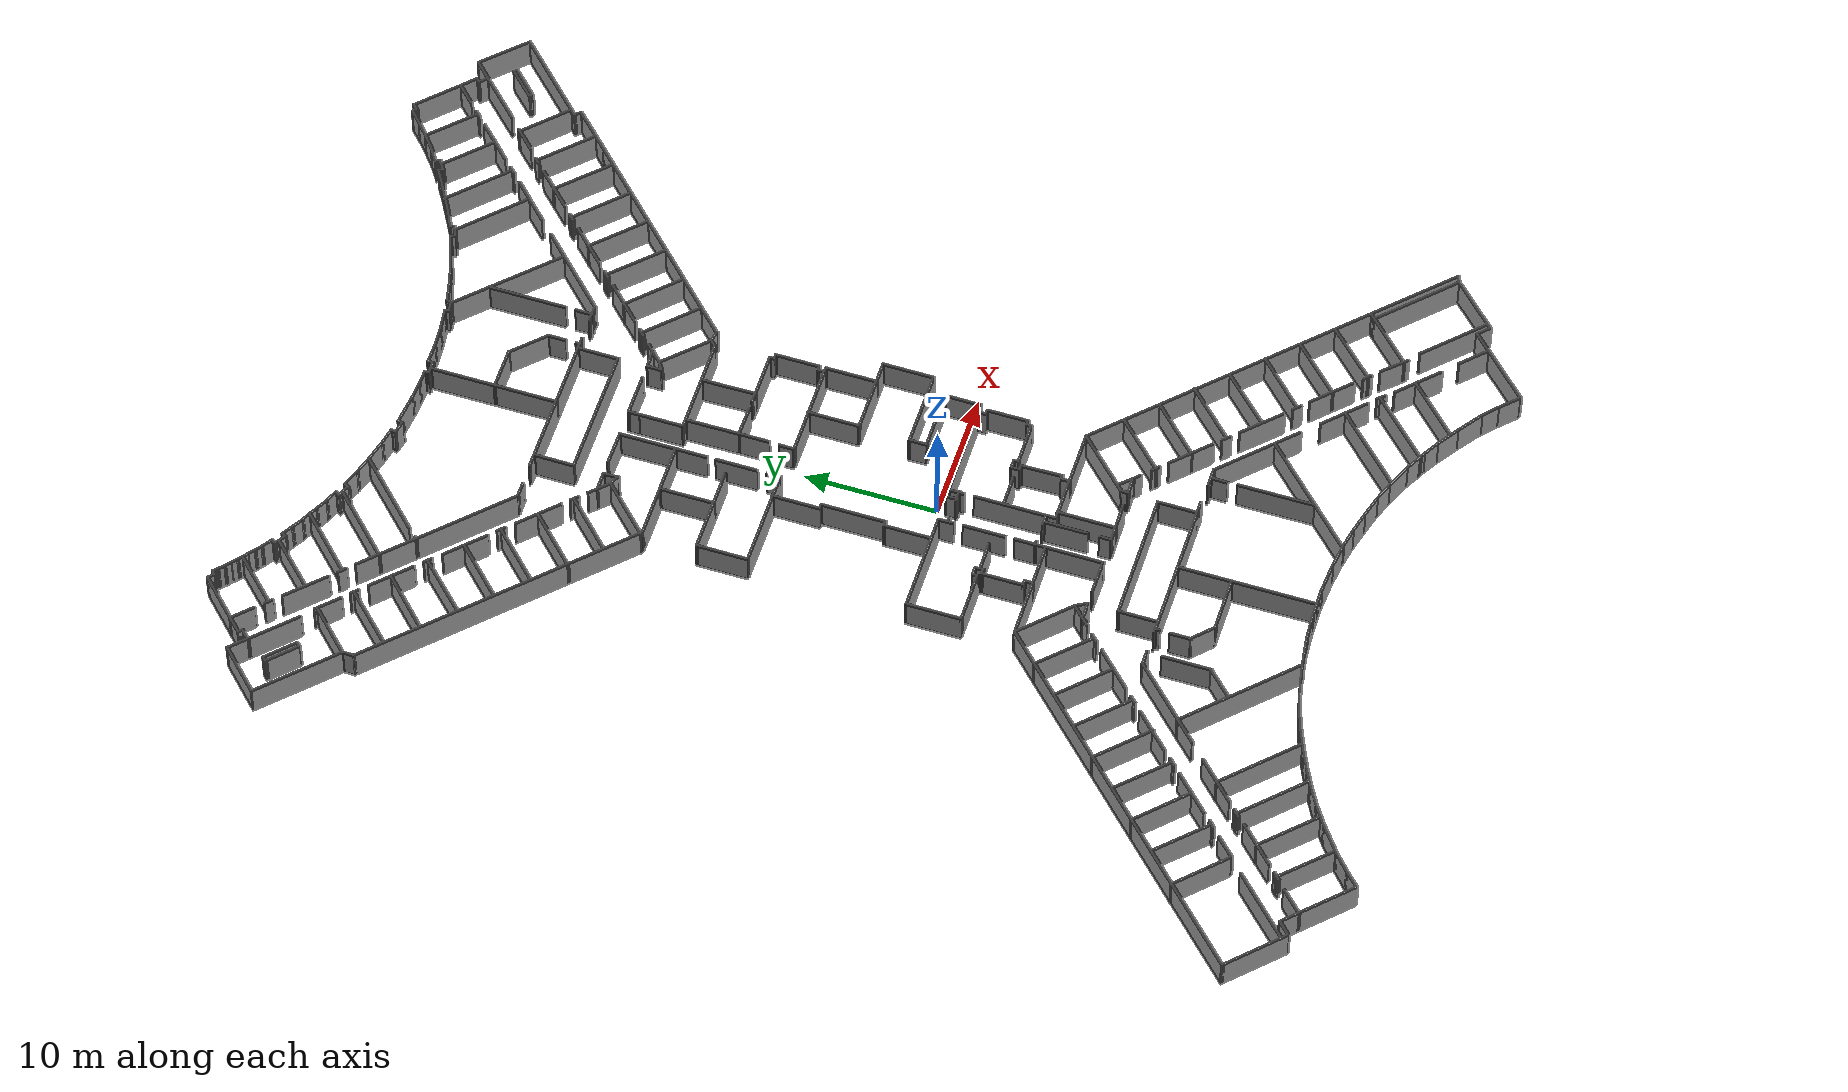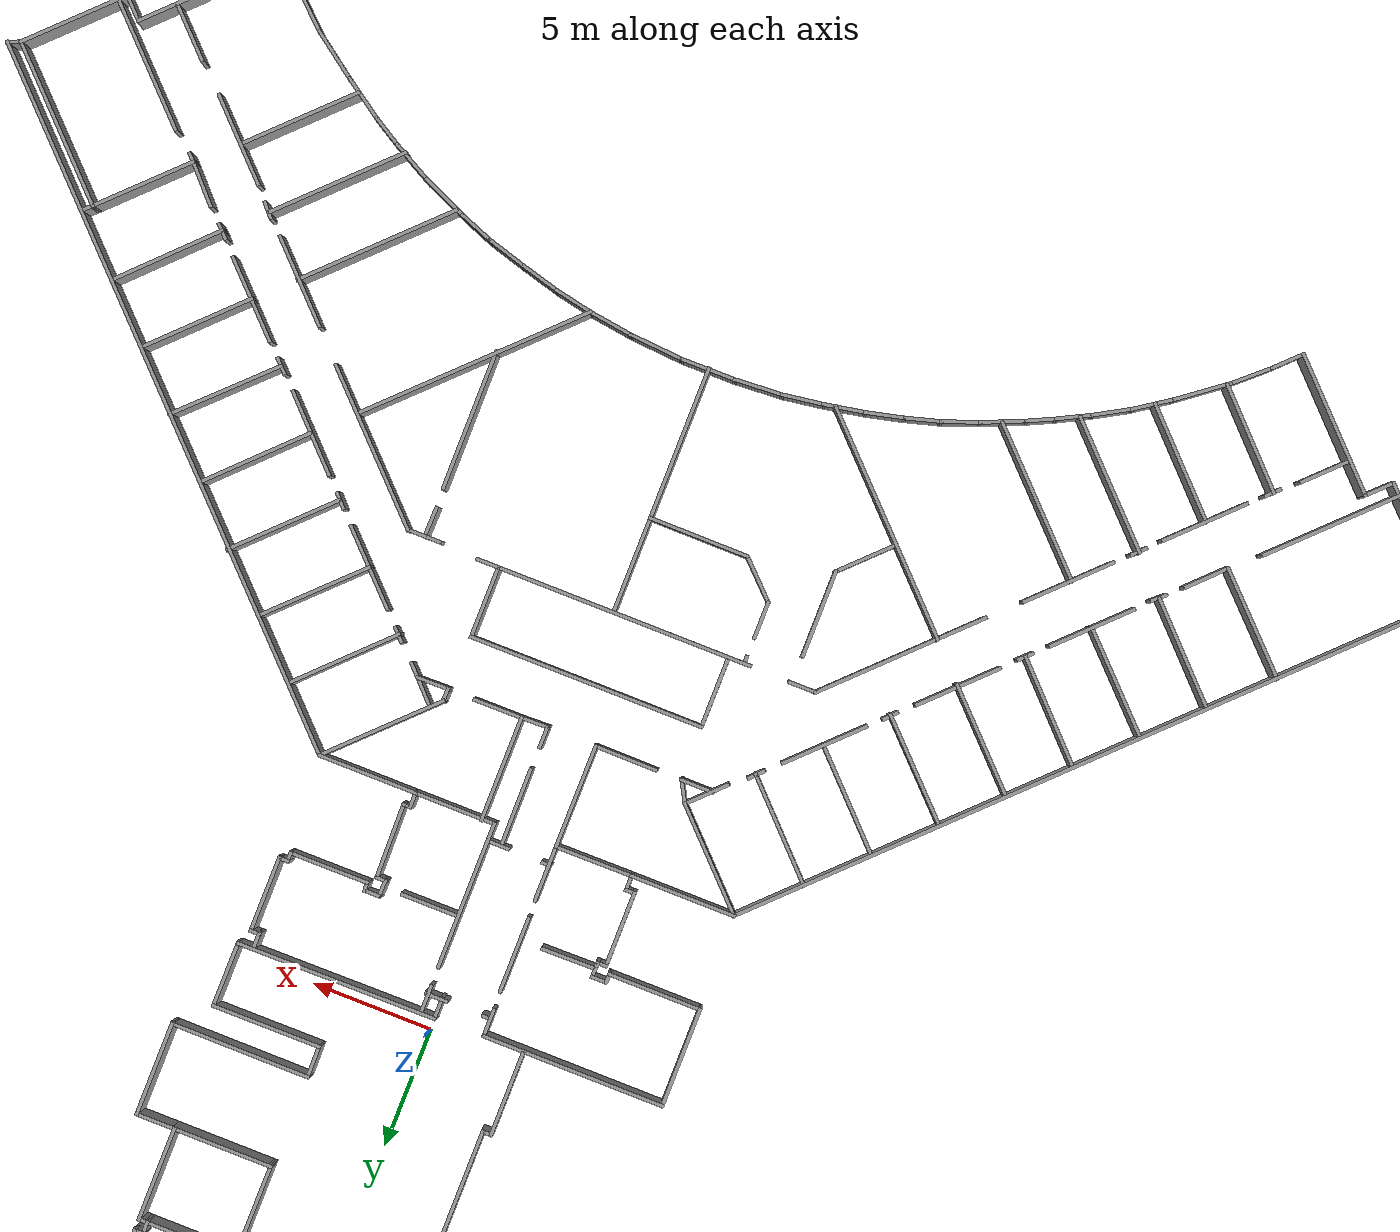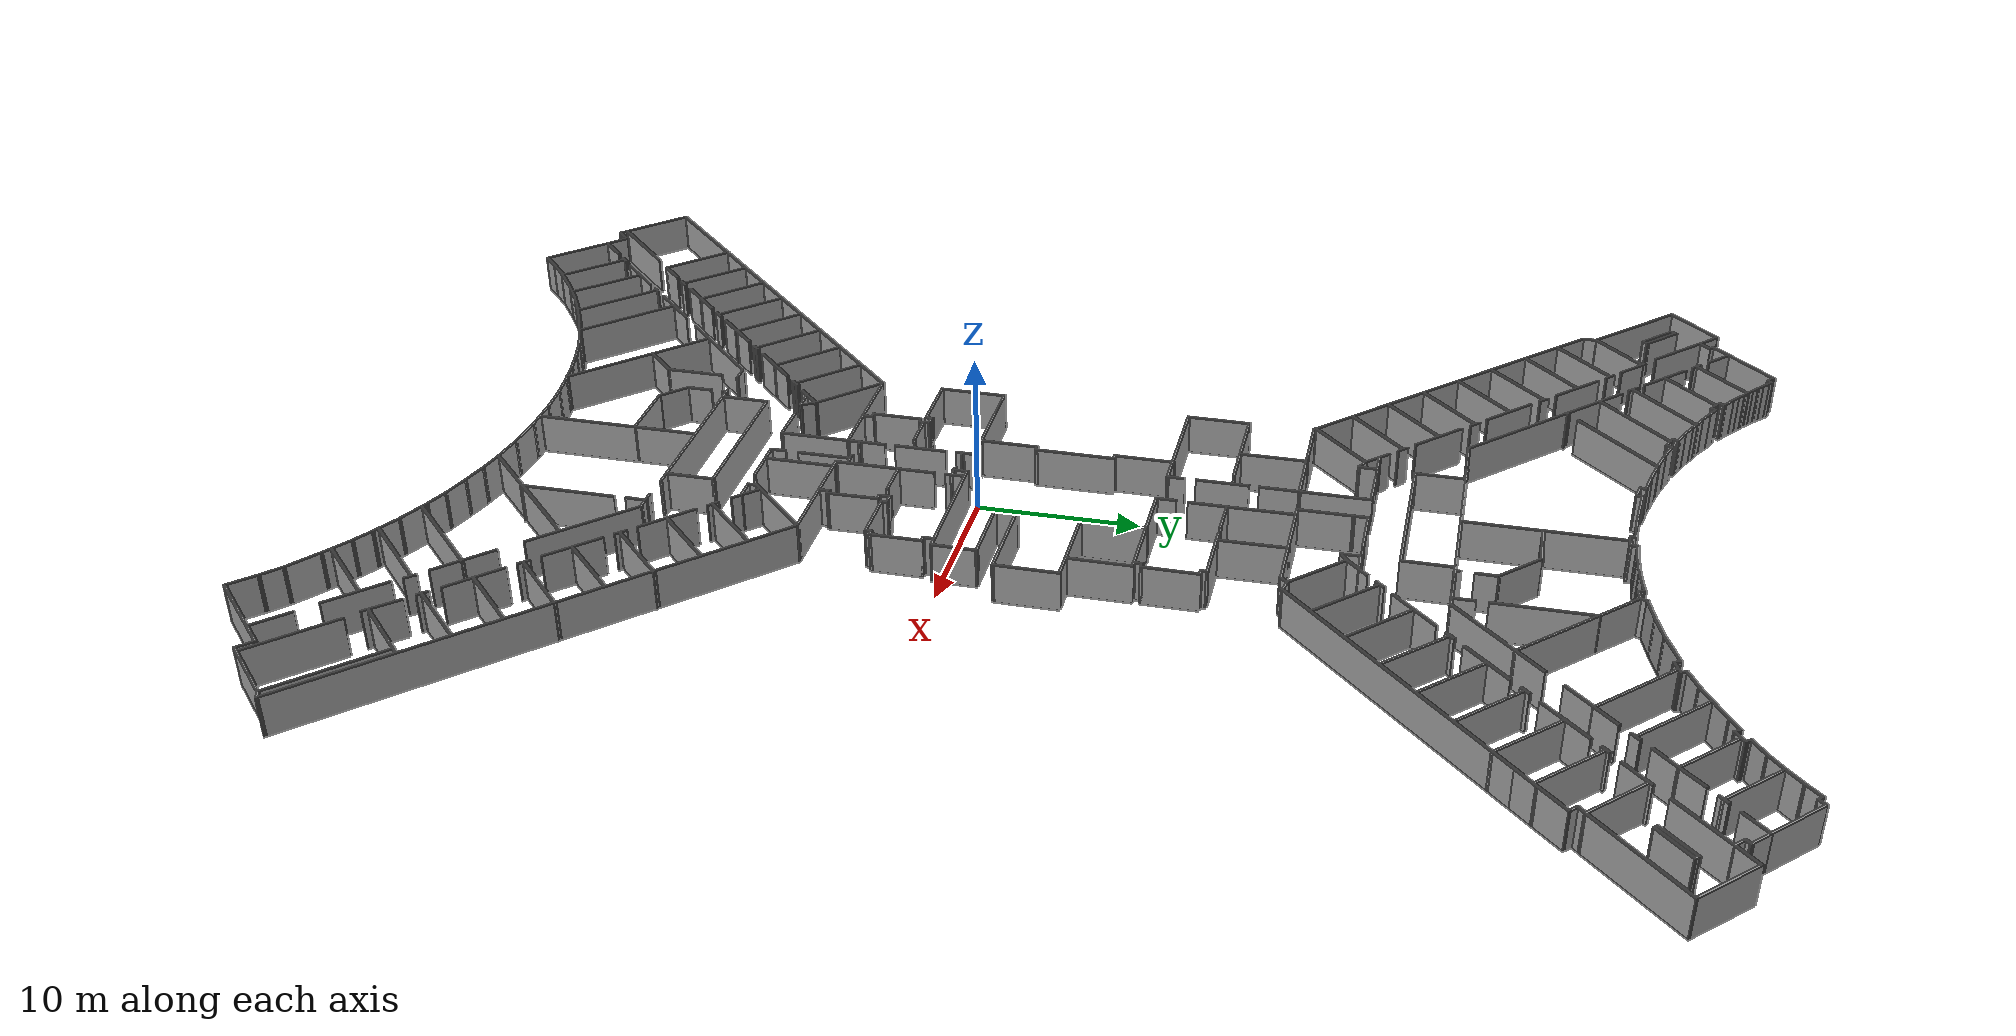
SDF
<?xml version='1.0'?>
<sdf version='1.7'>
  <model name='TI_1'>
    <pose>-0.810812 4.85868 0 0 -0 0</pose>
    <link name='Wall_100'>
      <collision name='Wall_100_Collision'>
        <geometry>
          <box>
            <size>1.75 0.15 2.5</size>
          </box>
        </geometry>
        <pose>0 0 1.25 0 -0 0</pose>
      </collision>
      <visual name='Wall_100_Visual'>
        <pose>0 0 1.25 0 -0 0</pose>
        <geometry>
          <box>
            <size>1.75 0.15 2.5</size>
          </box>
        </geometry>
        <material>
          <script>
            <uri>file://media/materials/scripts/gazebo.material</uri>
            <name>Gazebo/Grey</name>
          </script>
          <ambient>1 1 1 1</ambient>
        </material>
        <meta>
          <layer>0</layer>
        </meta>
      </visual>
      <pose>-8.06735 34.8632 0 0 -0 -0.261799</pose>
    </link>
    <link name='Wall_101'>
      <collision name='Wall_101_Collision'>
        <geometry>
          <box>
            <size>1.47097 0.15 2.5</size>
          </box>
        </geometry>
        <pose>0 0 1.25 0 -0 0</pose>
      </collision>
      <visual name='Wall_101_Visual'>
        <pose>0 0 1.25 0 -0 0</pose>
        <geometry>
          <box>
            <size>1.47097 0.15 2.5</size>
          </box>
        </geometry>
        <material>
          <script>
            <uri>file://media/materials/scripts/gazebo.material</uri>
            <name>Gazebo/Grey</name>
          </script>
          <ambient>1 1 1 1</ambient>
        </material>
        <meta>
          <layer>0</layer>
        </meta>
      </visual>
      <pose>-6.64996 34.5124 0 0 -0 -0.219449</pose>
    </link>
    <link name='Wall_102'>
      <collision name='Wall_102_Collision'>
        <geometry>
          <box>
            <size>0.491524 0.15 2.5</size>
          </box>
        </geometry>
        <pose>0 0 1.25 0 -0 0</pose>
      </collision>
      <visual name='Wall_102_Visual'>
        <pose>0 0 1.25 0 -0 0</pose>
        <geometry>
          <box>
            <size>0.491524 0.15 2.5</size>
          </box>
        </geometry>
        <material>
          <script>
            <uri>file://media/materials/scripts/gazebo.material</uri>
            <name>Gazebo/Grey</name>
          </script>
          <ambient>1 1 1 1</ambient>
        </material>
        <meta>
          <layer>0</layer>
        </meta>
      </visual>
      <pose>-6.04049 34.2015 0 0 -0 -1.77829</pose>
    </link>
    <link name='Wall_103'>
      <collision name='Wall_103_Collision'>
        <geometry>
          <box>
            <size>1.08869 0.15 2.5</size>
          </box>
        </geometry>
        <pose>0 0 1.25 0 -0 0</pose>
      </collision>
      <visual name='Wall_103_Visual'>
        <pose>0 0 1.25 0 -0 0</pose>
        <geometry>
          <box>
            <size>1.08869 0.15 2.5</size>
          </box>
        </geometry>
        <material>
          <script>
            <uri>file://media/materials/scripts/gazebo.material</uri>
            <name>Gazebo/Grey</name>
          </script>
          <ambient>1 1 1 1</ambient>
        </material>
        <meta>
          <layer>0</layer>
        </meta>
      </visual>
      <pose>-5.61835 33.9289 0 0 -0 -0.226799</pose>
    </link>
    <link name='Wall_104'>
      <collision name='Wall_104_Collision'>
        <geometry>
          <box>
            <size>0.495577 0.15 2.5</size>
          </box>
        </geometry>
        <pose>0 0 1.25 0 -0 0</pose>
      </collision>
      <visual name='Wall_104_Visual'>
        <pose>0 0 1.25 0 -0 0</pose>
        <geometry>
          <box>
            <size>0.495577 0.15 2.5</size>
          </box>
        </geometry>
        <material>
          <script>
            <uri>file://media/materials/scripts/gazebo.material</uri>
            <name>Gazebo/Grey</name>
          </script>
          <ambient>1 1 1 1</ambient>
        </material>
        <meta>
          <layer>0</layer>
        </meta>
      </visual>
      <pose>-5.11705 33.9904 0 0 -0 1.31347</pose>
    </link>
    <link name='Wall_105'>
      <collision name='Wall_105_Collision'>
        <geometry>
          <box>
            <size>2.43432 0.15 2.5</size>
          </box>
        </geometry>
        <pose>0 0 1.25 0 -0 0</pose>
      </collision>
      <visual name='Wall_105_Visual'>
        <pose>0 0 1.25 0 -0 0</pose>
        <geometry>
          <box>
            <size>2.43432 0.15 2.5</size>
          </box>
        </geometry>
        <material>
          <script>
            <uri>file://media/materials/scripts/gazebo.material</uri>
            <name>Gazebo/Grey</name>
          </script>
          <ambient>1 1 1 1</ambient>
        </material>
        <meta>
          <layer>0</layer>
        </meta>
      </visual>
      <pose>-3.93856 34.0256 0 0 -0 -0.115759</pose>
    </link>
    <link name='Wall_106'>
      <collision name='Wall_106_Collision'>
        <geometry>
          <box>
            <size>1.33177 0.15 2.5</size>
          </box>
        </geometry>
        <pose>0 0 1.25 0 -0 0</pose>
      </collision>
      <visual name='Wall_106_Visual'>
        <pose>0 0 1.25 0 -0 0</pose>
        <geometry>
          <box>
            <size>1.33177 0.15 2.5</size>
          </box>
        </geometry>
        <material>
          <script>
            <uri>file://media/materials/scripts/gazebo.material</uri>
            <name>Gazebo/Grey</name>
          </script>
          <ambient>1 1 1 1</ambient>
        </material>
        <meta>
          <layer>0</layer>
        </meta>
      </visual>
      <pose>-2.2148 33.8497 0 0 -0 -0.074489</pose>
    </link>
    <link name='Wall_107'>
      <collision name='Wall_107_Collision'>
        <geometry>
          <box>
            <size>1.32901 0.15 2.5</size>
          </box>
        </geometry>
        <pose>0 0 1.25 0 -0 0</pose>
      </collision>
      <visual name='Wall_107_Visual'>
        <pose>0 0 1.25 0 -0 0</pose>
        <geometry>
          <box>
            <size>1.32901 0.15 2.5</size>
          </box>
        </geometry>
        <material>
          <script>
            <uri>file://media/materials/scripts/gazebo.material</uri>
            <name>Gazebo/Grey</name>
          </script>
          <ambient>1 1 1 1</ambient>
        </material>
        <meta>
          <layer>0</layer>
        </meta>
      </visual>
      <pose>-1.03631 33.7881 0 0 -0 -0.029842</pose>
    </link>
    <link name='Wall_108'>
      <collision name='Wall_108_Collision'>
        <geometry>
          <box>
            <size>0.466609 0.15 2.5</size>
          </box>
        </geometry>
        <pose>0 0 1.25 0 -0 0</pose>
      </collision>
      <visual name='Wall_108_Visual'>
        <pose>0 0 1.25 0 -0 0</pose>
        <geometry>
          <box>
            <size>0.466609 0.15 2.5</size>
          </box>
        </geometry>
        <material>
          <script>
            <uri>file://media/materials/scripts/gazebo.material</uri>
            <name>Gazebo/Grey</name>
          </script>
          <ambient>1 1 1 1</ambient>
        </material>
        <meta>
          <layer>0</layer>
        </meta>
      </visual>
      <pose>-0.447067 33.6122 0 0 -0 -1.5708</pose>
    </link>
    <link name='Wall_109'>
      <collision name='Wall_109_Collision'>
        <geometry>
          <box>
            <size>0.589735 0.15 2.5</size>
          </box>
        </geometry>
        <pose>0 0 1.25 0 -0 0</pose>
      </collision>
      <visual name='Wall_109_Visual'>
        <pose>0 0 1.25 0 -0 0</pose>
        <geometry>
          <box>
            <size>0.589735 0.15 2.5</size>
          </box>
        </geometry>
        <material>
          <script>
            <uri>file://media/materials/scripts/gazebo.material</uri>
            <name>Gazebo/Grey</name>
          </script>
          <ambient>1 1 1 1</ambient>
        </material>
        <meta>
          <layer>0</layer>
        </meta>
      </visual>
      <pose>-0.2272 33.4539 0 0 -0 0</pose>
    </link>
    <link name='Wall_111'>
      <collision name='Wall_111_Collision'>
        <geometry>
          <box>
            <size>9.75 0.15 2.5</size>
          </box>
        </geometry>
        <pose>0 0 1.25 0 -0 0</pose>
      </collision>
      <visual name='Wall_111_Visual'>
        <pose>0 0 1.25 0 -0 0</pose>
        <geometry>
          <box>
            <size>9.75 0.15 2.5</size>
          </box>
        </geometry>
        <material>
          <script>
            <uri>file://media/materials/scripts/gazebo.material</uri>
            <name>Gazebo/Grey</name>
          </script>
          <ambient>1 1 1 1</ambient>
        </material>
        <meta>
          <layer>0</layer>
        </meta>
      </visual>
      <pose>-0.007333 28.6539 0 0 -0 -1.5708</pose>
    </link>
    <link name='Wall_112'>
      <collision name='Wall_112_Collision'>
        <geometry>
          <box>
            <size>6 0.15 2.5</size>
          </box>
        </geometry>
        <pose>0 0 1.25 0 -0 0</pose>
      </collision>
      <visual name='Wall_112_Visual'>
        <pose>0 0 1.25 0 -0 0</pose>
        <geometry>
          <box>
            <size>6 0.15 2.5</size>
          </box>
        </geometry>
        <material>
          <script>
            <uri>file://media/materials/scripts/gazebo.material</uri>
            <name>Gazebo/Grey</name>
          </script>
          <ambient>1 1 1 1</ambient>
        </material>
        <meta>
          <layer>0</layer>
        </meta>
      </visual>
      <pose>-2.93233 23.8539 0 0 -0 3.14159</pose>
    </link>
    <link name='Wall_114'>
      <collision name='Wall_114_Collision'>
        <geometry>
          <box>
            <size>6 0.15 2.5</size>
          </box>
        </geometry>
        <pose>0 0 1.25 0 -0 0</pose>
      </collision>
      <visual name='Wall_114_Visual'>
        <pose>0 0 1.25 0 -0 0</pose>
        <geometry>
          <box>
            <size>6 0.15 2.5</size>
          </box>
        </geometry>
        <material>
          <script>
            <uri>file://media/materials/scripts/gazebo.material</uri>
            <name>Gazebo/Grey</name>
          </script>
          <ambient>1 1 1 1</ambient>
        </material>
        <meta>
          <layer>0</layer>
        </meta>
      </visual>
      <pose>2.91767 23.8539 0 0 -0 0</pose>
    </link>
    <link name='Wall_116'>
      <collision name='Wall_116_Collision'>
        <geometry>
          <box>
            <size>0.440225 0.15 2.5</size>
          </box>
        </geometry>
        <pose>0 0 1.25 0 -0 0</pose>
      </collision>
      <visual name='Wall_116_Visual'>
        <pose>0 0 1.25 0 -0 0</pose>
        <geometry>
          <box>
            <size>0.440225 0.15 2.5</size>
          </box>
        </geometry>
        <material>
          <script>
            <uri>file://media/materials/scripts/gazebo.material</uri>
            <name>Gazebo/Grey</name>
          </script>
          <ambient>1 1 1 1</ambient>
        </material>
        <meta>
          <layer>0</layer>
        </meta>
      </visual>
      <pose>5.32121 23.9754 0 0 -0 -1.5708</pose>
    </link>
    <link name='Wall_118'>
      <collision name='Wall_118_Collision'>
        <geometry>
          <box>
            <size>3.149 0.15 2.5</size>
          </box>
        </geometry>
        <pose>0 0 1.25 0 -0 0</pose>
      </collision>
      <visual name='Wall_118_Visual'>
        <pose>0 0 1.25 0 -0 0</pose>
        <geometry>
          <box>
            <size>3.149 0.15 2.5</size>
          </box>
        </geometry>
        <material>
          <script>
            <uri>file://media/materials/scripts/gazebo.material</uri>
            <name>Gazebo/Grey</name>
          </script>
          <ambient>1 1 1 1</ambient>
        </material>
        <meta>
          <layer>0</layer>
        </meta>
      </visual>
      <pose>4.94604 22.297 0 0 -0 -1.57373</pose>
    </link>
    <link name='Wall_119'>
      <collision name='Wall_119_Collision'>
        <geometry>
          <box>
            <size>9.93855 0.15 2.5</size>
          </box>
        </geometry>
        <pose>0 0 1.25 0 -0 0</pose>
      </collision>
      <visual name='Wall_119_Visual'>
        <pose>0 0 1.25 0 -0 0</pose>
        <geometry>
          <box>
            <size>9.93855 0.15 2.5</size>
          </box>
        </geometry>
        <material>
          <script>
            <uri>file://media/materials/scripts/gazebo.material</uri>
            <name>Gazebo/Grey</name>
          </script>
          <ambient>1 1 1 1</ambient>
        </material>
        <meta>
          <layer>0</layer>
        </meta>
      </visual>
      <pose>0.013612 20.8144 0 0 -0 3.13814</pose>
    </link>
    <link name='Wall_120'>
      <collision name='Wall_120_Collision'>
        <geometry>
          <box>
            <size>3.1578 0.15 2.5</size>
          </box>
        </geometry>
        <pose>0 0 1.25 0 -0 0</pose>
      </collision>
      <visual name='Wall_120_Visual'>
        <pose>0 0 1.25 0 -0 0</pose>
        <geometry>
          <box>
            <size>3.1578 0.15 2.5</size>
          </box>
        </geometry>
        <material>
          <script>
            <uri>file://media/materials/scripts/gazebo.material</uri>
            <name>Gazebo/Grey</name>
          </script>
          <ambient>1 1 1 1</ambient>
        </material>
        <meta>
          <layer>0</layer>
        </meta>
      </visual>
      <pose>-4.87624 22.3352 0 0 -0 1.56787</pose>
    </link>
    <link name='Wall_122'>
      <collision name='Wall_122_Collision'>
        <geometry>
          <box>
            <size>0.648628 0.15 2.5</size>
          </box>
        </geometry>
        <pose>0 0 1.25 0 -0 0</pose>
      </collision>
      <visual name='Wall_122_Visual'>
        <pose>0 0 1.25 0 -0 0</pose>
        <geometry>
          <box>
            <size>0.648628 0.15 2.5</size>
          </box>
        </geometry>
        <material>
          <script>
            <uri>file://media/materials/scripts/gazebo.material</uri>
            <name>Gazebo/Grey</name>
          </script>
          <ambient>1 1 1 1</ambient>
        </material>
        <meta>
          <layer>0</layer>
        </meta>
      </visual>
      <pose>0.24162 33.4557 0 0 -0 0.00691</pose>
    </link>
    <link name='Wall_123'>
      <collision name='Wall_123_Collision'>
        <geometry>
          <box>
            <size>0.547699 0.15 2.5</size>
          </box>
        </geometry>
        <pose>0 0 1.25 0 -0 0</pose>
      </collision>
      <visual name='Wall_123_Visual'>
        <pose>0 0 1.25 0 -0 0</pose>
        <geometry>
          <box>
            <size>0.547699 0.15 2.5</size>
          </box>
        </geometry>
        <material>
          <script>
            <uri>file://media/materials/scripts/gazebo.material</uri>
            <name>Gazebo/Grey</name>
          </script>
          <ambient>1 1 1 1</ambient>
        </material>
        <meta>
          <layer>0</layer>
        </meta>
      </visual>
      <pose>0.490572 33.6562 0 0 -0 1.5708</pose>
    </link>
    <link name='Wall_124'>
      <collision name='Wall_124_Collision'>
        <geometry>
          <box>
            <size>1.60043 0.15 2.5</size>
          </box>
        </geometry>
        <pose>0 0 1.25 0 -0 0</pose>
      </collision>
      <visual name='Wall_124_Visual'>
        <pose>0 0 1.25 0 -0 0</pose>
        <geometry>
          <box>
            <size>1.60043 0.15 2.5</size>
          </box>
        </geometry>
        <material>
          <script>
            <uri>file://media/materials/scripts/gazebo.material</uri>
            <name>Gazebo/Grey</name>
          </script>
          <ambient>1 1 1 1</ambient>
        </material>
        <meta>
          <layer>0</layer>
        </meta>
      </visual>
      <pose>1.21579 33.8551 0 0 -0 0</pose>
    </link>
    <link name='Wall_125'>
      <collision name='Wall_125_Collision'>
        <geometry>
          <box>
            <size>1.5801 0.15 2.5</size>
          </box>
        </geometry>
        <pose>0 0 1.25 0 -0 0</pose>
      </collision>
      <visual name='Wall_125_Visual'>
        <pose>0 0 1.25 0 -0 0</pose>
        <geometry>
          <box>
            <size>1.5801 0.15 2.5</size>
          </box>
        </geometry>
        <material>
          <script>
            <uri>file://media/materials/scripts/gazebo.material</uri>
            <name>Gazebo/Grey</name>
          </script>
          <ambient>1 1 1 1</ambient>
        </material>
        <meta>
          <layer>0</layer>
        </meta>
      </visual>
      <pose>2.65452 33.9019 0 0 -0 0.06548</pose>
    </link>
    <link name='Wall_126'>
      <collision name='Wall_126_Collision'>
        <geometry>
          <box>
            <size>1.61246 0.15 2.5</size>
          </box>
        </geometry>
        <pose>0 0 1.25 0 -0 0</pose>
      </collision>
      <visual name='Wall_126_Visual'>
        <pose>0 0 1.25 0 -0 0</pose>
        <geometry>
          <box>
            <size>1.61246 0.15 2.5</size>
          </box>
        </geometry>
        <material>
          <script>
            <uri>file://media/materials/scripts/gazebo.material</uri>
            <name>Gazebo/Grey</name>
          </script>
          <ambient>1 1 1 1</ambient>
        </material>
        <meta>
          <layer>0</layer>
        </meta>
      </visual>
      <pose>4.09326 34.0422 0 0 -0 0.128323</pose>
    </link>
    <link name='Wall_127'>
      <collision name='Wall_127_Collision'>
        <geometry>
          <box>
            <size>0.462116 0.15 2.5</size>
          </box>
        </geometry>
        <pose>0 0 1.25 0 -0 0</pose>
      </collision>
      <visual name='Wall_127_Visual'>
        <pose>0 0 1.25 0 -0 0</pose>
        <geometry>
          <box>
            <size>0.462116 0.15 2.5</size>
          </box>
        </geometry>
        <material>
          <script>
            <uri>file://media/materials/scripts/gazebo.material</uri>
            <name>Gazebo/Grey</name>
          </script>
          <ambient>1 1 1 1</ambient>
        </material>
        <meta>
          <layer>0</layer>
        </meta>
      </visual>
      <pose>4.97053 34.1709 0 0 -0 0.226799</pose>
    </link>
    <link name='Wall_128'>
      <collision name='Wall_128_Collision'>
        <geometry>
          <box>
            <size>0.50786 0.15 2.5</size>
          </box>
        </geometry>
        <pose>0 0 1.25 0 -0 0</pose>
      </collision>
      <visual name='Wall_128_Visual'>
        <pose>0 0 1.25 0 -0 0</pose>
        <geometry>
          <box>
            <size>0.50786 0.15 2.5</size>
          </box>
        </geometry>
        <material>
          <script>
            <uri>file://media/materials/scripts/gazebo.material</uri>
            <name>Gazebo/Grey</name>
          </script>
          <ambient>1 1 1 1</ambient>
        </material>
        <meta>
          <layer>0</layer>
        </meta>
      </visual>
      <pose>5.15769 34.0305 0 0 -0 -1.3734</pose>
    </link>
    <link name='Wall_129'>
      <collision name='Wall_129_Collision'>
        <geometry>
          <box>
            <size>0.884588 0.15 2.5</size>
          </box>
        </geometry>
        <pose>0 0 1.25 0 -0 0</pose>
      </collision>
      <visual name='Wall_129_Visual'>
        <pose>0 0 1.25 0 -0 0</pose>
        <geometry>
          <box>
            <size>0.884588 0.15 2.5</size>
          </box>
        </geometry>
        <material>
          <script>
            <uri>file://media/materials/scripts/gazebo.material</uri>
            <name>Gazebo/Grey</name>
          </script>
          <ambient>1 1 1 1</ambient>
        </material>
        <meta>
          <layer>0</layer>
        </meta>
      </visual>
      <pose>5.55539 33.9136 0 0 -0 0.159913</pose>
    </link>
    <link name='Wall_130'>
      <collision name='Wall_130_Collision'>
        <geometry>
          <box>
            <size>9.31438 0.15 2.5</size>
          </box>
        </geometry>
        <pose>0 0 1.25 0 -0 0</pose>
      </collision>
      <visual name='Wall_130_Visual'>
        <pose>0 0 1.25 0 -0 0</pose>
        <geometry>
          <box>
            <size>9.31438 0.15 2.5</size>
          </box>
        </geometry>
        <material>
          <script>
            <uri>file://media/materials/scripts/gazebo.material</uri>
            <name>Gazebo/Grey</name>
          </script>
          <ambient>1 1 1 1</ambient>
        </material>
        <meta>
          <layer>0</layer>
        </meta>
      </visual>
      <pose>9.14637 30.7203 0 0 -0 -0.789008</pose>
    </link>
    <link name='Wall_131'>
      <collision name='Wall_131_Collision'>
        <geometry>
          <box>
            <size>2.36664 0.15 2.5</size>
          </box>
        </geometry>
        <pose>0 0 1.25 0 -0 0</pose>
      </collision>
      <visual name='Wall_131_Visual'>
        <pose>0 0 1.25 0 -0 0</pose>
        <geometry>
          <box>
            <size>2.36664 0.15 2.5</size>
          </box>
        </geometry>
        <material>
          <script>
            <uri>file://media/materials/scripts/gazebo.material</uri>
            <name>Gazebo/Grey</name>
          </script>
          <ambient>1 1 1 1</ambient>
        </material>
        <meta>
          <layer>0</layer>
        </meta>
      </visual>
      <pose>13.1585 28.2522 0 0 -0 0.785398</pose>
    </link>
    <link name='Wall_133'>
      <collision name='Wall_133_Collision'>
        <geometry>
          <box>
            <size>6 0.15 2.5</size>
          </box>
        </geometry>
        <pose>0 0 1.25 0 -0 0</pose>
      </collision>
      <visual name='Wall_133_Visual'>
        <pose>0 0 1.25 0 -0 0</pose>
        <geometry>
          <box>
            <size>6 0.15 2.5</size>
          </box>
        </geometry>
        <material>
          <script>
            <uri>file://media/materials/scripts/gazebo.material</uri>
            <name>Gazebo/Grey</name>
          </script>
          <ambient>1 1 1 1</ambient>
        </material>
        <meta>
          <layer>0</layer>
        </meta>
      </visual>
      <pose>8.09324 28.8599 0 0 -0 -1.5708</pose>
    </link>
    <link name='Wall_135'>
      <collision name='Wall_135_Collision'>
        <geometry>
          <box>
            <size>3.25 0.15 2.5</size>
          </box>
        </geometry>
        <pose>0 0 1.25 0 -0 0</pose>
      </collision>
      <visual name='Wall_135_Visual'>
        <pose>0 0 1.25 0 -0 0</pose>
        <geometry>
          <box>
            <size>3.25 0.15 2.5</size>
          </box>
        </geometry>
        <material>
          <script>
            <uri>file://media/materials/scripts/gazebo.material</uri>
            <name>Gazebo/Grey</name>
          </script>
          <ambient>1 1 1 1</ambient>
        </material>
        <meta>
          <layer>0</layer>
        </meta>
      </visual>
      <pose>1.52652 28.5504 0 0 -0 0</pose>
    </link>
    <link name='Wall_137'>
      <collision name='Wall_137_Collision'>
        <geometry>
          <box>
            <size>3.36136 0.15 2.5</size>
          </box>
        </geometry>
        <pose>0 0 1.25 0 -0 0</pose>
      </collision>
      <visual name='Wall_137_Visual'>
        <pose>0 0 1.25 0 -0 0</pose>
        <geometry>
          <box>
            <size>3.36136 0.15 2.5</size>
          </box>
        </geometry>
        <material>
          <script>
            <uri>file://media/materials/scripts/gazebo.material</uri>
            <name>Gazebo/Grey</name>
          </script>
          <ambient>1 1 1 1</ambient>
        </material>
        <meta>
          <layer>0</layer>
        </meta>
      </visual>
      <pose>4.20693 27.4101 0 0 -0 -0.789774</pose>
    </link>
    <link name='Wall_139'>
      <collision name='Wall_139_Collision'>
        <geometry>
          <box>
            <size>1.42714 0.15 2.5</size>
          </box>
        </geometry>
        <pose>0 0 1.25 0 -0 0</pose>
      </collision>
      <visual name='Wall_139_Visual'>
        <pose>0 0 1.25 0 -0 0</pose>
        <geometry>
          <box>
            <size>1.42714 0.15 2.5</size>
          </box>
        </geometry>
        <material>
          <script>
            <uri>file://media/materials/scripts/gazebo.material</uri>
            <name>Gazebo/Grey</name>
          </script>
          <ambient>1 1 1 1</ambient>
        </material>
        <meta>
          <layer>0</layer>
        </meta>
      </visual>
      <pose>5.33734 25.6312 0 0 -0 -1.5708</pose>
    </link>
    <link name='Wall_141'>
      <collision name='Wall_141_Collision'>
        <geometry>
          <box>
            <size>5.25 0.15 2.5</size>
          </box>
        </geometry>
        <pose>0 0 1.25 0 -0 0</pose>
      </collision>
      <visual name='Wall_141_Visual'>
        <pose>0 0 1.25 0 -0 0</pose>
        <geometry>
          <box>
            <size>5.25 0.15 2.5</size>
          </box>
        </geometry>
        <material>
          <script>
            <uri>file://media/materials/scripts/gazebo.material</uri>
            <name>Gazebo/Grey</name>
          </script>
          <ambient>1 1 1 1</ambient>
        </material>
        <meta>
          <layer>0</layer>
        </meta>
      </visual>
      <pose>10.5716 25.6654 0 0 -0 -2.35619</pose>
    </link>
    <link name='Wall_142'>
      <collision name='Wall_142_Collision'>
        <geometry>
          <box>
            <size>1.38634 0.15 2.5</size>
          </box>
        </geometry>
        <pose>0 0 1.25 0 -0 0</pose>
      </collision>
      <visual name='Wall_142_Visual'>
        <pose>0 0 1.25 0 -0 0</pose>
        <geometry>
          <box>
            <size>1.38634 0.15 2.5</size>
          </box>
        </geometry>
        <material>
          <script>
            <uri>file://media/materials/scripts/gazebo.material</uri>
            <name>Gazebo/Grey</name>
          </script>
          <ambient>1 1 1 1</ambient>
        </material>
        <meta>
          <layer>0</layer>
        </meta>
      </visual>
      <pose>8.15035 23.8615 0 0 -0 -3.14039</pose>
    </link>
    <link name='Wall_144'>
      <collision name='Wall_144_Collision'>
        <geometry>
          <box>
            <size>1.41185 0.15 2.5</size>
          </box>
        </geometry>
        <pose>0 0 1.25 0 -0 0</pose>
      </collision>
      <visual name='Wall_144_Visual'>
        <pose>0 0 1.25 0 -0 0</pose>
        <geometry>
          <box>
            <size>1.41185 0.15 2.5</size>
          </box>
        </geometry>
        <material>
          <script>
            <uri>file://media/materials/scripts/gazebo.material</uri>
            <name>Gazebo/Grey</name>
          </script>
          <ambient>1 1 1 1</ambient>
        </material>
        <meta>
          <layer>0</layer>
        </meta>
      </visual>
      <pose>8.09428 24.4611 0 0 -0 -1.56474</pose>
    </link>
    <link name='Wall_146'>
      <collision name='Wall_146_Collision'>
        <geometry>
          <box>
            <size>0.53295 0.15 2.5</size>
          </box>
        </geometry>
        <pose>0 0 1.25 0 -0 0</pose>
      </collision>
      <visual name='Wall_146_Visual'>
        <pose>0 0 1.25 0 -0 0</pose>
        <geometry>
          <box>
            <size>0.53295 0.15 2.5</size>
          </box>
        </geometry>
        <material>
          <script>
            <uri>file://media/materials/scripts/gazebo.material</uri>
            <name>Gazebo/Grey</name>
          </script>
          <ambient>1 1 1 1</ambient>
        </material>
        <meta>
          <layer>0</layer>
        </meta>
      </visual>
      <pose>5.98507 34.1514 0 0 -0 1.21287</pose>
    </link>
    <link name='Wall_147'>
      <collision name='Wall_147_Collision'>
        <geometry>
          <box>
            <size>1.9322 0.15 2.5</size>
          </box>
        </geometry>
        <pose>0 0 1.25 0 -0 0</pose>
      </collision>
      <visual name='Wall_147_Visual'>
        <pose>0 0 1.25 0 -0 0</pose>
        <geometry>
          <box>
            <size>1.9322 0.15 2.5</size>
          </box>
        </geometry>
        <material>
          <script>
            <uri>file://media/materials/scripts/gazebo.material</uri>
            <name>Gazebo/Grey</name>
          </script>
          <ambient>1 1 1 1</ambient>
        </material>
        <meta>
          <layer>0</layer>
        </meta>
      </visual>
      <pose>6.91843 34.5396 0 0 -0 0.236558</pose>
    </link>
    <link name='Wall_148'>
      <collision name='Wall_148_Collision'>
        <geometry>
          <box>
            <size>1.80955 0.15 2.5</size>
          </box>
        </geometry>
        <pose>0 0 1.25 0 -0 0</pose>
      </collision>
      <visual name='Wall_148_Visual'>
        <pose>0 0 1.25 0 -0 0</pose>
        <geometry>
          <box>
            <size>1.80955 0.15 2.5</size>
          </box>
        </geometry>
        <material>
          <script>
            <uri>file://media/materials/scripts/gazebo.material</uri>
            <name>Gazebo/Grey</name>
          </script>
          <ambient>1 1 1 1</ambient>
        </material>
        <meta>
          <layer>0</layer>
        </meta>
      </visual>
      <pose>8.58139 34.9804 0 0 -0 0.283421</pose>
    </link>
    <link name='Wall_149'>
      <collision name='Wall_149_Collision'>
        <geometry>
          <box>
            <size>2.41138 0.15 2.5</size>
          </box>
        </geometry>
        <pose>0 0 1.25 0 -0 0</pose>
      </collision>
      <visual name='Wall_149_Visual'>
        <pose>0 0 1.25 0 -0 0</pose>
        <geometry>
          <box>
            <size>2.41138 0.15 2.5</size>
          </box>
        </geometry>
        <material>
          <script>
            <uri>file://media/materials/scripts/gazebo.material</uri>
            <name>Gazebo/Grey</name>
          </script>
          <ambient>1 1 1 1</ambient>
        </material>
        <meta>
          <layer>0</layer>
        </meta>
      </visual>
      <pose>10.4377 35.607 0 0 -0 0.356369</pose>
    </link>
    <link name='Wall_150'>
      <collision name='Wall_150_Collision'>
        <geometry>
          <box>
            <size>0.517701 0.15 2.5</size>
          </box>
        </geometry>
        <pose>0 0 1.25 0 -0 0</pose>
      </collision>
      <visual name='Wall_150_Visual'>
        <pose>0 0 1.25 0 -0 0</pose>
        <geometry>
          <box>
            <size>0.517701 0.15 2.5</size>
          </box>
        </geometry>
        <material>
          <script>
            <uri>file://media/materials/scripts/gazebo.material</uri>
            <name>Gazebo/Grey</name>
          </script>
          <ambient>1 1 1 1</ambient>
        </material>
        <meta>
          <layer>0</layer>
        </meta>
      </visual>
      <pose>11.567 35.8313 0 0 -0 -1.18248</pose>
    </link>
    <link name='Wall_151'>
      <collision name='Wall_151_Collision'>
        <geometry>
          <box>
            <size>0.747524 0.15 2.5</size>
          </box>
        </geometry>
        <pose>0 0 1.25 0 -0 0</pose>
      </collision>
      <visual name='Wall_151_Visual'>
        <pose>0 0 1.25 0 -0 0</pose>
        <geometry>
          <box>
            <size>0.747524 0.15 2.5</size>
          </box>
        </geometry>
        <material>
          <script>
            <uri>file://media/materials/scripts/gazebo.material</uri>
            <name>Gazebo/Grey</name>
          </script>
          <ambient>1 1 1 1</ambient>
        </material>
        <meta>
          <layer>0</layer>
        </meta>
      </visual>
      <pose>11.915 35.7694 0 0 -0 0.370891</pose>
    </link>
    <link name='Wall_152'>
      <collision name='Wall_152_Collision'>
        <geometry>
          <box>
            <size>0.45471 0.15 2.5</size>
          </box>
        </geometry>
        <pose>0 0 1.25 0 -0 0</pose>
      </collision>
      <visual name='Wall_152_Visual'>
        <pose>0 0 1.25 0 -0 0</pose>
        <geometry>
          <box>
            <size>0.45471 0.15 2.5</size>
          </box>
        </geometry>
        <material>
          <script>
            <uri>file://media/materials/scripts/gazebo.material</uri>
            <name>Gazebo/Grey</name>
          </script>
          <ambient>1 1 1 1</ambient>
        </material>
        <meta>
          <layer>0</layer>
        </meta>
      </visual>
      <pose>12.3327 35.9395 0 0 -0 0.418224</pose>
    </link>
    <link name='Wall_153'>
      <collision name='Wall_153_Collision'>
        <geometry>
          <box>
            <size>0.46323 0.15 2.5</size>
          </box>
        </geometry>
        <pose>0 0 1.25 0 -0 0</pose>
      </collision>
      <visual name='Wall_153_Visual'>
        <pose>0 0 1.25 0 -0 0</pose>
        <geometry>
          <box>
            <size>0.46323 0.15 2.5</size>
          </box>
        </geometry>
        <material>
          <script>
            <uri>file://media/materials/scripts/gazebo.material</uri>
            <name>Gazebo/Grey</name>
          </script>
          <ambient>1 1 1 1</ambient>
        </material>
        <meta>
          <layer>0</layer>
        </meta>
      </visual>
      <pose>12.4178 36.1484 0 0 -0 1.92379</pose>
    </link>
    <link name='Wall_154'>
      <collision name='Wall_154_Collision'>
        <geometry>
          <box>
            <size>1.52006 0.15 2.5</size>
          </box>
        </geometry>
        <pose>0 0 1.25 0 -0 0</pose>
      </collision>
      <visual name='Wall_154_Visual'>
        <pose>0 0 1.25 0 -0 0</pose>
        <geometry>
          <box>
            <size>1.52006 0.15 2.5</size>
          </box>
        </geometry>
        <material>
          <script>
            <uri>file://media/materials/scripts/gazebo.material</uri>
            <name>Gazebo/Grey</name>
          </script>
          <ambient>1 1 1 1</ambient>
        </material>
        <meta>
          <layer>0</layer>
        </meta>
      </visual>
      <pose>12.9824 36.5893 0 0 -0 0.443448</pose>
    </link>
    <link name='Wall_155'>
      <collision name='Wall_155_Collision'>
        <geometry>
          <box>
            <size>1.39718 0.15 2.5</size>
          </box>
        </geometry>
        <pose>0 0 1.25 0 -0 0</pose>
      </collision>
      <visual name='Wall_155_Visual'>
        <pose>0 0 1.25 0 -0 0</pose>
        <geometry>
          <box>
            <size>1.39718 0.15 2.5</size>
          </box>
        </geometry>
        <material>
          <script>
            <uri>file://media/materials/scripts/gazebo.material</uri>
            <name>Gazebo/Grey</name>
          </script>
          <ambient>1 1 1 1</ambient>
        </material>
        <meta>
          <layer>0</layer>
        </meta>
      </visual>
      <pose>14.1426 37.1926 0 0 -0 0.519146</pose>
    </link>
    <link name='Wall_156'>
      <collision name='Wall_156_Collision'>
        <geometry>
          <box>
            <size>5.59232 0.15 2.5</size>
          </box>
        </geometry>
        <pose>0 0 1.25 0 -0 0</pose>
      </collision>
      <visual name='Wall_156_Visual'>
        <pose>0 0 1.25 0 -0 0</pose>
        <geometry>
          <box>
            <size>5.59232 0.15 2.5</size>
          </box>
        </geometry>
        <material>
          <script>
            <uri>file://media/materials/scripts/gazebo.material</uri>
            <name>Gazebo/Grey</name>
          </script>
          <ambient>1 1 1 1</ambient>
        </material>
        <meta>
          <layer>0</layer>
        </meta>
      </visual>
      <pose>16.611 35.5807 0 0 -0 -0.783911</pose>
    </link>
    <link name='Wall_158'>
      <collision name='Wall_158_Collision'>
        <geometry>
          <box>
            <size>1.75023 0.15 2.5</size>
          </box>
        </geometry>
        <pose>0 0 1.25 0 -0 0</pose>
      </collision>
      <visual name='Wall_158_Visual'>
        <pose>0 0 1.25 0 -0 0</pose>
        <geometry>
          <box>
            <size>1.75023 0.15 2.5</size>
          </box>
        </geometry>
        <material>
          <script>
            <uri>file://media/materials/scripts/gazebo.material</uri>
            <name>Gazebo/Grey</name>
          </script>
          <ambient>1 1 1 1</ambient>
        </material>
        <meta>
          <layer>0</layer>
        </meta>
      </visual>
      <pose>15.3802 37.8964 0 0 -0 0.515549</pose>
    </link>
    <link name='Wall_159'>
      <collision name='Wall_159_Collision'>
        <geometry>
          <box>
            <size>1.10271 0.15 2.5</size>
          </box>
        </geometry>
        <pose>0 0 1.25 0 -0 0</pose>
      </collision>
      <visual name='Wall_159_Visual'>
        <pose>0 0 1.25 0 -0 0</pose>
        <geometry>
          <box>
            <size>1.10271 0.15 2.5</size>
          </box>
        </geometry>
        <material>
          <script>
            <uri>file://media/materials/scripts/gazebo.material</uri>
            <name>Gazebo/Grey</name>
          </script>
          <ambient>1 1 1 1</ambient>
        </material>
        <meta>
          <layer>0</layer>
        </meta>
      </visual>
      <pose>16.4785 38.5461 0 0 -0 0.565484</pose>
    </link>
    <link name='Wall_160'>
      <collision name='Wall_160_Collision'>
        <geometry>
          <box>
            <size>0.49763 0.15 2.5</size>
          </box>
        </geometry>
        <pose>0 0 1.25 0 -0 0</pose>
      </collision>
      <visual name='Wall_160_Visual'>
        <pose>0 0 1.25 0 -0 0</pose>
        <geometry>
          <box>
            <size>0.49763 0.15 2.5</size>
          </box>
        </geometry>
        <material>
          <script>
            <uri>file://media/materials/scripts/gazebo.material</uri>
            <name>Gazebo/Grey</name>
          </script>
          <ambient>1 1 1 1</ambient>
        </material>
        <meta>
          <layer>0</layer>
        </meta>
      </visual>
      <pose>16.9735 38.6544 0 0 -0 -1.00748</pose>
    </link>
    <link name='Wall_161'>
      <collision name='Wall_161_Collision'>
        <geometry>
          <box>
            <size>1.03838 0.15 2.5</size>
          </box>
        </geometry>
        <pose>0 0 1.25 0 -0 0</pose>
      </collision>
      <visual name='Wall_161_Visual'>
        <pose>0 0 1.25 0 -0 0</pose>
        <geometry>
          <box>
            <size>1.03838 0.15 2.5</size>
          </box>
        </geometry>
        <material>
          <script>
            <uri>file://media/materials/scripts/gazebo.material</uri>
            <name>Gazebo/Grey</name>
          </script>
          <ambient>1 1 1 1</ambient>
        </material>
        <meta>
          <layer>0</layer>
        </meta>
      </visual>
      <pose>17.4298 38.7627 0 0 -0 0.612152</pose>
    </link>
    <link name='Wall_162'>
      <collision name='Wall_162_Collision'>
        <geometry>
          <box>
            <size>0.490676 0.15 2.5</size>
          </box>
        </geometry>
        <pose>0 0 1.25 0 -0 0</pose>
      </collision>
      <visual name='Wall_162_Visual'>
        <pose>0 0 1.25 0 -0 0</pose>
        <geometry>
          <box>
            <size>0.490676 0.15 2.5</size>
          </box>
        </geometry>
        <material>
          <script>
            <uri>file://media/materials/scripts/gazebo.material</uri>
            <name>Gazebo/Grey</name>
          </script>
          <ambient>1 1 1 1</ambient>
        </material>
        <meta>
          <layer>0</layer>
        </meta>
      </visual>
      <pose>17.6851 39.1494 0 0 -0 2.25972</pose>
    </link>
    <link name='Wall_163'>
      <collision name='Wall_163_Collision'>
        <geometry>
          <box>
            <size>1.45429 0.15 2.5</size>
          </box>
        </geometry>
        <pose>0 0 1.25 0 -0 0</pose>
      </collision>
      <visual name='Wall_163_Visual'>
        <pose>0 0 1.25 0 -0 0</pose>
        <geometry>
          <box>
            <size>1.45429 0.15 2.5</size>
          </box>
        </geometry>
        <material>
          <script>
            <uri>file://media/materials/scripts/gazebo.material</uri>
            <name>Gazebo/Grey</name>
          </script>
          <ambient>1 1 1 1</ambient>
        </material>
        <meta>
          <layer>0</layer>
        </meta>
      </visual>
      <pose>18.1182 39.6444 0 0 -0 0.591292</pose>
    </link>
    <link name='Wall_164'>
      <collision name='Wall_164_Collision'>
        <geometry>
          <box>
            <size>1.40387 0.15 2.5</size>
          </box>
        </geometry>
        <pose>0 0 1.25 0 -0 0</pose>
      </collision>
      <visual name='Wall_164_Visual'>
        <pose>0 0 1.25 0 -0 0</pose>
        <geometry>
          <box>
            <size>1.40387 0.15 2.5</size>
          </box>
        </geometry>
        <material>
          <script>
            <uri>file://media/materials/scripts/gazebo.material</uri>
            <name>Gazebo/Grey</name>
          </script>
          <ambient>1 1 1 1</ambient>
        </material>
        <meta>
          <layer>0</layer>
        </meta>
      </visual>
      <pose>19.1469 40.4024 0 0 -0 0.680521</pose>
    </link>
    <link name='Wall_165'>
      <collision name='Wall_165_Collision'>
        <geometry>
          <box>
            <size>4.43793 0.15 2.5</size>
          </box>
        </geometry>
        <pose>0 0 1.25 0 -0 0</pose>
      </collision>
      <visual name='Wall_165_Visual'>
        <pose>0 0 1.25 0 -0 0</pose>
        <geometry>
          <box>
            <size>4.43793 0.15 2.5</size>
          </box>
        </geometry>
        <material>
          <script>
            <uri>file://media/materials/scripts/gazebo.material</uri>
            <name>Gazebo/Grey</name>
          </script>
          <ambient>1 1 1 1</ambient>
        </material>
        <meta>
          <layer>0</layer>
        </meta>
      </visual>
      <pose>21.1425 39.2732 0 0 -0 -0.7905</pose>
    </link>
    <link name='Wall_167'>
      <collision name='Wall_167_Collision'>
        <geometry>
          <box>
            <size>1.45155 0.15 2.5</size>
          </box>
        </geometry>
        <pose>0 0 1.25 0 -0 0</pose>
      </collision>
      <visual name='Wall_167_Visual'>
        <pose>0 0 1.25 0 -0 0</pose>
        <geometry>
          <box>
            <size>1.45155 0.15 2.5</size>
          </box>
        </geometry>
        <material>
          <script>
            <uri>file://media/materials/scripts/gazebo.material</uri>
            <name>Gazebo/Grey</name>
          </script>
          <ambient>1 1 1 1</ambient>
        </material>
        <meta>
          <layer>0</layer>
        </meta>
      </visual>
      <pose>20.1217 41.228 0 0 -0 0.724103</pose>
    </link>
    <link name='Wall_168'>
      <collision name='Wall_168_Collision'>
        <geometry>
          <box>
            <size>1.27919 0.15 2.5</size>
          </box>
        </geometry>
        <pose>0 0 1.25 0 -0 0</pose>
      </collision>
      <visual name='Wall_168_Visual'>
        <pose>0 0 1.25 0 -0 0</pose>
        <geometry>
          <box>
            <size>1.27919 0.15 2.5</size>
          </box>
        </geometry>
        <material>
          <script>
            <uri>file://media/materials/scripts/gazebo.material</uri>
            <name>Gazebo/Grey</name>
          </script>
          <ambient>1 1 1 1</ambient>
        </material>
        <meta>
          <layer>0</layer>
        </meta>
      </visual>
      <pose>21.0157 42.051 0 0 -0 0.767085</pose>
    </link>
    <link name='Wall_169'>
      <collision name='Wall_169_Collision'>
        <geometry>
          <box>
            <size>0.485003 0.15 2.5</size>
          </box>
        </geometry>
        <pose>0 0 1.25 0 -0 0</pose>
      </collision>
      <visual name='Wall_169_Visual'>
        <pose>0 0 1.25 0 -0 0</pose>
        <geometry>
          <box>
            <size>0.485003 0.15 2.5</size>
          </box>
        </geometry>
        <material>
          <script>
            <uri>file://media/materials/scripts/gazebo.material</uri>
            <name>Gazebo/Grey</name>
          </script>
          <ambient>1 1 1 1</ambient>
        </material>
        <meta>
          <layer>0</layer>
        </meta>
      </visual>
      <pose>21.542 42.3259 0 0 -0 -0.773053</pose>
    </link>
    <link name='Wall_170'>
      <collision name='Wall_170_Collision'>
        <geometry>
          <box>
            <size>0.638062 0.15 2.5</size>
          </box>
        </geometry>
        <pose>0 0 1.25 0 -0 0</pose>
      </collision>
      <visual name='Wall_170_Visual'>
        <pose>0 0 1.25 0 -0 0</pose>
        <geometry>
          <box>
            <size>0.638062 0.15 2.5</size>
          </box>
        </geometry>
        <material>
          <script>
            <uri>file://media/materials/scripts/gazebo.material</uri>
            <name>Gazebo/Grey</name>
          </script>
          <ambient>1 1 1 1</ambient>
        </material>
        <meta>
          <layer>0</layer>
        </meta>
      </visual>
      <pose>21.8374 42.3785 0 0 -0 0.768451</pose>
    </link>
    <link name='Wall_172'>
      <collision name='Wall_172_Collision'>
        <geometry>
          <box>
            <size>3.9866 0.15 2.5</size>
          </box>
        </geometry>
        <pose>0 0 1.25 0 -0 0</pose>
      </collision>
      <visual name='Wall_172_Visual'>
        <pose>0 0 1.25 0 -0 0</pose>
        <geometry>
          <box>
            <size>3.9866 0.15 2.5</size>
          </box>
        </geometry>
        <material>
          <script>
            <uri>file://media/materials/scripts/gazebo.material</uri>
            <name>Gazebo/Grey</name>
          </script>
          <ambient>1 1 1 1</ambient>
        </material>
        <meta>
          <layer>0</layer>
        </meta>
      </visual>
      <pose>23.3751 41.1975 0 0 -0 -0.78109</pose>
    </link>
    <link name='Wall_173'>
      <collision name='Wall_173_Collision'>
        <geometry>
          <box>
            <size>1.9634 0.15 2.5</size>
          </box>
        </geometry>
        <pose>0 0 1.25 0 -0 0</pose>
      </collision>
      <visual name='Wall_173_Visual'>
        <pose>0 0 1.25 0 -0 0</pose>
        <geometry>
          <box>
            <size>1.9634 0.15 2.5</size>
          </box>
        </geometry>
        <material>
          <script>
            <uri>file://media/materials/scripts/gazebo.material</uri>
            <name>Gazebo/Grey</name>
          </script>
          <ambient>1 1 1 1</ambient>
        </material>
        <meta>
          <layer>0</layer>
        </meta>
      </visual>
      <pose>24.1022 39.1999 0 0 -0 -2.34702</pose>
    </link>
    <link name='Wall_175'>
      <collision name='Wall_175_Collision'>
        <geometry>
          <box>
            <size>4.5 0.15 2.5</size>
          </box>
        </geometry>
        <pose>0 0 1.25 0 -0 0</pose>
      </collision>
      <visual name='Wall_175_Visual'>
        <pose>0 0 1.25 0 -0 0</pose>
        <geometry>
          <box>
            <size>4.5 0.15 2.5</size>
          </box>
        </geometry>
        <material>
          <script>
            <uri>file://media/materials/scripts/gazebo.material</uri>
            <name>Gazebo/Grey</name>
          </script>
          <ambient>1 1 1 1</ambient>
        </material>
        <meta>
          <layer>0</layer>
        </meta>
      </visual>
      <pose>19.0761 37.2385 0 0 -0 -0.785398</pose>
    </link>
    <link name='Wall_176'>
      <collision name='Wall_176_Collision'>
        <geometry>
          <box>
            <size>1.91359 0.15 2.5</size>
          </box>
        </geometry>
        <pose>0 0 1.25 0 -0 0</pose>
      </collision>
      <visual name='Wall_176_Visual'>
        <pose>0 0 1.25 0 -0 0</pose>
        <geometry>
          <box>
            <size>1.91359 0.15 2.5</size>
          </box>
        </geometry>
        <material>
          <script>
            <uri>file://media/materials/scripts/gazebo.material</uri>
            <name>Gazebo/Grey</name>
          </script>
          <ambient>1 1 1 1</ambient>
        </material>
        <meta>
          <layer>0</layer>
        </meta>
      </visual>
      <pose>21.2288 36.3327 0 0 -0 0.799366</pose>
    </link>
    <link name='Wall_178'>
      <collision name='Wall_178_Collision'>
        <geometry>
          <box>
            <size>1.90518 0.15 2.5</size>
          </box>
        </geometry>
        <pose>0 0 1.25 0 -0 0</pose>
      </collision>
      <visual name='Wall_178_Visual'>
        <pose>0 0 1.25 0 -0 0</pose>
        <geometry>
          <box>
            <size>1.90518 0.15 2.5</size>
          </box>
        </geometry>
        <material>
          <script>
            <uri>file://media/materials/scripts/gazebo.material</uri>
            <name>Gazebo/Grey</name>
          </script>
          <ambient>1 1 1 1</ambient>
        </material>
        <meta>
          <layer>0</layer>
        </meta>
      </visual>
      <pose>19.9878 35.0858 0 0 -0 -2.36549</pose>
    </link>
    <link name='Wall_181'>
      <collision name='Wall_181_Collision'>
        <geometry>
          <box>
            <size>0.707369 0.15 2.5</size>
          </box>
        </geometry>
        <pose>0 0 1.25 0 -0 0</pose>
      </collision>
      <visual name='Wall_181_Visual'>
        <pose>0 0 1.25 0 -0 0</pose>
        <geometry>
          <box>
            <size>0.707369 0.15 2.5</size>
          </box>
        </geometry>
        <material>
          <script>
            <uri>file://media/materials/scripts/gazebo.material</uri>
            <name>Gazebo/Grey</name>
          </script>
          <ambient>1 1 1 1</ambient>
        </material>
        <meta>
          <layer>0</layer>
        </meta>
      </visual>
      <pose>18.5439 33.6358 0 0 -0 0.800322</pose>
    </link>
    <link name='Wall_184'>
      <collision name='Wall_184_Collision'>
        <geometry>
          <box>
            <size>0.707369 0.15 2.5</size>
          </box>
        </geometry>
        <pose>0 0 1.25 0 -0 0</pose>
      </collision>
      <visual name='Wall_184_Visual'>
        <pose>0 0 1.25 0 -0 0</pose>
        <geometry>
          <box>
            <size>0.707369 0.15 2.5</size>
          </box>
        </geometry>
        <material>
          <script>
            <uri>file://media/materials/scripts/gazebo.material</uri>
            <name>Gazebo/Grey</name>
          </script>
          <ambient>1 1 1 1</ambient>
        </material>
        <meta>
          <layer>0</layer>
        </meta>
      </visual>
      <pose>22.6494 37.7648 0 0 -0 -2.34127</pose>
    </link>
    <link name='Wall_186'>
      <collision name='Wall_186_Collision'>
        <geometry>
          <box>
            <size>1.5227 0.15 2.5</size>
          </box>
        </geometry>
        <pose>0 0 1.25 0 -0 0</pose>
      </collision>
      <visual name='Wall_186_Visual'>
        <pose>0 0 1.25 0 -0 0</pose>
        <geometry>
          <box>
            <size>1.5227 0.15 2.5</size>
          </box>
        </geometry>
        <material>
          <script>
            <uri>file://media/materials/scripts/gazebo.material</uri>
            <name>Gazebo/Grey</name>
          </script>
          <ambient>1 1 1 1</ambient>
        </material>
        <meta>
          <layer>0</layer>
        </meta>
      </visual>
      <pose>25.2315 39.3705 0 0 -0 -0.767218</pose>
    </link>
    <link name='Wall_187'>
      <collision name='Wall_187_Collision'>
        <geometry>
          <box>
            <size>0.515993 0.15 2.5</size>
          </box>
        </geometry>
        <pose>0 0 1.25 0 -0 0</pose>
      </collision>
      <visual name='Wall_187_Visual'>
        <pose>0 0 1.25 0 -0 0</pose>
        <geometry>
          <box>
            <size>0.515993 0.15 2.5</size>
          </box>
        </geometry>
        <material>
          <script>
            <uri>file://media/materials/scripts/gazebo.material</uri>
            <name>Gazebo/Grey</name>
          </script>
          <ambient>1 1 1 1</ambient>
        </material>
        <meta>
          <layer>0</layer>
        </meta>
      </visual>
      <pose>25.5961 38.7647 0 0 -0 -2.35619</pose>
    </link>
    <link name='Wall_188'>
      <collision name='Wall_188_Collision'>
        <geometry>
          <box>
            <size>0.873715 0.15 2.5</size>
          </box>
        </geometry>
        <pose>0 0 1.25 0 -0 0</pose>
      </collision>
      <visual name='Wall_188_Visual'>
        <pose>0 0 1.25 0 -0 0</pose>
        <geometry>
          <box>
            <size>0.873715 0.15 2.5</size>
          </box>
        </geometry>
        <material>
          <script>
            <uri>file://media/materials/scripts/gazebo.material</uri>
            <name>Gazebo/Grey</name>
          </script>
          <ambient>1 1 1 1</ambient>
        </material>
        <meta>
          <layer>0</layer>
        </meta>
      </visual>
      <pose>25.7196 38.3765 0 0 -0 -0.796892</pose>
    </link>
    <link name='Wall_190'>
      <collision name='Wall_190_Collision'>
        <geometry>
          <box>
            <size>4.11777 0.15 2.5</size>
          </box>
        </geometry>
        <pose>0 0 1.25 0 -0 0</pose>
      </collision>
      <visual name='Wall_190_Visual'>
        <pose>0 0 1.25 0 -0 0</pose>
        <geometry>
          <box>
            <size>4.11777 0.15 2.5</size>
          </box>
        </geometry>
        <material>
          <script>
            <uri>file://media/materials/scripts/gazebo.material</uri>
            <name>Gazebo/Grey</name>
          </script>
          <ambient>1 1 1 1</ambient>
        </material>
        <meta>
          <layer>0</layer>
        </meta>
      </visual>
      <pose>24.5786 36.7061 0 0 -0 -2.34991</pose>
    </link>
    <link name='Wall_192'>
      <collision name='Wall_192_Collision'>
        <geometry>
          <box>
            <size>1.81369 0.15 2.5</size>
          </box>
        </geometry>
        <pose>0 0 1.25 0 -0 0</pose>
      </collision>
      <visual name='Wall_192_Visual'>
        <pose>0 0 1.25 0 -0 0</pose>
        <geometry>
          <box>
            <size>1.81369 0.15 2.5</size>
          </box>
        </geometry>
        <material>
          <script>
            <uri>file://media/materials/scripts/gazebo.material</uri>
            <name>Gazebo/Grey</name>
          </script>
          <ambient>1 1 1 1</ambient>
        </material>
        <meta>
          <layer>0</layer>
        </meta>
      </visual>
      <pose>26.5666 38.7 0 0 -0 0.775398</pose>
    </link>
    <link name='Wall_193'>
      <collision name='Wall_193_Collision'>
        <geometry>
          <box>
            <size>4.36744 0.15 2.5</size>
          </box>
        </geometry>
        <pose>0 0 1.25 0 -0 0</pose>
      </collision>
      <visual name='Wall_193_Visual'>
        <pose>0 0 1.25 0 -0 0</pose>
        <geometry>
          <box>
            <size>4.36744 0.15 2.5</size>
          </box>
        </geometry>
        <material>
          <script>
            <uri>file://media/materials/scripts/gazebo.material</uri>
            <name>Gazebo/Grey</name>
          </script>
          <ambient>1 1 1 1</ambient>
        </material>
        <meta>
          <layer>0</layer>
        </meta>
      </visual>
      <pose>28.637 37.7766 0 0 -0 -0.79526</pose>
    </link>
    <link name='Wall_195'>
      <collision name='Wall_195_Collision'>
        <geometry>
          <box>
            <size>7.19736 0.15 2.5</size>
          </box>
        </geometry>
        <pose>0 0 1.25 0 -0 0</pose>
      </collision>
      <visual name='Wall_195_Visual'>
        <pose>0 0 1.25 0 -0 0</pose>
        <geometry>
          <box>
            <size>7.19736 0.15 2.5</size>
          </box>
        </geometry>
        <material>
          <script>
            <uri>file://media/materials/scripts/gazebo.material</uri>
            <name>Gazebo/Grey</name>
          </script>
          <ambient>1 1 1 1</ambient>
        </material>
        <meta>
          <layer>0</layer>
        </meta>
      </visual>
      <pose>27.6237 33.7772 0 0 -0 -2.3554</pose>
    </link>
    <link name='Wall_196'>
      <collision name='Wall_196_Collision'>
        <geometry>
          <box>
            <size>4.39628 0.15 2.5</size>
          </box>
        </geometry>
        <pose>0 0 1.25 0 -0 0</pose>
      </collision>
      <visual name='Wall_196_Visual'>
        <pose>0 0 1.25 0 -0 0</pose>
        <geometry>
          <box>
            <size>4.39628 0.15 2.5</size>
          </box>
        </geometry>
        <material>
          <script>
            <uri>file://media/materials/scripts/gazebo.material</uri>
            <name>Gazebo/Grey</name>
          </script>
          <ambient>1 1 1 1</ambient>
        </material>
        <meta>
          <layer>0</layer>
        </meta>
      </visual>
      <pose>23.625 32.7771 0 0 -0 2.36138</pose>
    </link>
    <link name='Wall_197'>
      <collision name='Wall_197_Collision'>
        <geometry>
          <box>
            <size>0.337333 0.15 2.5</size>
          </box>
        </geometry>
        <pose>0 0 1.25 0 -0 0</pose>
      </collision>
      <visual name='Wall_197_Visual'>
        <pose>0 0 1.25 0 -0 0</pose>
        <geometry>
          <box>
            <size>0.337333 0.15 2.5</size>
          </box>
        </geometry>
        <material>
          <script>
            <uri>file://media/materials/scripts/gazebo.material</uri>
            <name>Gazebo/Grey</name>
          </script>
          <ambient>1 1 1 1</ambient>
        </material>
        <meta>
          <layer>0</layer>
        </meta>
      </visual>
      <pose>22.1782 34.3406 0 0 -0 0.844154</pose>
    </link>
    <link name='Wall_199'>
      <collision name='Wall_199_Collision'>
        <geometry>
          <box>
            <size>2 0.15 2.5</size>
          </box>
        </geometry>
        <pose>0 0 1.25 0 -0 0</pose>
      </collision>
      <visual name='Wall_199_Visual'>
        <pose>0 0 1.25 0 -0 0</pose>
        <geometry>
          <box>
            <size>2 0.15 2.5</size>
          </box>
        </geometry>
        <material>
          <script>
            <uri>file://media/materials/scripts/gazebo.material</uri>
            <name>Gazebo/Grey</name>
          </script>
          <ambient>1 1 1 1</ambient>
        </material>
        <meta>
          <layer>0</layer>
        </meta>
      </visual>
      <pose>21.4619 33.6165 0 0 -0 -2.35619</pose>
    </link>
    <link name='Wall_201'>
      <collision name='Wall_201_Collision'>
        <geometry>
          <box>
            <size>2.74251 0.15 2.5</size>
          </box>
        </geometry>
        <pose>0 0 1.25 0 -0 0</pose>
      </collision>
      <visual name='Wall_201_Visual'>
        <pose>0 0 1.25 0 -0 0</pose>
        <geometry>
          <box>
            <size>2.74251 0.15 2.5</size>
          </box>
        </geometry>
        <material>
          <script>
            <uri>file://media/materials/scripts/gazebo.material</uri>
            <name>Gazebo/Grey</name>
          </script>
          <ambient>1 1 1 1</ambient>
        </material>
        <meta>
          <layer>0</layer>
        </meta>
      </visual>
      <pose>26.2669 35.551 0 0 -0 -2.34776</pose>
    </link>
    <link name='Wall_202'>
      <collision name='Wall_202_Collision'>
        <geometry>
          <box>
            <size>0.368769 0.15 2.5</size>
          </box>
        </geometry>
        <pose>0 0 1.25 0 -0 0</pose>
      </collision>
      <visual name='Wall_202_Visual'>
        <pose>0 0 1.25 0 -0 0</pose>
        <geometry>
          <box>
            <size>0.368769 0.15 2.5</size>
          </box>
        </geometry>
        <material>
          <script>
            <uri>file://media/materials/scripts/gazebo.material</uri>
            <name>Gazebo/Grey</name>
          </script>
          <ambient>1 1 1 1</ambient>
        </material>
        <meta>
          <layer>0</layer>
        </meta>
      </visual>
      <pose>25.4354 34.5494 0 0 -0 -0.785398</pose>
    </link>
    <link name='Wall_203'>
      <collision name='Wall_203_Collision'>
        <geometry>
          <box>
            <size>2.72056 0.15 2.5</size>
          </box>
        </geometry>
        <pose>0 0 1.25 0 -0 0</pose>
      </collision>
      <visual name='Wall_203_Visual'>
        <pose>0 0 1.25 0 -0 0</pose>
        <geometry>
          <box>
            <size>2.72056 0.15 2.5</size>
          </box>
        </geometry>
        <material>
          <script>
            <uri>file://media/materials/scripts/gazebo.material</uri>
            <name>Gazebo/Grey</name>
          </script>
          <ambient>1 1 1 1</ambient>
        </material>
        <meta>
          <layer>0</layer>
        </meta>
      </visual>
      <pose>26.4254 35.377 0 0 -0 0.781143</pose>
    </link>
    <link name='Wall_204'>
      <collision name='Wall_204_Collision'>
        <geometry>
          <box>
            <size>0.385749 0.15 2.5</size>
          </box>
        </geometry>
        <pose>0 0 1.25 0 -0 0</pose>
      </collision>
      <visual name='Wall_204_Visual'>
        <pose>0 0 1.25 0 -0 0</pose>
        <geometry>
          <box>
            <size>0.385749 0.15 2.5</size>
          </box>
        </geometry>
        <material>
          <script>
            <uri>file://media/materials/scripts/gazebo.material</uri>
            <name>Gazebo/Grey</name>
          </script>
          <ambient>1 1 1 1</ambient>
        </material>
        <meta>
          <layer>0</layer>
        </meta>
      </visual>
      <pose>27.2608 36.3709 0 0 -0 2.28654</pose>
    </link>
    <link name='Wall_206'>
      <collision name='Wall_206_Collision'>
        <geometry>
          <box>
            <size>6.23559 0.15 2.5</size>
          </box>
        </geometry>
        <pose>0 0 1.25 0 -0 0</pose>
      </collision>
      <visual name='Wall_206_Visual'>
        <pose>0 0 1.25 0 -0 0</pose>
        <geometry>
          <box>
            <size>6.23559 0.15 2.5</size>
          </box>
        </geometry>
        <material>
          <script>
            <uri>file://media/materials/scripts/gazebo.material</uri>
            <name>Gazebo/Grey</name>
          </script>
          <ambient>1 1 1 1</ambient>
        </material>
        <meta>
          <layer>0</layer>
        </meta>
      </visual>
      <pose>14.3524 33.7335 0 0 -0 -0.781972</pose>
    </link>
    <link name='Wall_207'>
      <collision name='Wall_207_Collision'>
        <geometry>
          <box>
            <size>1.85142 0.15 2.5</size>
          </box>
        </geometry>
        <pose>0 0 1.25 0 -0 0</pose>
      </collision>
      <visual name='Wall_207_Visual'>
        <pose>0 0 1.25 0 -0 0</pose>
        <geometry>
          <box>
            <size>1.85142 0.15 2.5</size>
          </box>
        </geometry>
        <material>
          <script>
            <uri>file://media/materials/scripts/gazebo.material</uri>
            <name>Gazebo/Grey</name>
          </script>
          <ambient>1 1 1 1</ambient>
        </material>
        <meta>
          <layer>0</layer>
        </meta>
      </visual>
      <pose>17.1117 32.192 0 0 -0 0.787392</pose>
    </link>
    <link name='Wall_209'>
      <collision name='Wall_209_Collision'>
        <geometry>
          <box>
            <size>2.25 0.15 2.5</size>
          </box>
        </geometry>
        <pose>0 0 1.25 0 -0 0</pose>
      </collision>
      <visual name='Wall_209_Visual'>
        <pose>0 0 1.25 0 -0 0</pose>
        <geometry>
          <box>
            <size>2.25 0.15 2.5</size>
          </box>
        </geometry>
        <material>
          <script>
            <uri>file://media/materials/scripts/gazebo.material</uri>
            <name>Gazebo/Grey</name>
          </script>
          <ambient>1 1 1 1</ambient>
        </material>
        <meta>
          <layer>0</layer>
        </meta>
      </visual>
      <pose>15.7477 30.8459 0 0 -0 0.785398</pose>
    </link>
    <link name='Wall_211'>
      <collision name='Wall_211_Collision'>
        <geometry>
          <box>
            <size>0.693542 0.15 2.5</size>
          </box>
        </geometry>
        <pose>0 0 1.25 0 -0 0</pose>
      </collision>
      <visual name='Wall_211_Visual'>
        <pose>0 0 1.25 0 -0 0</pose>
        <geometry>
          <box>
            <size>0.693542 0.15 2.5</size>
          </box>
        </geometry>
        <material>
          <script>
            <uri>file://media/materials/scripts/gazebo.material</uri>
            <name>Gazebo/Grey</name>
          </script>
          <ambient>1 1 1 1</ambient>
        </material>
        <meta>
          <layer>0</layer>
        </meta>
      </visual>
      <pose>24.9315 31.1024 0 0 -0 -2.41148</pose>
    </link>
    <link name='Wall_212'>
      <collision name='Wall_212_Collision'>
        <geometry>
          <box>
            <size>0.714364 0.15 2.5</size>
          </box>
        </geometry>
        <pose>0 0 1.25 0 -0 0</pose>
      </collision>
      <visual name='Wall_212_Visual'>
        <pose>0 0 1.25 0 -0 0</pose>
        <geometry>
          <box>
            <size>0.714364 0.15 2.5</size>
          </box>
        </geometry>
        <material>
          <script>
            <uri>file://media/materials/scripts/gazebo.material</uri>
            <name>Gazebo/Grey</name>
          </script>
          <ambient>1 1 1 1</ambient>
        </material>
        <meta>
          <layer>0</layer>
        </meta>
      </visual>
      <pose>24.9234 30.7165 0 0 -0 -0.811034</pose>
    </link>
    <link name='Wall_213'>
      <collision name='Wall_213_Collision'>
        <geometry>
          <box>
            <size>2.31279 0.15 2.5</size>
          </box>
        </geometry>
        <pose>0 0 1.25 0 -0 0</pose>
      </collision>
      <visual name='Wall_213_Visual'>
        <pose>0 0 1.25 0 -0 0</pose>
        <geometry>
          <box>
            <size>2.31279 0.15 2.5</size>
          </box>
        </geometry>
        <material>
          <script>
            <uri>file://media/materials/scripts/gazebo.material</uri>
            <name>Gazebo/Grey</name>
          </script>
          <ambient>1 1 1 1</ambient>
        </material>
        <meta>
          <layer>0</layer>
        </meta>
      </visual>
      <pose>24.3608 29.7397 0 0 -0 -2.34616</pose>
    </link>
    <link name='Wall_214'>
      <collision name='Wall_214_Collision'>
        <geometry>
          <box>
            <size>1.76299 0.15 2.5</size>
          </box>
        </geometry>
        <pose>0 0 1.25 0 -0 0</pose>
      </collision>
      <visual name='Wall_214_Visual'>
        <pose>0 0 1.25 0 -0 0</pose>
        <geometry>
          <box>
            <size>1.76299 0.15 2.5</size>
          </box>
        </geometry>
        <material>
          <script>
            <uri>file://media/materials/scripts/gazebo.material</uri>
            <name>Gazebo/Grey</name>
          </script>
          <ambient>1 1 1 1</ambient>
        </material>
        <meta>
          <layer>0</layer>
        </meta>
      </visual>
      <pose>23.031 28.3997 0 0 -0 -2.36068</pose>
    </link>
    <link name='Wall_216'>
      <collision name='Wall_216_Collision'>
        <geometry>
          <box>
            <size>18.75 0.15 2.5</size>
          </box>
        </geometry>
        <pose>0 0 1.25 0 -0 0</pose>
      </collision>
      <visual name='Wall_216_Visual'>
        <pose>0 0 1.25 0 -0 0</pose>
        <geometry>
          <box>
            <size>18.75 0.15 2.5</size>
          </box>
        </geometry>
        <material>
          <script>
            <uri>file://media/materials/scripts/gazebo.material</uri>
            <name>Gazebo/Grey</name>
          </script>
          <ambient>1 1 1 1</ambient>
        </material>
        <meta>
          <layer>0</layer>
        </meta>
      </visual>
      <pose>15.8821 21.2558 0 0 -0 -2.35619</pose>
    </link>
    <link name='Wall_219'>
      <collision name='Wall_219_Collision'>
        <geometry>
          <box>
            <size>4.96965 0.15 2.5</size>
          </box>
        </geometry>
        <pose>0 0 1.25 0 -0 0</pose>
      </collision>
      <visual name='Wall_219_Visual'>
        <pose>0 0 1.25 0 -0 0</pose>
        <geometry>
          <box>
            <size>4.96965 0.15 2.5</size>
          </box>
        </geometry>
        <material>
          <script>
            <uri>file://media/materials/scripts/gazebo.material</uri>
            <name>Gazebo/Grey</name>
          </script>
          <ambient>1 1 1 1</ambient>
        </material>
        <meta>
          <layer>0</layer>
        </meta>
      </visual>
      <pose>21.7009 30.4966 0 0 -0 -0.787394</pose>
    </link>
    <link name='Wall_222'>
      <collision name='Wall_222_Collision'>
        <geometry>
          <box>
            <size>0.62148 0.15 2.5</size>
          </box>
        </geometry>
        <pose>0 0 1.25 0 -0 0</pose>
      </collision>
      <visual name='Wall_222_Visual'>
        <pose>0 0 1.25 0 -0 0</pose>
        <geometry>
          <box>
            <size>0.62148 0.15 2.5</size>
          </box>
        </geometry>
        <material>
          <script>
            <uri>file://media/materials/scripts/gazebo.material</uri>
            <name>Gazebo/Grey</name>
          </script>
          <ambient>1 1 1 1</ambient>
        </material>
        <meta>
          <layer>0</layer>
        </meta>
      </visual>
      <pose>19.9459 32.1836 0 0 -0 -2.33579</pose>
    </link>
    <link name='Wall_224'>
      <collision name='Wall_224_Collision'>
        <geometry>
          <box>
            <size>3.66344 0.15 2.5</size>
          </box>
        </geometry>
        <pose>0 0 1.25 0 -0 0</pose>
      </collision>
      <visual name='Wall_224_Visual'>
        <pose>0 0 1.25 0 -0 0</pose>
        <geometry>
          <box>
            <size>3.66344 0.15 2.5</size>
          </box>
        </geometry>
        <material>
          <script>
            <uri>file://media/materials/scripts/gazebo.material</uri>
            <name>Gazebo/Grey</name>
          </script>
          <ambient>1 1 1 1</ambient>
        </material>
        <meta>
          <layer>0</layer>
        </meta>
      </visual>
      <pose>17.9469 30.1735 0 0 -0 -2.35143</pose>
    </link>
    <link name='Wall_226'>
      <collision name='Wall_226_Collision'>
        <geometry>
          <box>
            <size>5.03542 0.15 2.5</size>
          </box>
        </geometry>
        <pose>0 0 1.25 0 -0 0</pose>
      </collision>
      <visual name='Wall_226_Visual'>
        <pose>0 0 1.25 0 -0 0</pose>
        <geometry>
          <box>
            <size>5.03542 0.15 2.5</size>
          </box>
        </geometry>
        <material>
          <script>
            <uri>file://media/materials/scripts/gazebo.material</uri>
            <name>Gazebo/Grey</name>
          </script>
          <ambient>1 1 1 1</ambient>
        </material>
        <meta>
          <layer>0</layer>
        </meta>
      </visual>
      <pose>19.6327 28.4522 0 0 -0 -0.792247</pose>
    </link>
    <link name='Wall_228'>
      <collision name='Wall_228_Collision'>
        <geometry>
          <box>
            <size>0.710534 0.15 2.5</size>
          </box>
        </geometry>
        <pose>0 0 1.25 0 -0 0</pose>
      </collision>
      <visual name='Wall_228_Visual'>
        <pose>0 0 1.25 0 -0 0</pose>
        <geometry>
          <box>
            <size>0.710534 0.15 2.5</size>
          </box>
        </geometry>
        <material>
          <script>
            <uri>file://media/materials/scripts/gazebo.material</uri>
            <name>Gazebo/Grey</name>
          </script>
          <ambient>1 1 1 1</ambient>
        </material>
        <meta>
          <layer>0</layer>
        </meta>
      </visual>
      <pose>15.853 28.1092 0 0 -0 -2.34127</pose>
    </link>
    <link name='Wall_231'>
      <collision name='Wall_231_Collision'>
        <geometry>
          <box>
            <size>5.01022 0.15 2.5</size>
          </box>
        </geometry>
        <pose>0 0 1.25 0 -0 0</pose>
      </collision>
      <visual name='Wall_231_Visual'>
        <pose>0 0 1.25 0 -0 0</pose>
        <geometry>
          <box>
            <size>5.01022 0.15 2.5</size>
          </box>
        </geometry>
        <material>
          <script>
            <uri>file://media/materials/scripts/gazebo.material</uri>
            <name>Gazebo/Grey</name>
          </script>
          <ambient>1 1 1 1</ambient>
        </material>
        <meta>
          <layer>0</layer>
        </meta>
      </visual>
      <pose>17.5624 26.3997 0 0 -0 -0.787119</pose>
    </link>
    <link name='Wall_233'>
      <collision name='Wall_233_Collision'>
        <geometry>
          <box>
            <size>3.65505 0.15 2.5</size>
          </box>
        </geometry>
        <pose>0 0 1.25 0 -0 0</pose>
      </collision>
      <visual name='Wall_233_Visual'>
        <pose>0 0 1.25 0 -0 0</pose>
        <geometry>
          <box>
            <size>3.65505 0.15 2.5</size>
          </box>
        </geometry>
        <material>
          <script>
            <uri>file://media/materials/scripts/gazebo.material</uri>
            <name>Gazebo/Grey</name>
          </script>
          <ambient>1 1 1 1</ambient>
        </material>
        <meta>
          <layer>0</layer>
        </meta>
      </visual>
      <pose>13.8063 26.0507 0 0 -0 -2.35381</pose>
    </link>
    <link name='Wall_235'>
      <collision name='Wall_235_Collision'>
        <geometry>
          <box>
            <size>5.03533 0.15 2.5</size>
          </box>
        </geometry>
        <pose>0 0 1.25 0 -0 0</pose>
      </collision>
      <visual name='Wall_235_Visual'>
        <pose>0 0 1.25 0 -0 0</pose>
        <geometry>
          <box>
            <size>5.03533 0.15 2.5</size>
          </box>
        </geometry>
        <material>
          <script>
            <uri>file://media/materials/scripts/gazebo.material</uri>
            <name>Gazebo/Grey</name>
          </script>
          <ambient>1 1 1 1</ambient>
        </material>
        <meta>
          <layer>0</layer>
        </meta>
      </visual>
      <pose>15.5217 24.3531 0 0 -0 -0.788823</pose>
    </link>
    <link name='Wall_237'>
      <collision name='Wall_237_Collision'>
        <geometry>
          <box>
            <size>0.719083 0.15 2.5</size>
          </box>
        </geometry>
        <pose>0 0 1.25 0 -0 0</pose>
      </collision>
      <visual name='Wall_237_Visual'>
        <pose>0 0 1.25 0 -0 0</pose>
        <geometry>
          <box>
            <size>0.719083 0.15 2.5</size>
          </box>
        </geometry>
        <material>
          <script>
            <uri>file://media/materials/scripts/gazebo.material</uri>
            <name>Gazebo/Grey</name>
          </script>
          <ambient>1 1 1 1</ambient>
        </material>
        <meta>
          <layer>0</layer>
        </meta>
      </visual>
      <pose>11.7597 23.9981 0 0 -0 -2.32679</pose>
    </link>
    <link name='Wall_239'>
      <collision name='Wall_239_Collision'>
        <geometry>
          <box>
            <size>5.03542 0.15 2.5</size>
          </box>
        </geometry>
        <pose>0 0 1.25 0 -0 0</pose>
      </collision>
      <visual name='Wall_239_Visual'>
        <pose>0 0 1.25 0 -0 0</pose>
        <geometry>
          <box>
            <size>5.03542 0.15 2.5</size>
          </box>
        </geometry>
        <material>
          <script>
            <uri>file://media/materials/scripts/gazebo.material</uri>
            <name>Gazebo/Grey</name>
          </script>
          <ambient>1 1 1 1</ambient>
        </material>
        <meta>
          <layer>0</layer>
        </meta>
      </visual>
      <pose>13.4573 22.2887 0 0 -0 -0.792247</pose>
    </link>
    <link name='Wall_241'>
      <collision name='Wall_241_Collision'>
        <geometry>
          <box>
            <size>3.69687 0.15 2.5</size>
          </box>
        </geometry>
        <pose>0 0 1.25 0 -0 0</pose>
      </collision>
      <visual name='Wall_241_Visual'>
        <pose>0 0 1.25 0 -0 0</pose>
        <geometry>
          <box>
            <size>3.69687 0.15 2.5</size>
          </box>
        </geometry>
        <material>
          <script>
            <uri>file://media/materials/scripts/gazebo.material</uri>
            <name>Gazebo/Grey</name>
          </script>
          <ambient>1 1 1 1</ambient>
        </material>
        <meta>
          <layer>0</layer>
        </meta>
      </visual>
      <pose>9.70714 21.9338 0 0 -0 -2.35619</pose>
    </link>
    <link name='Wall_243'>
      <collision name='Wall_243_Collision'>
        <geometry>
          <box>
            <size>5.01022 0.15 2.5</size>
          </box>
        </geometry>
        <pose>0 0 1.25 0 -0 0</pose>
      </collision>
      <visual name='Wall_243_Visual'>
        <pose>0 0 1.25 0 -0 0</pose>
        <geometry>
          <box>
            <size>5.01022 0.15 2.5</size>
          </box>
        </geometry>
        <material>
          <script>
            <uri>file://media/materials/scripts/gazebo.material</uri>
            <name>Gazebo/Grey</name>
          </script>
          <ambient>1 1 1 1</ambient>
        </material>
        <meta>
          <layer>0</layer>
        </meta>
      </visual>
      <pose>11.3929 20.2184 0 0 -0 -0.783677</pose>
    </link>
    <link name='Wall_245'>
      <collision name='Wall_245_Collision'>
        <geometry>
          <box>
            <size>0.777449 0.15 2.5</size>
          </box>
        </geometry>
        <pose>0 0 1.25 0 -0 0</pose>
      </collision>
      <visual name='Wall_245_Visual'>
        <pose>0 0 1.25 0 -0 0</pose>
        <geometry>
          <box>
            <size>0.777449 0.15 2.5</size>
          </box>
        </geometry>
        <material>
          <script>
            <uri>file://media/materials/scripts/gazebo.material</uri>
            <name>Gazebo/Grey</name>
          </script>
          <ambient>1 1 1 1</ambient>
        </material>
        <meta>
          <layer>0</layer>
        </meta>
      </visual>
      <pose>7.63093 19.8871 0 0 -0 -2.34286</pose>
    </link>
    <link name='Wall_247'>
      <collision name='Wall_247_Collision'>
        <geometry>
          <box>
            <size>5.03533 0.15 2.5</size>
          </box>
        </geometry>
        <pose>0 0 1.25 0 -0 0</pose>
      </collision>
      <visual name='Wall_247_Visual'>
        <pose>0 0 1.25 0 -0 0</pose>
        <geometry>
          <box>
            <size>5.03533 0.15 2.5</size>
          </box>
        </geometry>
        <material>
          <script>
            <uri>file://media/materials/scripts/gazebo.material</uri>
            <name>Gazebo/Grey</name>
          </script>
          <ambient>1 1 1 1</ambient>
        </material>
        <meta>
          <layer>0</layer>
        </meta>
      </visual>
      <pose>9.34632 18.1777 0 0 -0 -0.788823</pose>
    </link>
    <link name='Wall_249'>
      <collision name='Wall_249_Collision'>
        <geometry>
          <box>
            <size>1.93881 0.15 2.5</size>
          </box>
        </geometry>
        <pose>0 0 1.25 0 -0 0</pose>
      </collision>
      <visual name='Wall_249_Visual'>
        <pose>0 0 1.25 0 -0 0</pose>
        <geometry>
          <box>
            <size>1.93881 0.15 2.5</size>
          </box>
        </geometry>
        <material>
          <script>
            <uri>file://media/materials/scripts/gazebo.material</uri>
            <name>Gazebo/Grey</name>
          </script>
          <ambient>1 1 1 1</ambient>
        </material>
        <meta>
          <layer>0</layer>
        </meta>
      </visual>
      <pose>6.20494 18.4653 0 0 -0 -2.35085</pose>
    </link>
    <link name='Wall_250'>
      <collision name='Wall_250_Collision'>
        <geometry>
          <box>
            <size>4.31119 0.15 2.5</size>
          </box>
        </geometry>
        <pose>0 0 1.25 0 -0 0</pose>
      </collision>
      <visual name='Wall_250_Visual'>
        <pose>0 0 1.25 0 -0 0</pose>
        <geometry>
          <box>
            <size>4.31119 0.15 2.5</size>
          </box>
        </geometry>
        <material>
          <script>
            <uri>file://media/materials/scripts/gazebo.material</uri>
            <name>Gazebo/Grey</name>
          </script>
          <ambient>1 1 1 1</ambient>
        </material>
        <meta>
          <layer>0</layer>
        </meta>
      </visual>
      <pose>7.03691 16.3482 0 0 -0 -0.792295</pose>
    </link>
    <link name='Wall_251'>
      <collision name='Wall_251_Collision'>
        <geometry>
          <box>
            <size>0.99666 0.15 2.5</size>
          </box>
        </geometry>
        <pose>0 0 1.25 0 -0 0</pose>
      </collision>
      <visual name='Wall_251_Visual'>
        <pose>0 0 1.25 0 -0 0</pose>
        <geometry>
          <box>
            <size>0.99666 0.15 2.5</size>
          </box>
        </geometry>
        <material>
          <script>
            <uri>file://media/materials/scripts/gazebo.material</uri>
            <name>Gazebo/Grey</name>
          </script>
          <ambient>1 1 1 1</ambient>
        </material>
        <meta>
          <layer>0</layer>
        </meta>
      </visual>
      <pose>8.91054 14.7722 0 0 -0 -0.225601</pose>
    </link>
    <link name='Wall_253'>
      <collision name='Wall_253_Collision'>
        <geometry>
          <box>
            <size>1.53127 0.15 2.5</size>
          </box>
        </geometry>
        <pose>0 0 1.25 0 -0 0</pose>
      </collision>
      <visual name='Wall_253_Visual'>
        <pose>0 0 1.25 0 -0 0</pose>
        <geometry>
          <box>
            <size>1.53127 0.15 2.5</size>
          </box>
        </geometry>
        <material>
          <script>
            <uri>file://media/materials/scripts/gazebo.material</uri>
            <name>Gazebo/Grey</name>
          </script>
          <ambient>1 1 1 1</ambient>
        </material>
        <meta>
          <layer>0</layer>
        </meta>
      </visual>
      <pose>5.65059 18.5726 0 0 -0 -3.11197</pose>
    </link>
    <link name='Wall_255'>
      <collision name='Wall_255_Collision'>
        <geometry>
          <box>
            <size>3.25 0.15 2.5</size>
          </box>
        </geometry>
        <pose>0 0 1.25 0 -0 0</pose>
      </collision>
      <visual name='Wall_255_Visual'>
        <pose>0 0 1.25 0 -0 0</pose>
        <geometry>
          <box>
            <size>3.25 0.15 2.5</size>
          </box>
        </geometry>
        <material>
          <script>
            <uri>file://media/materials/scripts/gazebo.material</uri>
            <name>Gazebo/Grey</name>
          </script>
          <ambient>1 1 1 1</ambient>
        </material>
        <meta>
          <layer>0</layer>
        </meta>
      </visual>
      <pose>2.31562 18.5726 0 0 -0 3.14159</pose>
    </link>
    <link name='Wall_256'>
      <collision name='Wall_256_Collision'>
        <geometry>
          <box>
            <size>1 0.15 2.5</size>
          </box>
        </geometry>
        <pose>0 0 1.25 0 -0 0</pose>
      </collision>
      <visual name='Wall_256_Visual'>
        <pose>0 0 1.25 0 -0 0</pose>
        <geometry>
          <box>
            <size>1 0.15 2.5</size>
          </box>
        </geometry>
        <material>
          <script>
            <uri>file://media/materials/scripts/gazebo.material</uri>
            <name>Gazebo/Grey</name>
          </script>
          <ambient>1 1 1 1</ambient>
        </material>
        <meta>
          <layer>0</layer>
        </meta>
      </visual>
      <pose>0.765617 18.1476 0 0 -0 -1.5708</pose>
    </link>
    <link name='Wall_259'>
      <collision name='Wall_259_Collision'>
        <geometry>
          <box>
            <size>3.45791 0.15 2.5</size>
          </box>
        </geometry>
        <pose>0 0 1.25 0 -0 0</pose>
      </collision>
      <visual name='Wall_259_Visual'>
        <pose>0 0 1.25 0 -0 0</pose>
        <geometry>
          <box>
            <size>3.45791 0.15 2.5</size>
          </box>
        </geometry>
        <material>
          <script>
            <uri>file://media/materials/scripts/gazebo.material</uri>
            <name>Gazebo/Grey</name>
          </script>
          <ambient>1 1 1 1</ambient>
        </material>
        <meta>
          <layer>0</layer>
        </meta>
      </visual>
      <pose>0.764368 16.0687 0 0 -0 -1.57155</pose>
    </link>
    <link name='Wall_260'>
      <collision name='Wall_260_Collision'>
        <geometry>
          <box>
            <size>7.51393 0.15 2.5</size>
          </box>
        </geometry>
        <pose>0 0 1.25 0 -0 0</pose>
      </collision>
      <visual name='Wall_260_Visual'>
        <pose>0 0 1.25 0 -0 0</pose>
        <geometry>
          <box>
            <size>7.51393 0.15 2.5</size>
          </box>
        </geometry>
        <material>
          <script>
            <uri>file://media/materials/scripts/gazebo.material</uri>
            <name>Gazebo/Grey</name>
          </script>
          <ambient>1 1 1 1</ambient>
        </material>
        <meta>
          <layer>0</layer>
        </meta>
      </visual>
      <pose>4.44508 14.4207 0 0 -0 0.001597</pose>
    </link>
    <link name='Wall_261'>
      <collision name='Wall_261_Collision'>
        <geometry>
          <box>
            <size>0.732261 0.15 2.5</size>
          </box>
        </geometry>
        <pose>0 0 1.25 0 -0 0</pose>
      </collision>
      <visual name='Wall_261_Visual'>
        <pose>0 0 1.25 0 -0 0</pose>
        <geometry>
          <box>
            <size>0.732261 0.15 2.5</size>
          </box>
        </geometry>
        <material>
          <script>
            <uri>file://media/materials/scripts/gazebo.material</uri>
            <name>Gazebo/Grey</name>
          </script>
          <ambient>1 1 1 1</ambient>
        </material>
        <meta>
          <layer>0</layer>
        </meta>
      </visual>
      <pose>8.3329 14.6325 0 0 -0 0.785398</pose>
    </link>
    <link name='Wall_263'>
      <collision name='Wall_263_Collision'>
        <geometry>
          <box>
            <size>4.19083 0.15 2.5</size>
          </box>
        </geometry>
        <pose>0 0 1.25 0 -0 0</pose>
      </collision>
      <visual name='Wall_263_Visual'>
        <pose>0 0 1.25 0 -0 0</pose>
        <geometry>
          <box>
            <size>4.19083 0.15 2.5</size>
          </box>
        </geometry>
        <material>
          <script>
            <uri>file://media/materials/scripts/gazebo.material</uri>
            <name>Gazebo/Grey</name>
          </script>
          <ambient>1 1 1 1</ambient>
        </material>
        <meta>
          <layer>0</layer>
        </meta>
      </visual>
      <pose>1.35958 12.3842 0 0 -0 -1.56406</pose>
    </link>
    <link name='Wall_264'>
      <collision name='Wall_264_Collision'>
        <geometry>
          <box>
            <size>2.43597 0.15 2.5</size>
          </box>
        </geometry>
        <pose>0 0 1.25 0 -0 0</pose>
      </collision>
      <visual name='Wall_264_Visual'>
        <pose>0 0 1.25 0 -0 0</pose>
        <geometry>
          <box>
            <size>2.43597 0.15 2.5</size>
          </box>
        </geometry>
        <material>
          <script>
            <uri>file://media/materials/scripts/gazebo.material</uri>
            <name>Gazebo/Grey</name>
          </script>
          <ambient>1 1 1 1</ambient>
        </material>
        <meta>
          <layer>0</layer>
        </meta>
      </visual>
      <pose>2.51599 10.3435 0 0 -0 -0.017855</pose>
    </link>
    <link name='Wall_266'>
      <collision name='Wall_266_Collision'>
        <geometry>
          <box>
            <size>4.25885 0.15 2.5</size>
          </box>
        </geometry>
        <pose>0 0 1.25 0 -0 0</pose>
      </collision>
      <visual name='Wall_266_Visual'>
        <pose>0 0 1.25 0 -0 0</pose>
        <geometry>
          <box>
            <size>4.25885 0.15 2.5</size>
          </box>
        </geometry>
        <material>
          <script>
            <uri>file://media/materials/scripts/gazebo.material</uri>
            <name>Gazebo/Grey</name>
          </script>
          <ambient>1 1 1 1</ambient>
        </material>
        <meta>
          <layer>0</layer>
        </meta>
      </visual>
      <pose>5.03968 12.3774 0 0 -0 -1.56086</pose>
    </link>
    <link name='Wall_267'>
      <collision name='Wall_267_Collision'>
        <geometry>
          <box>
            <size>0.803171 0.15 2.5</size>
          </box>
        </geometry>
        <pose>0 0 1.25 0 -0 0</pose>
      </collision>
      <visual name='Wall_267_Visual'>
        <pose>0 0 1.25 0 -0 0</pose>
        <geometry>
          <box>
            <size>0.803171 0.15 2.5</size>
          </box>
        </geometry>
        <material>
          <script>
            <uri>file://media/materials/scripts/gazebo.material</uri>
            <name>Gazebo/Grey</name>
          </script>
          <ambient>1 1 1 1</ambient>
        </material>
        <meta>
          <layer>0</layer>
        </meta>
      </visual>
      <pose>4.73357 10.3299 0 0 -0 3.12076</pose>
    </link>
    <link name='Wall_270'>
      <collision name='Wall_270_Collision'>
        <geometry>
          <box>
            <size>3.5 0.15 2.5</size>
          </box>
        </geometry>
        <pose>0 0 1.25 0 -0 0</pose>
      </collision>
      <visual name='Wall_270_Visual'>
        <pose>0 0 1.25 0 -0 0</pose>
        <geometry>
          <box>
            <size>3.5 0.15 2.5</size>
          </box>
        </geometry>
        <material>
          <script>
            <uri>file://media/materials/scripts/gazebo.material</uri>
            <name>Gazebo/Grey</name>
          </script>
          <ambient>1 1 1 1</ambient>
        </material>
        <meta>
          <layer>0</layer>
        </meta>
      </visual>
      <pose>6.73509 10.3231 0 0 -0 0</pose>
    </link>
    <link name='Wall_271'>
      <collision name='Wall_271_Collision'>
        <geometry>
          <box>
            <size>0.5 0.15 2.5</size>
          </box>
        </geometry>
        <pose>0 0 1.25 0 -0 0</pose>
      </collision>
      <visual name='Wall_271_Visual'>
        <pose>0 0 1.25 0 -0 0</pose>
        <geometry>
          <box>
            <size>0.5 0.15 2.5</size>
          </box>
        </geometry>
        <material>
          <script>
            <uri>file://media/materials/scripts/gazebo.material</uri>
            <name>Gazebo/Grey</name>
          </script>
          <ambient>1 1 1 1</ambient>
        </material>
        <meta>
          <layer>0</layer>
        </meta>
      </visual>
      <pose>8.41009 10.148 0 0 -0 -1.5708</pose>
    </link>
    <link name='Wall_272'>
      <collision name='Wall_272_Collision'>
        <geometry>
          <box>
            <size>0.5 0.15 2.5</size>
          </box>
        </geometry>
        <pose>0 0 1.25 0 -0 0</pose>
      </collision>
      <visual name='Wall_272_Visual'>
        <pose>0 0 1.25 0 -0 0</pose>
        <geometry>
          <box>
            <size>0.5 0.15 2.5</size>
          </box>
        </geometry>
        <material>
          <script>
            <uri>file://media/materials/scripts/gazebo.material</uri>
            <name>Gazebo/Grey</name>
          </script>
          <ambient>1 1 1 1</ambient>
        </material>
        <meta>
          <layer>0</layer>
        </meta>
      </visual>
      <pose>8.58509 9.97305 0 0 -0 0</pose>
    </link>
    <link name='Wall_273'>
      <collision name='Wall_273_Collision'>
        <geometry>
          <box>
            <size>3.5 0.15 2.5</size>
          </box>
        </geometry>
        <pose>0 0 1.25 0 -0 0</pose>
      </collision>
      <visual name='Wall_273_Visual'>
        <pose>0 0 1.25 0 -0 0</pose>
        <geometry>
          <box>
            <size>3.5 0.15 2.5</size>
          </box>
        </geometry>
        <material>
          <script>
            <uri>file://media/materials/scripts/gazebo.material</uri>
            <name>Gazebo/Grey</name>
          </script>
          <ambient>1 1 1 1</ambient>
        </material>
        <meta>
          <layer>0</layer>
        </meta>
      </visual>
      <pose>8.76009 8.29805 0 0 -0 -1.5708</pose>
    </link>
    <link name='Wall_274'>
      <collision name='Wall_274_Collision'>
        <geometry>
          <box>
            <size>0.5 0.15 2.5</size>
          </box>
        </geometry>
        <pose>0 0 1.25 0 -0 0</pose>
      </collision>
      <visual name='Wall_274_Visual'>
        <pose>0 0 1.25 0 -0 0</pose>
        <geometry>
          <box>
            <size>0.5 0.15 2.5</size>
          </box>
        </geometry>
        <material>
          <script>
            <uri>file://media/materials/scripts/gazebo.material</uri>
            <name>Gazebo/Grey</name>
          </script>
          <ambient>1 1 1 1</ambient>
        </material>
        <meta>
          <layer>0</layer>
        </meta>
      </visual>
      <pose>8.58509 6.62305 0 0 -0 3.14159</pose>
    </link>
    <link name='Wall_275'>
      <collision name='Wall_275_Collision'>
        <geometry>
          <box>
            <size>0.6221 0.15 2.5</size>
          </box>
        </geometry>
        <pose>0 0 1.25 0 -0 0</pose>
      </collision>
      <visual name='Wall_275_Visual'>
        <pose>0 0 1.25 0 -0 0</pose>
        <geometry>
          <box>
            <size>0.6221 0.15 2.5</size>
          </box>
        </geometry>
        <material>
          <script>
            <uri>file://media/materials/scripts/gazebo.material</uri>
            <name>Gazebo/Grey</name>
          </script>
          <ambient>1 1 1 1</ambient>
        </material>
        <meta>
          <layer>0</layer>
        </meta>
      </visual>
      <pose>8.41268 6.38701 0 0 -0 -1.5598</pose>
    </link>
    <link name='Wall_276'>
      <collision name='Wall_276_Collision'>
        <geometry>
          <box>
            <size>7.25 0.15 2.5</size>
          </box>
        </geometry>
        <pose>0 0 1.25 0 -0 0</pose>
      </collision>
      <visual name='Wall_276_Visual'>
        <pose>0 0 1.25 0 -0 0</pose>
        <geometry>
          <box>
            <size>7.25 0.15 2.5</size>
          </box>
        </geometry>
        <material>
          <script>
            <uri>file://media/materials/scripts/gazebo.material</uri>
            <name>Gazebo/Grey</name>
          </script>
          <ambient>1 1 1 1</ambient>
        </material>
        <meta>
          <layer>0</layer>
        </meta>
      </visual>
      <pose>4.86528 6.15098 0 0 -0 3.14159</pose>
    </link>
    <link name='Wall_277'>
      <collision name='Wall_277_Collision'>
        <geometry>
          <box>
            <size>1.25 0.15 2.5</size>
          </box>
        </geometry>
        <pose>0 0 1.25 0 -0 0</pose>
      </collision>
      <visual name='Wall_277_Visual'>
        <pose>0 0 1.25 0 -0 0</pose>
        <geometry>
          <box>
            <size>1.25 0.15 2.5</size>
          </box>
        </geometry>
        <material>
          <script>
            <uri>file://media/materials/scripts/gazebo.material</uri>
            <name>Gazebo/Grey</name>
          </script>
          <ambient>1 1 1 1</ambient>
        </material>
        <meta>
          <layer>0</layer>
        </meta>
      </visual>
      <pose>1.31528 6.70098 0 0 -0 1.5708</pose>
    </link>
    <link name='Wall_279'>
      <collision name='Wall_279_Collision'>
        <geometry>
          <box>
            <size>2.41741 0.15 2.5</size>
          </box>
        </geometry>
        <pose>0 0 1.25 0 -0 0</pose>
      </collision>
      <visual name='Wall_279_Visual'>
        <pose>0 0 1.25 0 -0 0</pose>
        <geometry>
          <box>
            <size>2.41741 0.15 2.5</size>
          </box>
        </geometry>
        <material>
          <script>
            <uri>file://media/materials/scripts/gazebo.material</uri>
            <name>Gazebo/Grey</name>
          </script>
          <ambient>1 1 1 1</ambient>
        </material>
        <meta>
          <layer>0</layer>
        </meta>
      </visual>
      <pose>1.37059 9.23016 0 0 -0 -1.57309</pose>
    </link>
    <link name='Wall_281'>
      <collision name='Wall_281_Collision'>
        <geometry>
          <box>
            <size>1.5 0.15 2.5</size>
          </box>
        </geometry>
        <pose>0 0 1.25 0 -0 0</pose>
      </collision>
      <visual name='Wall_281_Visual'>
        <pose>0 0 1.25 0 -0 0</pose>
        <geometry>
          <box>
            <size>1.5 0.15 2.5</size>
          </box>
        </geometry>
        <material>
          <script>
            <uri>file://media/materials/scripts/gazebo.material</uri>
            <name>Gazebo/Grey</name>
          </script>
          <ambient>1 1 1 1</ambient>
        </material>
        <meta>
          <layer>0</layer>
        </meta>
      </visual>
      <pose>-25.1662 39.3967 0 0 -0 -2.35619</pose>
    </link>
    <link name='Wall_282'>
      <collision name='Wall_282_Collision'>
        <geometry>
          <box>
            <size>0.5 0.15 2.5</size>
          </box>
        </geometry>
        <pose>0 0 1.25 0 -0 0</pose>
      </collision>
      <visual name='Wall_282_Visual'>
        <pose>0 0 1.25 0 -0 0</pose>
        <geometry>
          <box>
            <size>0.5 0.15 2.5</size>
          </box>
        </geometry>
        <material>
          <script>
            <uri>file://media/materials/scripts/gazebo.material</uri>
            <name>Gazebo/Grey</name>
          </script>
          <ambient>1 1 1 1</ambient>
        </material>
        <meta>
          <layer>0</layer>
        </meta>
      </visual>
      <pose>-25.5198 38.7957 0 0 -0 -0.785398</pose>
    </link>
    <link name='Wall_283'>
      <collision name='Wall_283_Collision'>
        <geometry>
          <box>
            <size>1 0.15 2.5</size>
          </box>
        </geometry>
        <pose>0 0 1.25 0 -0 0</pose>
      </collision>
      <visual name='Wall_283_Visual'>
        <pose>0 0 1.25 0 -0 0</pose>
        <geometry>
          <box>
            <size>1 0.15 2.5</size>
          </box>
        </geometry>
        <material>
          <script>
            <uri>file://media/materials/scripts/gazebo.material</uri>
            <name>Gazebo/Grey</name>
          </script>
          <ambient>1 1 1 1</ambient>
        </material>
        <meta>
          <layer>0</layer>
        </meta>
      </visual>
      <pose>-25.6966 38.3714 0 0 -0 -2.35619</pose>
    </link>
    <link name='Wall_284'>
      <collision name='Wall_284_Collision'>
        <geometry>
          <box>
            <size>1.75 0.15 2.5</size>
          </box>
        </geometry>
        <pose>0 0 1.25 0 -0 0</pose>
      </collision>
      <visual name='Wall_284_Visual'>
        <pose>0 0 1.25 0 -0 0</pose>
        <geometry>
          <box>
            <size>1.75 0.15 2.5</size>
          </box>
        </geometry>
        <material>
          <script>
            <uri>file://media/materials/scripts/gazebo.material</uri>
            <name>Gazebo/Grey</name>
          </script>
          <ambient>1 1 1 1</ambient>
        </material>
        <meta>
          <layer>0</layer>
        </meta>
      </visual>
      <pose>-26.5628 38.6366 0 0 -0 2.35619</pose>
    </link>
    <link name='Wall_285'>
      <collision name='Wall_285_Collision'>
        <geometry>
          <box>
            <size>4.25 0.15 2.5</size>
          </box>
        </geometry>
        <pose>0 0 1.25 0 -0 0</pose>
      </collision>
      <visual name='Wall_285_Visual'>
        <pose>0 0 1.25 0 -0 0</pose>
        <geometry>
          <box>
            <size>4.25 0.15 2.5</size>
          </box>
        </geometry>
        <material>
          <script>
            <uri>file://media/materials/scripts/gazebo.material</uri>
            <name>Gazebo/Grey</name>
          </script>
          <ambient>1 1 1 1</ambient>
        </material>
        <meta>
          <layer>0</layer>
        </meta>
      </visual>
      <pose>-28.578 37.7527 0 0 -0 -2.35619</pose>
    </link>
    <link name='Wall_286'>
      <collision name='Wall_286_Collision'>
        <geometry>
          <box>
            <size>7.25 0.15 2.5</size>
          </box>
        </geometry>
        <pose>0 0 1.25 0 -0 0</pose>
      </collision>
      <visual name='Wall_286_Visual'>
        <pose>0 0 1.25 0 -0 0</pose>
        <geometry>
          <box>
            <size>7.25 0.15 2.5</size>
          </box>
        </geometry>
        <material>
          <script>
            <uri>file://media/materials/scripts/gazebo.material</uri>
            <name>Gazebo/Grey</name>
          </script>
          <ambient>1 1 1 1</ambient>
        </material>
        <meta>
          <layer>0</layer>
        </meta>
      </visual>
      <pose>-27.5174 33.7929 0 0 -0 -0.785398</pose>
    </link>
    <link name='Wall_287'>
      <collision name='Wall_287_Collision'>
        <geometry>
          <box>
            <size>4.3655 0.15 2.5</size>
          </box>
        </geometry>
        <pose>0 0 1.25 0 -0 0</pose>
      </collision>
      <visual name='Wall_287_Visual'>
        <pose>0 0 1.25 0 -0 0</pose>
        <geometry>
          <box>
            <size>4.3655 0.15 2.5</size>
          </box>
        </geometry>
        <material>
          <script>
            <uri>file://media/materials/scripts/gazebo.material</uri>
            <name>Gazebo/Grey</name>
          </script>
          <ambient>1 1 1 1</ambient>
        </material>
        <meta>
          <layer>0</layer>
        </meta>
      </visual>
      <pose>-23.5168 32.7732 0 0 -0 0.785443</pose>
    </link>
    <link name='Wall_288'>
      <collision name='Wall_288_Collision'>
        <geometry>
          <box>
            <size>0.354135 0.15 2.5</size>
          </box>
        </geometry>
        <pose>0 0 1.25 0 -0 0</pose>
      </collision>
      <visual name='Wall_288_Visual'>
        <pose>0 0 1.25 0 -0 0</pose>
        <geometry>
          <box>
            <size>0.354135 0.15 2.5</size>
          </box>
        </geometry>
        <material>
          <script>
            <uri>file://media/materials/scripts/gazebo.material</uri>
            <name>Gazebo/Grey</name>
          </script>
          <ambient>1 1 1 1</ambient>
        </material>
        <meta>
          <layer>0</layer>
        </meta>
      </visual>
      <pose>-22.0907 34.3407 0 0 -0 2.28545</pose>
    </link>
    <link name='Wall_290'>
      <collision name='Wall_290_Collision'>
        <geometry>
          <box>
            <size>4.25 0.15 2.5</size>
          </box>
        </geometry>
        <pose>0 0 1.25 0 -0 0</pose>
      </collision>
      <visual name='Wall_290_Visual'>
        <pose>0 0 1.25 0 -0 0</pose>
        <geometry>
          <box>
            <size>4.25 0.15 2.5</size>
          </box>
        </geometry>
        <material>
          <script>
            <uri>file://media/materials/scripts/gazebo.material</uri>
            <name>Gazebo/Grey</name>
          </script>
          <ambient>1 1 1 1</ambient>
        </material>
        <meta>
          <layer>0</layer>
        </meta>
      </visual>
      <pose>-24.5475 36.6214 0 0 -0 -0.785398</pose>
    </link>
    <link name='Wall_292'>
      <collision name='Wall_292_Collision'>
        <geometry>
          <box>
            <size>2.80551 0.15 2.5</size>
          </box>
        </geometry>
        <pose>0 0 1.25 0 -0 0</pose>
      </collision>
      <visual name='Wall_292_Visual'>
        <pose>0 0 1.25 0 -0 0</pose>
        <geometry>
          <box>
            <size>2.80551 0.15 2.5</size>
          </box>
        </geometry>
        <material>
          <script>
            <uri>file://media/materials/scripts/gazebo.material</uri>
            <name>Gazebo/Grey</name>
          </script>
          <ambient>1 1 1 1</ambient>
        </material>
        <meta>
          <layer>0</layer>
        </meta>
      </visual>
      <pose>-26.1712 35.5585 0 0 -0 -0.782643</pose>
    </link>
    <link name='Wall_293'>
      <collision name='Wall_293_Collision'>
        <geometry>
          <box>
            <size>0.501141 0.15 2.5</size>
          </box>
        </geometry>
        <pose>0 0 1.25 0 -0 0</pose>
      </collision>
      <visual name='Wall_293_Visual'>
        <pose>0 0 1.25 0 -0 0</pose>
        <geometry>
          <box>
            <size>0.501141 0.15 2.5</size>
          </box>
        </geometry>
        <material>
          <script>
            <uri>file://media/materials/scripts/gazebo.material</uri>
            <name>Gazebo/Grey</name>
          </script>
          <ambient>1 1 1 1</ambient>
        </material>
        <meta>
          <layer>0</layer>
        </meta>
      </visual>
      <pose>-25.3539 34.4981 0 0 -0 -2.35619</pose>
    </link>
    <link name='Wall_294'>
      <collision name='Wall_294_Collision'>
        <geometry>
          <box>
            <size>2.79823 0.15 2.5</size>
          </box>
        </geometry>
        <pose>0 0 1.25 0 -0 0</pose>
      </collision>
      <visual name='Wall_294_Visual'>
        <pose>0 0 1.25 0 -0 0</pose>
        <geometry>
          <box>
            <size>2.79823 0.15 2.5</size>
          </box>
        </geometry>
        <material>
          <script>
            <uri>file://media/materials/scripts/gazebo.material</uri>
            <name>Gazebo/Grey</name>
          </script>
          <ambient>1 1 1 1</ambient>
        </material>
        <meta>
          <layer>0</layer>
        </meta>
      </visual>
      <pose>-26.4195 35.3051 0 0 -0 2.36172</pose>
    </link>
    <link name='Wall_295'>
      <collision name='Wall_295_Collision'>
        <geometry>
          <box>
            <size>0.48651 0.15 2.5</size>
          </box>
        </geometry>
        <pose>0 0 1.25 0 -0 0</pose>
      </collision>
      <visual name='Wall_295_Visual'>
        <pose>0 0 1.25 0 -0 0</pose>
        <geometry>
          <box>
            <size>0.48651 0.15 2.5</size>
          </box>
        </geometry>
        <material>
          <script>
            <uri>file://media/materials/scripts/gazebo.material</uri>
            <name>Gazebo/Grey</name>
          </script>
          <ambient>1 1 1 1</ambient>
        </material>
        <meta>
          <layer>0</layer>
        </meta>
      </visual>
      <pose>-27.242 36.3552 0 0 -0 0.785398</pose>
    </link>
    <link name='Wall_297'>
      <collision name='Wall_297_Collision'>
        <geometry>
          <box>
            <size>1 0.15 2.5</size>
          </box>
        </geometry>
        <pose>0 0 1.25 0 -0 0</pose>
      </collision>
      <visual name='Wall_297_Visual'>
        <pose>0 0 1.25 0 -0 0</pose>
        <geometry>
          <box>
            <size>1 0.15 2.5</size>
          </box>
        </geometry>
        <material>
          <script>
            <uri>file://media/materials/scripts/gazebo.material</uri>
            <name>Gazebo/Grey</name>
          </script>
          <ambient>1 1 1 1</ambient>
        </material>
        <meta>
          <layer>0</layer>
        </meta>
      </visual>
      <pose>-25.0071 30.8577 0 0 -0 -1.5708</pose>
    </link>
    <link name='Wall_299'>
      <collision name='Wall_299_Collision'>
        <geometry>
          <box>
            <size>23 0.15 2.5</size>
          </box>
        </geometry>
        <pose>0 0 1.25 0 -0 0</pose>
      </collision>
      <visual name='Wall_299_Visual'>
        <pose>0 0 1.25 0 -0 0</pose>
        <geometry>
          <box>
            <size>23 0.15 2.5</size>
          </box>
        </geometry>
        <material>
          <script>
            <uri>file://media/materials/scripts/gazebo.material</uri>
            <name>Gazebo/Grey</name>
          </script>
          <ambient>1 1 1 1</ambient>
        </material>
        <meta>
          <layer>0</layer>
        </meta>
      </visual>
      <pose>-16.9284 22.354 0 0 -0 -0.785398</pose>
    </link>
    <link name='Wall_300'>
      <collision name='Wall_300_Collision'>
        <geometry>
          <box>
            <size>3.75 0.15 2.5</size>
          </box>
        </geometry>
        <pose>0 0 1.25 0 -0 0</pose>
      </collision>
      <visual name='Wall_300_Visual'>
        <pose>0 0 1.25 0 -0 0</pose>
        <geometry>
          <box>
            <size>3.75 0.15 2.5</size>
          </box>
        </geometry>
        <material>
          <script>
            <uri>file://media/materials/scripts/gazebo.material</uri>
            <name>Gazebo/Grey</name>
          </script>
          <ambient>1 1 1 1</ambient>
        </material>
        <meta>
          <layer>0</layer>
        </meta>
      </visual>
      <pose>-7.04974 14.2753 0 0 -0 0</pose>
    </link>
    <link name='Wall_304'>
      <collision name='Wall_304_Collision'>
        <geometry>
          <box>
            <size>2 0.15 2.5</size>
          </box>
        </geometry>
        <pose>0 0 1.25 0 -0 0</pose>
      </collision>
      <visual name='Wall_304_Visual'>
        <pose>0 0 1.25 0 -0 0</pose>
        <geometry>
          <box>
            <size>2 0.15 2.5</size>
          </box>
        </geometry>
        <material>
          <script>
            <uri>file://media/materials/scripts/gazebo.material</uri>
            <name>Gazebo/Grey</name>
          </script>
          <ambient>1 1 1 1</ambient>
        </material>
        <meta>
          <layer>0</layer>
        </meta>
      </visual>
      <pose>-21.3698 33.6096 0 0 -0 -0.785398</pose>
    </link>
    <link name='Wall_306'>
      <collision name='Wall_306_Collision'>
        <geometry>
          <box>
            <size>0.717184 0.15 2.5</size>
          </box>
        </geometry>
        <pose>0 0 1.25 0 -0 0</pose>
      </collision>
      <visual name='Wall_306_Visual'>
        <pose>0 0 1.25 0 -0 0</pose>
        <geometry>
          <box>
            <size>0.717184 0.15 2.5</size>
          </box>
        </geometry>
        <material>
          <script>
            <uri>file://media/materials/scripts/gazebo.material</uri>
            <name>Gazebo/Grey</name>
          </script>
          <ambient>1 1 1 1</ambient>
        </material>
        <meta>
          <layer>0</layer>
        </meta>
      </visual>
      <pose>-19.9184 32.2127 0 0 -0 -0.790688</pose>
    </link>
    <link name='Wall_309'>
      <collision name='Wall_309_Collision'>
        <geometry>
          <box>
            <size>4.99165 0.15 2.5</size>
          </box>
        </geometry>
        <pose>0 0 1.25 0 -0 0</pose>
      </collision>
      <visual name='Wall_309_Visual'>
        <pose>0 0 1.25 0 -0 0</pose>
        <geometry>
          <box>
            <size>4.99165 0.15 2.5</size>
          </box>
        </geometry>
        <material>
          <script>
            <uri>file://media/materials/scripts/gazebo.material</uri>
            <name>Gazebo/Grey</name>
          </script>
          <ambient>1 1 1 1</ambient>
        </material>
        <meta>
          <layer>0</layer>
        </meta>
      </visual>
      <pose>-21.6347 30.5013 0 0 -0 -2.34807</pose>
    </link>
    <link name='Wall_311'>
      <collision name='Wall_311_Collision'>
        <geometry>
          <box>
            <size>3.67321 0.15 2.5</size>
          </box>
        </geometry>
        <pose>0 0 1.25 0 -0 0</pose>
      </collision>
      <visual name='Wall_311_Visual'>
        <pose>0 0 1.25 0 -0 0</pose>
        <geometry>
          <box>
            <size>3.67321 0.15 2.5</size>
          </box>
        </geometry>
        <material>
          <script>
            <uri>file://media/materials/scripts/gazebo.material</uri>
            <name>Gazebo/Grey</name>
          </script>
          <ambient>1 1 1 1</ambient>
        </material>
        <meta>
          <layer>0</layer>
        </meta>
      </visual>
      <pose>-17.8604 30.1542 0 0 -0 -0.787539</pose>
    </link>
    <link name='Wall_313'>
      <collision name='Wall_313_Collision'>
        <geometry>
          <box>
            <size>4.95578 0.15 2.5</size>
          </box>
        </geometry>
        <pose>0 0 1.25 0 -0 0</pose>
      </collision>
      <visual name='Wall_313_Visual'>
        <pose>0 0 1.25 0 -0 0</pose>
        <geometry>
          <box>
            <size>4.95578 0.15 2.5</size>
          </box>
        </geometry>
        <material>
          <script>
            <uri>file://media/materials/scripts/gazebo.material</uri>
            <name>Gazebo/Grey</name>
          </script>
          <ambient>1 1 1 1</ambient>
        </material>
        <meta>
          <layer>0</layer>
        </meta>
      </visual>
      <pose>-19.6155 28.4418 0 0 -0 -2.3609</pose>
    </link>
    <link name='Wall_315'>
      <collision name='Wall_315_Collision'>
        <geometry>
          <box>
            <size>0.723368 0.15 2.5</size>
          </box>
        </geometry>
        <pose>0 0 1.25 0 -0 0</pose>
      </collision>
      <visual name='Wall_315_Visual'>
        <pose>0 0 1.25 0 -0 0</pose>
        <geometry>
          <box>
            <size>0.723368 0.15 2.5</size>
          </box>
        </geometry>
        <material>
          <script>
            <uri>file://media/materials/scripts/gazebo.material</uri>
            <name>Gazebo/Grey</name>
          </script>
          <ambient>1 1 1 1</ambient>
        </material>
        <meta>
          <layer>0</layer>
        </meta>
      </visual>
      <pose>-15.8065 28.1164 0 0 -0 -0.785398</pose>
    </link>
    <link name='Wall_318'>
      <collision name='Wall_318_Collision'>
        <geometry>
          <box>
            <size>5.00129 0.15 2.5</size>
          </box>
        </geometry>
        <pose>0 0 1.25 0 -0 0</pose>
      </collision>
      <visual name='Wall_318_Visual'>
        <pose>0 0 1.25 0 -0 0</pose>
        <geometry>
          <box>
            <size>5.00129 0.15 2.5</size>
          </box>
        </geometry>
        <material>
          <script>
            <uri>file://media/materials/scripts/gazebo.material</uri>
            <name>Gazebo/Grey</name>
          </script>
          <ambient>1 1 1 1</ambient>
        </material>
        <meta>
          <layer>0</layer>
        </meta>
      </visual>
      <pose>-17.5243 26.3826 0 0 -0 -2.34531</pose>
    </link>
    <link name='Wall_320'>
      <collision name='Wall_320_Collision'>
        <geometry>
          <box>
            <size>3.68074 0.15 2.5</size>
          </box>
        </geometry>
        <pose>0 0 1.25 0 -0 0</pose>
      </collision>
      <visual name='Wall_320_Visual'>
        <pose>0 0 1.25 0 -0 0</pose>
        <geometry>
          <box>
            <size>3.68074 0.15 2.5</size>
          </box>
        </geometry>
        <material>
          <script>
            <uri>file://media/materials/scripts/gazebo.material</uri>
            <name>Gazebo/Grey</name>
          </script>
          <ambient>1 1 1 1</ambient>
        </material>
        <meta>
          <layer>0</layer>
        </meta>
      </visual>
      <pose>-13.7367 26.0038 0 0 -0 -0.785398</pose>
    </link>
    <link name='Wall_322'>
      <collision name='Wall_322_Collision'>
        <geometry>
          <box>
            <size>4.9633 0.15 2.5</size>
          </box>
        </geometry>
        <pose>0 0 1.25 0 -0 0</pose>
      </collision>
      <visual name='Wall_322_Visual'>
        <pose>0 0 1.25 0 -0 0</pose>
        <geometry>
          <box>
            <size>4.9633 0.15 2.5</size>
          </box>
        </geometry>
        <material>
          <script>
            <uri>file://media/materials/scripts/gazebo.material</uri>
            <name>Gazebo/Grey</name>
          </script>
          <ambient>1 1 1 1</ambient>
        </material>
        <meta>
          <layer>0</layer>
        </meta>
      </visual>
      <pose>-15.4971 24.3288 0 0 -0 -2.35306</pose>
    </link>
    <link name='Wall_324'>
      <collision name='Wall_324_Collision'>
        <geometry>
          <box>
            <size>0.75 0.15 2.5</size>
          </box>
        </geometry>
        <pose>0 0 1.25 0 -0 0</pose>
      </collision>
      <visual name='Wall_324_Visual'>
        <pose>0 0 1.25 0 -0 0</pose>
        <geometry>
          <box>
            <size>0.75 0.15 2.5</size>
          </box>
        </geometry>
        <material>
          <script>
            <uri>file://media/materials/scripts/gazebo.material</uri>
            <name>Gazebo/Grey</name>
          </script>
          <ambient>1 1 1 1</ambient>
        </material>
        <meta>
          <layer>0</layer>
        </meta>
      </visual>
      <pose>-11.6788 23.9993 0 0 -0 -0.785398</pose>
    </link>
    <link name='Wall_326'>
      <collision name='Wall_326_Collision'>
        <geometry>
          <box>
            <size>5.00854 0.15 2.5</size>
          </box>
        </geometry>
        <pose>0 0 1.25 0 -0 0</pose>
      </collision>
      <visual name='Wall_326_Visual'>
        <pose>0 0 1.25 0 -0 0</pose>
        <geometry>
          <box>
            <size>5.00854 0.15 2.5</size>
          </box>
        </geometry>
        <material>
          <script>
            <uri>file://media/materials/scripts/gazebo.material</uri>
            <name>Gazebo/Grey</name>
          </script>
          <ambient>1 1 1 1</ambient>
        </material>
        <meta>
          <layer>0</layer>
        </meta>
      </visual>
      <pose>-13.4166 22.2803 0 0 -0 -2.35619</pose>
    </link>
    <link name='Wall_328'>
      <collision name='Wall_328_Collision'>
        <geometry>
          <box>
            <size>3.75 0.15 2.5</size>
          </box>
        </geometry>
        <pose>0 0 1.25 0 -0 0</pose>
      </collision>
      <visual name='Wall_328_Visual'>
        <pose>0 0 1.25 0 -0 0</pose>
        <geometry>
          <box>
            <size>3.75 0.15 2.5</size>
          </box>
        </geometry>
        <material>
          <script>
            <uri>file://media/materials/scripts/gazebo.material</uri>
            <name>Gazebo/Grey</name>
          </script>
          <ambient>1 1 1 1</ambient>
        </material>
        <meta>
          <layer>0</layer>
        </meta>
      </visual>
      <pose>-9.62588 21.9037 0 0 -0 -0.785398</pose>
    </link>
    <link name='Wall_330'>
      <collision name='Wall_330_Collision'>
        <geometry>
          <box>
            <size>4.99345 0.15 2.5</size>
          </box>
        </geometry>
        <pose>0 0 1.25 0 -0 0</pose>
      </collision>
      <visual name='Wall_330_Visual'>
        <pose>0 0 1.25 0 -0 0</pose>
        <geometry>
          <box>
            <size>4.99345 0.15 2.5</size>
          </box>
        </geometry>
        <material>
          <script>
            <uri>file://media/materials/scripts/gazebo.material</uri>
            <name>Gazebo/Grey</name>
          </script>
          <ambient>1 1 1 1</ambient>
        </material>
        <meta>
          <layer>0</layer>
        </meta>
      </visual>
      <pose>-11.3628 20.2051 0 0 -0 -2.35619</pose>
    </link>
    <link name='Wall_332'>
      <collision name='Wall_332_Collision'>
        <geometry>
          <box>
            <size>0.75 0.15 2.5</size>
          </box>
        </geometry>
        <pose>0 0 1.25 0 -0 0</pose>
      </collision>
      <visual name='Wall_332_Visual'>
        <pose>0 0 1.25 0 -0 0</pose>
        <geometry>
          <box>
            <size>0.75 0.15 2.5</size>
          </box>
        </geometry>
        <material>
          <script>
            <uri>file://media/materials/scripts/gazebo.material</uri>
            <name>Gazebo/Grey</name>
          </script>
          <ambient>1 1 1 1</ambient>
        </material>
        <meta>
          <layer>0</layer>
        </meta>
      </visual>
      <pose>-7.57111 19.8596 0 0 -0 -0.785398</pose>
    </link>
    <link name='Wall_335'>
      <collision name='Wall_335_Collision'>
        <geometry>
          <box>
            <size>4.97839 0.15 2.5</size>
          </box>
        </geometry>
        <pose>0 0 1.25 0 -0 0</pose>
      </collision>
      <visual name='Wall_335_Visual'>
        <pose>0 0 1.25 0 -0 0</pose>
        <geometry>
          <box>
            <size>4.97839 0.15 2.5</size>
          </box>
        </geometry>
        <material>
          <script>
            <uri>file://media/materials/scripts/gazebo.material</uri>
            <name>Gazebo/Grey</name>
          </script>
          <ambient>1 1 1 1</ambient>
        </material>
        <meta>
          <layer>0</layer>
        </meta>
      </visual>
      <pose>-9.32495 18.1673 0 0 -0 -2.35932</pose>
    </link>
    <link name='Wall_337'>
      <collision name='Wall_337_Collision'>
        <geometry>
          <box>
            <size>1.91563 0.15 2.5</size>
          </box>
        </geometry>
        <pose>0 0 1.25 0 -0 0</pose>
      </collision>
      <visual name='Wall_337_Visual'>
        <pose>0 0 1.25 0 -0 0</pose>
        <geometry>
          <box>
            <size>1.91563 0.15 2.5</size>
          </box>
        </geometry>
        <material>
          <script>
            <uri>file://media/materials/scripts/gazebo.material</uri>
            <name>Gazebo/Grey</name>
          </script>
          <ambient>1 1 1 1</ambient>
        </material>
        <meta>
          <layer>0</layer>
        </meta>
      </visual>
      <pose>-6.16685 18.4233 0 0 -0 -0.802491</pose>
    </link>
    <link name='Wall_339'>
      <collision name='Wall_339_Collision'>
        <geometry>
          <box>
            <size>1.594 0.15 2.5</size>
          </box>
        </geometry>
        <pose>0 0 1.25 0 -0 0</pose>
      </collision>
      <visual name='Wall_339_Visual'>
        <pose>0 0 1.25 0 -0 0</pose>
        <geometry>
          <box>
            <size>1.594 0.15 2.5</size>
          </box>
        </geometry>
        <material>
          <script>
            <uri>file://media/materials/scripts/gazebo.material</uri>
            <name>Gazebo/Grey</name>
          </script>
          <ambient>1 1 1 1</ambient>
        </material>
        <meta>
          <layer>0</layer>
        </meta>
      </visual>
      <pose>-5.60719 18.563 0 0 -0 0</pose>
    </link>
    <link name='Wall_341'>
      <collision name='Wall_341_Collision'>
        <geometry>
          <box>
            <size>2.68655 0.15 2.5</size>
          </box>
        </geometry>
        <pose>0 0 1.25 0 -0 0</pose>
      </collision>
      <visual name='Wall_341_Visual'>
        <pose>0 0 1.25 0 -0 0</pose>
        <geometry>
          <box>
            <size>2.68655 0.15 2.5</size>
          </box>
        </geometry>
        <material>
          <script>
            <uri>file://media/materials/scripts/gazebo.material</uri>
            <name>Gazebo/Grey</name>
          </script>
          <ambient>1 1 1 1</ambient>
        </material>
        <meta>
          <layer>0</layer>
        </meta>
      </visual>
      <pose>-2.55815 18.5591 0 0 -0 -0.012548</pose>
    </link>
    <link name='Wall_346'>
      <collision name='Wall_346_Collision'>
        <geometry>
          <box>
            <size>5 0.15 2.5</size>
          </box>
        </geometry>
        <pose>0 0 1.25 0 -0 0</pose>
      </collision>
      <visual name='Wall_346_Visual'>
        <pose>0 0 1.25 0 -0 0</pose>
        <geometry>
          <box>
            <size>5 0.15 2.5</size>
          </box>
        </geometry>
        <material>
          <script>
            <uri>file://media/materials/scripts/gazebo.material</uri>
            <name>Gazebo/Grey</name>
          </script>
          <ambient>1 1 1 1</ambient>
        </material>
        <meta>
          <layer>0</layer>
        </meta>
      </visual>
      <pose>-7.2681 16.0738 0 0 -0 -2.35619</pose>
    </link>
    <link name='Wall_351'>
      <collision name='Wall_351_Collision'>
        <geometry>
          <box>
            <size>4.13282 0.15 2.5</size>
          </box>
        </geometry>
        <pose>0 0 1.25 0 -0 0</pose>
      </collision>
      <visual name='Wall_351_Visual'>
        <pose>0 0 1.25 0 -0 0</pose>
        <geometry>
          <box>
            <size>4.13282 0.15 2.5</size>
          </box>
        </geometry>
        <material>
          <script>
            <uri>file://media/materials/scripts/gazebo.material</uri>
            <name>Gazebo/Grey</name>
          </script>
          <ambient>1 1 1 1</ambient>
        </material>
        <meta>
          <layer>0</layer>
        </meta>
      </visual>
      <pose>-3.2585 14.2856 0 0 -0 0.005194</pose>
    </link>
    <link name='Wall_352'>
      <collision name='Wall_352_Collision'>
        <geometry>
          <box>
            <size>4.39718 0.15 2.5</size>
          </box>
        </geometry>
        <pose>0 0 1.25 0 -0 0</pose>
      </collision>
      <visual name='Wall_352_Visual'>
        <pose>0 0 1.25 0 -0 0</pose>
        <geometry>
          <box>
            <size>4.39718 0.15 2.5</size>
          </box>
        </geometry>
        <material>
          <script>
            <uri>file://media/materials/scripts/gazebo.material</uri>
            <name>Gazebo/Grey</name>
          </script>
          <ambient>1 1 1 1</ambient>
        </material>
        <meta>
          <layer>0</layer>
        </meta>
      </visual>
      <pose>-1.27066 16.4196 0 0 -0 1.5724</pose>
    </link>
    <link name='Wall_354'>
      <collision name='Wall_354_Collision'>
        <geometry>
          <box>
            <size>2.5 0.15 2.5</size>
          </box>
        </geometry>
        <pose>0 0 1.25 0 -0 0</pose>
      </collision>
      <visual name='Wall_354_Visual'>
        <pose>0 0 1.25 0 -0 0</pose>
        <geometry>
          <box>
            <size>2.5 0.15 2.5</size>
          </box>
        </geometry>
        <material>
          <script>
            <uri>file://media/materials/scripts/gazebo.material</uri>
            <name>Gazebo/Grey</name>
          </script>
          <ambient>1 1 1 1</ambient>
        </material>
        <meta>
          <layer>0</layer>
        </meta>
      </visual>
      <pose>-1.26727 13.121 0 0 -0 -1.5708</pose>
    </link>
    <link name='Wall_356'>
      <collision name='Wall_356_Collision'>
        <geometry>
          <box>
            <size>4.22415 0.15 2.5</size>
          </box>
        </geometry>
        <pose>0 0 1.25 0 -0 0</pose>
      </collision>
      <visual name='Wall_356_Visual'>
        <pose>0 0 1.25 0 -0 0</pose>
        <geometry>
          <box>
            <size>4.22415 0.15 2.5</size>
          </box>
        </geometry>
        <material>
          <script>
            <uri>file://media/materials/scripts/gazebo.material</uri>
            <name>Gazebo/Grey</name>
          </script>
          <ambient>1 1 1 1</ambient>
        </material>
        <meta>
          <layer>0</layer>
        </meta>
      </visual>
      <pose>-4.8876 12.2591 0 0 -0 -1.56689</pose>
    </link>
    <link name='Wall_357'>
      <collision name='Wall_357_Collision'>
        <geometry>
          <box>
            <size>2.77593 0.15 2.5</size>
          </box>
        </geometry>
        <pose>0 0 1.25 0 -0 0</pose>
      </collision>
      <visual name='Wall_357_Visual'>
        <pose>0 0 1.25 0 -0 0</pose>
        <geometry>
          <box>
            <size>2.77593 0.15 2.5</size>
          </box>
        </geometry>
        <material>
          <script>
            <uri>file://media/materials/scripts/gazebo.material</uri>
            <name>Gazebo/Grey</name>
          </script>
          <ambient>1 1 1 1</ambient>
        </material>
        <meta>
          <layer>0</layer>
        </meta>
      </visual>
      <pose>-3.56677 10.2221 0 0 -0 0</pose>
    </link>
    <link name='Wall_359'>
      <collision name='Wall_359_Collision'>
        <geometry>
          <box>
            <size>3.22132 0.15 2.5</size>
          </box>
        </geometry>
        <pose>0 0 1.25 0 -0 0</pose>
      </collision>
      <visual name='Wall_359_Visual'>
        <pose>0 0 1.25 0 -0 0</pose>
        <geometry>
          <box>
            <size>3.22132 0.15 2.5</size>
          </box>
        </geometry>
        <material>
          <script>
            <uri>file://media/materials/scripts/gazebo.material</uri>
            <name>Gazebo/Grey</name>
          </script>
          <ambient>1 1 1 1</ambient>
        </material>
        <meta>
          <layer>0</layer>
        </meta>
      </visual>
      <pose>-1.26727 9.6731 0 0 -0 -1.5708</pose>
    </link>
    <link name='Wall_361'>
      <collision name='Wall_361_Collision'>
        <geometry>
          <box>
            <size>4 0.15 2.5</size>
          </box>
        </geometry>
        <pose>0 0 1.25 0 -0 0</pose>
      </collision>
      <visual name='Wall_361_Visual'>
        <pose>0 0 1.25 0 -0 0</pose>
        <geometry>
          <box>
            <size>4 0.15 2.5</size>
          </box>
        </geometry>
        <material>
          <script>
            <uri>file://media/materials/scripts/gazebo.material</uri>
            <name>Gazebo/Grey</name>
          </script>
          <ambient>1 1 1 1</ambient>
        </material>
        <meta>
          <layer>0</layer>
        </meta>
      </visual>
      <pose>-6.80464 10.2221 0 0 -0 3.14159</pose>
    </link>
    <link name='Wall_363'>
      <collision name='Wall_363_Collision'>
        <geometry>
          <box>
            <size>4 0.15 2.5</size>
          </box>
        </geometry>
        <pose>0 0 1.25 0 -0 0</pose>
      </collision>
      <visual name='Wall_363_Visual'>
        <pose>0 0 1.25 0 -0 0</pose>
        <geometry>
          <box>
            <size>4 0.15 2.5</size>
          </box>
        </geometry>
        <material>
          <script>
            <uri>file://media/materials/scripts/gazebo.material</uri>
            <name>Gazebo/Grey</name>
          </script>
          <ambient>1 1 1 1</ambient>
        </material>
        <meta>
          <layer>0</layer>
        </meta>
      </visual>
      <pose>-8.72964 8.29712 0 0 -0 -1.5708</pose>
    </link>
    <link name='Wall_364'>
      <collision name='Wall_364_Collision'>
        <geometry>
          <box>
            <size>7.62831 0.15 2.5</size>
          </box>
        </geometry>
        <pose>0 0 1.25 0 -0 0</pose>
      </collision>
      <visual name='Wall_364_Visual'>
        <pose>0 0 1.25 0 -0 0</pose>
        <geometry>
          <box>
            <size>7.62831 0.15 2.5</size>
          </box>
        </geometry>
        <material>
          <script>
            <uri>file://media/materials/scripts/gazebo.material</uri>
            <name>Gazebo/Grey</name>
          </script>
          <ambient>1 1 1 1</ambient>
        </material>
        <meta>
          <layer>0</layer>
        </meta>
      </visual>
      <pose>-4.9905 6.36362 0 0 -0 -0.002272</pose>
    </link>
    <link name='Wall_365'>
      <collision name='Wall_365_Collision'>
        <geometry>
          <box>
            <size>1.13664 0.15 2.5</size>
          </box>
        </geometry>
        <pose>0 0 1.25 0 -0 0</pose>
      </collision>
      <visual name='Wall_365_Visual'>
        <pose>0 0 1.25 0 -0 0</pose>
        <geometry>
          <box>
            <size>1.13664 0.15 2.5</size>
          </box>
        </geometry>
        <material>
          <script>
            <uri>file://media/materials/scripts/gazebo.material</uri>
            <name>Gazebo/Grey</name>
          </script>
          <ambient>1 1 1 1</ambient>
        </material>
        <meta>
          <layer>0</layer>
        </meta>
      </visual>
      <pose>-1.25135 6.84845 0 0 -0 1.5708</pose>
    </link>
    <link name='Wall_367'>
      <collision name='Wall_367_Collision'>
        <geometry>
          <box>
            <size>3.75 0.15 2.5</size>
          </box>
        </geometry>
        <pose>0 0 1.25 0 -0 0</pose>
      </collision>
      <visual name='Wall_367_Visual'>
        <pose>0 0 1.25 0 -0 0</pose>
        <geometry>
          <box>
            <size>3.75 0.15 2.5</size>
          </box>
        </geometry>
        <material>
          <script>
            <uri>file://media/materials/scripts/gazebo.material</uri>
            <name>Gazebo/Grey</name>
          </script>
          <ambient>1 1 1 1</ambient>
        </material>
        <meta>
          <layer>0</layer>
        </meta>
      </visual>
      <pose>-3.01264 4.60041 0 0 -0 -1.5708</pose>
    </link>
    <link name='Wall_368'>
      <collision name='Wall_368_Collision'>
        <geometry>
          <box>
            <size>0.5 0.15 2.5</size>
          </box>
        </geometry>
        <pose>0 0 1.25 0 -0 0</pose>
      </collision>
      <visual name='Wall_368_Visual'>
        <pose>0 0 1.25 0 -0 0</pose>
        <geometry>
          <box>
            <size>0.5 0.15 2.5</size>
          </box>
        </geometry>
        <material>
          <script>
            <uri>file://media/materials/scripts/gazebo.material</uri>
            <name>Gazebo/Grey</name>
          </script>
          <ambient>1 1 1 1</ambient>
        </material>
        <meta>
          <layer>0</layer>
        </meta>
      </visual>
      <pose>-2.83764 2.80041 0 0 -0 0</pose>
    </link>
    <link name='Wall_369'>
      <collision name='Wall_369_Collision'>
        <geometry>
          <box>
            <size>5 0.15 2.5</size>
          </box>
        </geometry>
        <pose>0 0 1.25 0 -0 0</pose>
      </collision>
      <visual name='Wall_369_Visual'>
        <pose>0 0 1.25 0 -0 0</pose>
        <geometry>
          <box>
            <size>5 0.15 2.5</size>
          </box>
        </geometry>
        <material>
          <script>
            <uri>file://media/materials/scripts/gazebo.material</uri>
            <name>Gazebo/Grey</name>
          </script>
          <ambient>1 1 1 1</ambient>
        </material>
        <meta>
          <layer>0</layer>
        </meta>
      </visual>
      <pose>-2.66264 0.375411 0 0 -0 -1.5708</pose>
    </link>
    <link name='Wall_370'>
      <collision name='Wall_370_Collision'>
        <geometry>
          <box>
            <size>0.5 0.15 2.5</size>
          </box>
        </geometry>
        <pose>0 0 1.25 0 -0 0</pose>
      </collision>
      <visual name='Wall_370_Visual'>
        <pose>0 0 1.25 0 -0 0</pose>
        <geometry>
          <box>
            <size>0.5 0.15 2.5</size>
          </box>
        </geometry>
        <material>
          <script>
            <uri>file://media/materials/scripts/gazebo.material</uri>
            <name>Gazebo/Grey</name>
          </script>
          <ambient>1 1 1 1</ambient>
        </material>
        <meta>
          <layer>0</layer>
        </meta>
      </visual>
      <pose>-2.83764 -2.04959 0 0 -0 3.14159</pose>
    </link>
    <link name='Wall_371'>
      <collision name='Wall_371_Collision'>
        <geometry>
          <box>
            <size>3.61248 0.15 2.5</size>
          </box>
        </geometry>
        <pose>0 0 1.25 0 -0 0</pose>
      </collision>
      <visual name='Wall_371_Visual'>
        <pose>0 0 1.25 0 -0 0</pose>
        <geometry>
          <box>
            <size>3.61248 0.15 2.5</size>
          </box>
        </geometry>
        <material>
          <script>
            <uri>file://media/materials/scripts/gazebo.material</uri>
            <name>Gazebo/Grey</name>
          </script>
          <ambient>1 1 1 1</ambient>
        </material>
        <meta>
          <layer>0</layer>
        </meta>
      </visual>
      <pose>-3.01264 -3.78083 0 0 -0 -1.5708</pose>
    </link>
    <link name='Wall_375'>
      <collision name='Wall_375_Collision'>
        <geometry>
          <box>
            <size>0.5 0.15 2.5</size>
          </box>
        </geometry>
        <pose>0 0 1.25 0 -0 0</pose>
      </collision>
      <visual name='Wall_375_Visual'>
        <pose>0 0 1.25 0 -0 0</pose>
        <geometry>
          <box>
            <size>0.5 0.15 2.5</size>
          </box>
        </geometry>
        <material>
          <script>
            <uri>file://media/materials/scripts/gazebo.material</uri>
            <name>Gazebo/Grey</name>
          </script>
          <ambient>1 1 1 1</ambient>
        </material>
        <meta>
          <layer>0</layer>
        </meta>
      </visual>
      <pose>8.59028 6.15098 0 0 -0 0</pose>
    </link>
    <link name='Wall_376'>
      <collision name='Wall_376_Collision'>
        <geometry>
          <box>
            <size>4 0.15 2.5</size>
          </box>
        </geometry>
        <pose>0 0 1.25 0 -0 0</pose>
      </collision>
      <visual name='Wall_376_Visual'>
        <pose>0 0 1.25 0 -0 0</pose>
        <geometry>
          <box>
            <size>4 0.15 2.5</size>
          </box>
        </geometry>
        <material>
          <script>
            <uri>file://media/materials/scripts/gazebo.material</uri>
            <name>Gazebo/Grey</name>
          </script>
          <ambient>1 1 1 1</ambient>
        </material>
        <meta>
          <layer>0</layer>
        </meta>
      </visual>
      <pose>8.76528 4.22598 0 0 -0 -1.5708</pose>
    </link>
    <link name='Wall_377'>
      <collision name='Wall_377_Collision'>
        <geometry>
          <box>
            <size>4.25 0.15 2.5</size>
          </box>
        </geometry>
        <pose>0 0 1.25 0 -0 0</pose>
      </collision>
      <visual name='Wall_377_Visual'>
        <pose>0 0 1.25 0 -0 0</pose>
        <geometry>
          <box>
            <size>4.25 0.15 2.5</size>
          </box>
        </geometry>
        <material>
          <script>
            <uri>file://media/materials/scripts/gazebo.material</uri>
            <name>Gazebo/Grey</name>
          </script>
          <ambient>1 1 1 1</ambient>
        </material>
        <meta>
          <layer>0</layer>
        </meta>
      </visual>
      <pose>6.71528 2.30098 0 0 -0 3.14159</pose>
    </link>
    <link name='Wall_378'>
      <collision name='Wall_378_Collision'>
        <geometry>
          <box>
            <size>4.04115 0.15 2.5</size>
          </box>
        </geometry>
        <pose>0 0 1.25 0 -0 0</pose>
      </collision>
      <visual name='Wall_378_Visual'>
        <pose>0 0 1.25 0 -0 0</pose>
        <geometry>
          <box>
            <size>4.04115 0.15 2.5</size>
          </box>
        </geometry>
        <material>
          <script>
            <uri>file://media/materials/scripts/gazebo.material</uri>
            <name>Gazebo/Grey</name>
          </script>
          <ambient>1 1 1 1</ambient>
        </material>
        <meta>
          <layer>0</layer>
        </meta>
      </visual>
      <pose>4.6703 4.24655 0 0 -0 1.56821</pose>
    </link>
    <link name='Wall_380'>
      <collision name='Wall_380_Collision'>
        <geometry>
          <box>
            <size>1.75 0.15 2.5</size>
          </box>
        </geometry>
        <pose>0 0 1.25 0 -0 0</pose>
      </collision>
      <visual name='Wall_380_Visual'>
        <pose>0 0 1.25 0 -0 0</pose>
        <geometry>
          <box>
            <size>1.75 0.15 2.5</size>
          </box>
        </geometry>
        <material>
          <script>
            <uri>file://media/materials/scripts/gazebo.material</uri>
            <name>Gazebo/Grey</name>
          </script>
          <ambient>1 1 1 1</ambient>
        </material>
        <meta>
          <layer>0</layer>
        </meta>
      </visual>
      <pose>9.56528 2.30098 0 0 -0 0</pose>
    </link>
    <link name='Wall_381'>
      <collision name='Wall_381_Collision'>
        <geometry>
          <box>
            <size>4 0.15 2.5</size>
          </box>
        </geometry>
        <pose>0 0 1.25 0 -0 0</pose>
      </collision>
      <visual name='Wall_381_Visual'>
        <pose>0 0 1.25 0 -0 0</pose>
        <geometry>
          <box>
            <size>4 0.15 2.5</size>
          </box>
        </geometry>
        <material>
          <script>
            <uri>file://media/materials/scripts/gazebo.material</uri>
            <name>Gazebo/Grey</name>
          </script>
          <ambient>1 1 1 1</ambient>
        </material>
        <meta>
          <layer>0</layer>
        </meta>
      </visual>
      <pose>10.3653 0.375978 0 0 -0 -1.5708</pose>
    </link>
    <link name='Wall_383'>
      <collision name='Wall_383_Collision'>
        <geometry>
          <box>
            <size>5.92045 0.15 2.5</size>
          </box>
        </geometry>
        <pose>0 0 1.25 0 -0 0</pose>
      </collision>
      <visual name='Wall_383_Visual'>
        <pose>0 0 1.25 0 -0 0</pose>
        <geometry>
          <box>
            <size>5.92045 0.15 2.5</size>
          </box>
        </geometry>
        <material>
          <script>
            <uri>file://media/materials/scripts/gazebo.material</uri>
            <name>Gazebo/Grey</name>
          </script>
          <ambient>1 1 1 1</ambient>
        </material>
        <meta>
          <layer>0</layer>
        </meta>
      </visual>
      <pose>7.48006 -1.54205 0 0 -0 3.13917</pose>
    </link>
    <link name='Wall_384'>
      <collision name='Wall_384_Collision'>
        <geometry>
          <box>
            <size>1.437 0.15 2.5</size>
          </box>
        </geometry>
        <pose>0 0 1.25 0 -0 0</pose>
      </collision>
      <visual name='Wall_384_Visual'>
        <pose>0 0 1.25 0 -0 0</pose>
        <geometry>
          <box>
            <size>1.437 0.15 2.5</size>
          </box>
        </geometry>
        <material>
          <script>
            <uri>file://media/materials/scripts/gazebo.material</uri>
            <name>Gazebo/Grey</name>
          </script>
          <ambient>1 1 1 1</ambient>
        </material>
        <meta>
          <layer>0</layer>
        </meta>
      </visual>
      <pose>4.60177 -2.17853 0 0 -0 -1.56004</pose>
    </link>
    <link name='Wall_385'>
      <collision name='Wall_385_Collision'>
        <geometry>
          <box>
            <size>4.64733 0.15 2.5</size>
          </box>
        </geometry>
        <pose>0 0 1.25 0 -0 0</pose>
      </collision>
      <visual name='Wall_385_Visual'>
        <pose>0 0 1.25 0 -0 0</pose>
        <geometry>
          <box>
            <size>4.64733 0.15 2.5</size>
          </box>
        </geometry>
        <material>
          <script>
            <uri>file://media/materials/scripts/gazebo.material</uri>
            <name>Gazebo/Grey</name>
          </script>
          <ambient>1 1 1 1</ambient>
        </material>
        <meta>
          <layer>0</layer>
        </meta>
      </visual>
      <pose>6.85734 -2.81507 0 0 -0 0.003077</pose>
    </link>
    <link name='Wall_386'>
      <collision name='Wall_386_Collision'>
        <geometry>
          <box>
            <size>2.80702 0.15 2.5</size>
          </box>
        </geometry>
        <pose>0 0 1.25 0 -0 0</pose>
      </collision>
      <visual name='Wall_386_Visual'>
        <pose>0 0 1.25 0 -0 0</pose>
        <geometry>
          <box>
            <size>2.80702 0.15 2.5</size>
          </box>
        </geometry>
        <material>
          <script>
            <uri>file://media/materials/scripts/gazebo.material</uri>
            <name>Gazebo/Grey</name>
          </script>
          <ambient>1 1 1 1</ambient>
        </material>
        <meta>
          <layer>0</layer>
        </meta>
      </visual>
      <pose>9.09907 -4.13659 0 0 -0 -1.57601</pose>
    </link>
    <link name='Wall_387'>
      <collision name='Wall_387_Collision'>
        <geometry>
          <box>
            <size>8.48069 0.15 2.5</size>
          </box>
        </geometry>
        <pose>0 0 1.25 0 -0 0</pose>
      </collision>
      <visual name='Wall_387_Visual'>
        <pose>0 0 1.25 0 -0 0</pose>
        <geometry>
          <box>
            <size>8.48069 0.15 2.5</size>
          </box>
        </geometry>
        <material>
          <script>
            <uri>file://media/materials/scripts/gazebo.material</uri>
            <name>Gazebo/Grey</name>
          </script>
          <ambient>1 1 1 1</ambient>
        </material>
        <meta>
          <layer>0</layer>
        </meta>
      </visual>
      <pose>4.92696 -5.4927 0 0 -0 -3.13495</pose>
    </link>
    <link name='Wall_389'>
      <collision name='Wall_389_Collision'>
        <geometry>
          <box>
            <size>7.75 0.15 2.5</size>
          </box>
        </geometry>
        <pose>0 0 1.25 0 -0 0</pose>
      </collision>
      <visual name='Wall_389_Visual'>
        <pose>0 0 1.25 0 -0 0</pose>
        <geometry>
          <box>
            <size>7.75 0.15 2.5</size>
          </box>
        </geometry>
        <material>
          <script>
            <uri>file://media/materials/scripts/gazebo.material</uri>
            <name>Gazebo/Grey</name>
          </script>
          <ambient>1 1 1 1</ambient>
        </material>
        <meta>
          <layer>0</layer>
        </meta>
      </visual>
      <pose>-5.11092 -5.58957 0 0 -0 0</pose>
    </link>
    <link name='Wall_390'>
      <collision name='Wall_390_Collision'>
        <geometry>
          <box>
            <size>1.25 0.15 2.5</size>
          </box>
        </geometry>
        <pose>0 0 1.25 0 -0 0</pose>
      </collision>
      <visual name='Wall_390_Visual'>
        <pose>0 0 1.25 0 -0 0</pose>
        <geometry>
          <box>
            <size>1.25 0.15 2.5</size>
          </box>
        </geometry>
        <material>
          <script>
            <uri>file://media/materials/scripts/gazebo.material</uri>
            <name>Gazebo/Grey</name>
          </script>
          <ambient>1 1 1 1</ambient>
        </material>
        <meta>
          <layer>0</layer>
        </meta>
      </visual>
      <pose>-1.31092 -6.13957 0 0 -0 -1.5708</pose>
    </link>
    <link name='Wall_392'>
      <collision name='Wall_392_Collision'>
        <geometry>
          <box>
            <size>1.25 0.15 2.5</size>
          </box>
        </geometry>
        <pose>0 0 1.25 0 -0 0</pose>
      </collision>
      <visual name='Wall_392_Visual'>
        <pose>0 0 1.25 0 -0 0</pose>
        <geometry>
          <box>
            <size>1.25 0.15 2.5</size>
          </box>
        </geometry>
        <material>
          <script>
            <uri>file://media/materials/scripts/gazebo.material</uri>
            <name>Gazebo/Grey</name>
          </script>
          <ambient>1 1 1 1</ambient>
        </material>
        <meta>
          <layer>0</layer>
        </meta>
      </visual>
      <pose>1.34295 -6.11189 0 0 -0 -1.5708</pose>
    </link>
    <link name='Wall_394'>
      <collision name='Wall_394_Collision'>
        <geometry>
          <box>
            <size>0.426757 0.15 2.5</size>
          </box>
        </geometry>
        <pose>0 0 1.25 0 -0 0</pose>
      </collision>
      <visual name='Wall_394_Visual'>
        <pose>0 0 1.25 0 -0 0</pose>
        <geometry>
          <box>
            <size>0.426757 0.15 2.5</size>
          </box>
        </geometry>
        <material>
          <script>
            <uri>file://media/materials/scripts/gazebo.material</uri>
            <name>Gazebo/Grey</name>
          </script>
          <ambient>1 1 1 1</ambient>
        </material>
        <meta>
          <layer>0</layer>
        </meta>
      </visual>
      <pose>-1.14787 -6.32297 0 0 -0 0</pose>
    </link>
    <link name='Wall_396'>
      <collision name='Wall_396_Collision'>
        <geometry>
          <box>
            <size>1 0.15 2.5</size>
          </box>
        </geometry>
        <pose>0 0 1.25 0 -0 0</pose>
      </collision>
      <visual name='Wall_396_Visual'>
        <pose>0 0 1.25 0 -0 0</pose>
        <geometry>
          <box>
            <size>1 0.15 2.5</size>
          </box>
        </geometry>
        <material>
          <script>
            <uri>file://media/materials/scripts/gazebo.material</uri>
            <name>Gazebo/Grey</name>
          </script>
          <ambient>1 1 1 1</ambient>
        </material>
        <meta>
          <layer>0</layer>
        </meta>
      </visual>
      <pose>0.995658 -6.32745 0 0 -0 3.14159</pose>
    </link>
    <link name='Wall_398'>
      <collision name='Wall_398_Collision'>
        <geometry>
          <box>
            <size>1 0.15 2.5</size>
          </box>
        </geometry>
        <pose>0 0 1.25 0 -0 0</pose>
      </collision>
      <visual name='Wall_398_Visual'>
        <pose>0 0 1.25 0 -0 0</pose>
        <geometry>
          <box>
            <size>1 0.15 2.5</size>
          </box>
        </geometry>
        <material>
          <script>
            <uri>file://media/materials/scripts/gazebo.material</uri>
            <name>Gazebo/Grey</name>
          </script>
          <ambient>1 1 1 1</ambient>
        </material>
        <meta>
          <layer>0</layer>
        </meta>
      </visual>
      <pose>0.761755 -5.94538 0 0 -0 -1.5708</pose>
    </link>
    <link name='Wall_400'>
      <collision name='Wall_400_Collision'>
        <geometry>
          <box>
            <size>4.25 0.15 2.5</size>
          </box>
        </geometry>
        <pose>0 0 1.25 0 -0 0</pose>
      </collision>
      <visual name='Wall_400_Visual'>
        <pose>0 0 1.25 0 -0 0</pose>
        <geometry>
          <box>
            <size>4.25 0.15 2.5</size>
          </box>
        </geometry>
        <material>
          <script>
            <uri>file://media/materials/scripts/gazebo.material</uri>
            <name>Gazebo/Grey</name>
          </script>
          <ambient>1 1 1 1</ambient>
        </material>
        <meta>
          <layer>0</layer>
        </meta>
      </visual>
      <pose>-8.91092 -7.63957 0 0 -0 -1.5708</pose>
    </link>
    <link name='Wall_401'>
      <collision name='Wall_401_Collision'>
        <geometry>
          <box>
            <size>4 0.15 2.5</size>
          </box>
        </geometry>
        <pose>0 0 1.25 0 -0 0</pose>
      </collision>
      <visual name='Wall_401_Visual'>
        <pose>0 0 1.25 0 -0 0</pose>
        <geometry>
          <box>
            <size>4 0.15 2.5</size>
          </box>
        </geometry>
        <material>
          <script>
            <uri>file://media/materials/scripts/gazebo.material</uri>
            <name>Gazebo/Grey</name>
          </script>
          <ambient>1 1 1 1</ambient>
        </material>
        <meta>
          <layer>0</layer>
        </meta>
      </visual>
      <pose>-6.98592 -9.68957 0 0 -0 0</pose>
    </link>
    <link name='Wall_402'>
      <collision name='Wall_402_Collision'>
        <geometry>
          <box>
            <size>0.5 0.15 2.5</size>
          </box>
        </geometry>
        <pose>0 0 1.25 0 -0 0</pose>
      </collision>
      <visual name='Wall_402_Visual'>
        <pose>0 0 1.25 0 -0 0</pose>
        <geometry>
          <box>
            <size>0.5 0.15 2.5</size>
          </box>
        </geometry>
        <material>
          <script>
            <uri>file://media/materials/scripts/gazebo.material</uri>
            <name>Gazebo/Grey</name>
          </script>
          <ambient>1 1 1 1</ambient>
        </material>
        <meta>
          <layer>0</layer>
        </meta>
      </visual>
      <pose>-5.06092 -9.51457 0 0 -0 1.5708</pose>
    </link>
    <link name='Wall_403'>
      <collision name='Wall_403_Collision'>
        <geometry>
          <box>
            <size>0.75 0.15 2.5</size>
          </box>
        </geometry>
        <pose>0 0 1.25 0 -0 0</pose>
      </collision>
      <visual name='Wall_403_Visual'>
        <pose>0 0 1.25 0 -0 0</pose>
        <geometry>
          <box>
            <size>0.75 0.15 2.5</size>
          </box>
        </geometry>
        <material>
          <script>
            <uri>file://media/materials/scripts/gazebo.material</uri>
            <name>Gazebo/Grey</name>
          </script>
          <ambient>1 1 1 1</ambient>
        </material>
        <meta>
          <layer>0</layer>
        </meta>
      </visual>
      <pose>-4.76092 -9.33957 0 0 -0 0</pose>
    </link>
    <link name='Wall_404'>
      <collision name='Wall_404_Collision'>
        <geometry>
          <box>
            <size>0.75 0.15 2.5</size>
          </box>
        </geometry>
        <pose>0 0 1.25 0 -0 0</pose>
      </collision>
      <visual name='Wall_404_Visual'>
        <pose>0 0 1.25 0 -0 0</pose>
        <geometry>
          <box>
            <size>0.75 0.15 2.5</size>
          </box>
        </geometry>
        <material>
          <script>
            <uri>file://media/materials/scripts/gazebo.material</uri>
            <name>Gazebo/Grey</name>
          </script>
          <ambient>1 1 1 1</ambient>
        </material>
        <meta>
          <layer>0</layer>
        </meta>
      </visual>
      <pose>-4.46092 -9.63957 0 0 -0 -1.5708</pose>
    </link>
    <link name='Wall_405'>
      <collision name='Wall_405_Collision'>
        <geometry>
          <box>
            <size>0.5 0.15 2.5</size>
          </box>
        </geometry>
        <pose>0 0 1.25 0 -0 0</pose>
      </collision>
      <visual name='Wall_405_Visual'>
        <pose>0 0 1.25 0 -0 0</pose>
        <geometry>
          <box>
            <size>0.5 0.15 2.5</size>
          </box>
        </geometry>
        <material>
          <script>
            <uri>file://media/materials/scripts/gazebo.material</uri>
            <name>Gazebo/Grey</name>
          </script>
          <ambient>1 1 1 1</ambient>
        </material>
        <meta>
          <layer>0</layer>
        </meta>
      </visual>
      <pose>-4.63592 -9.93957 0 0 -0 3.14159</pose>
    </link>
    <link name='Wall_408'>
      <collision name='Wall_408_Collision'>
        <geometry>
          <box>
            <size>2.34167 0.15 2.5</size>
          </box>
        </geometry>
        <pose>0 0 1.25 0 -0 0</pose>
      </collision>
      <visual name='Wall_408_Visual'>
        <pose>0 0 1.25 0 -0 0</pose>
        <geometry>
          <box>
            <size>2.34167 0.15 2.5</size>
          </box>
        </geometry>
        <material>
          <script>
            <uri>file://media/materials/scripts/gazebo.material</uri>
            <name>Gazebo/Grey</name>
          </script>
          <ambient>1 1 1 1</ambient>
        </material>
        <meta>
          <layer>0</layer>
        </meta>
      </visual>
      <pose>-3.33184 -9.6756 0 0 -0 -3.12808</pose>
    </link>
    <link name='Wall_410'>
      <collision name='Wall_410_Collision'>
        <geometry>
          <box>
            <size>0.75 0.15 2.5</size>
          </box>
        </geometry>
        <pose>0 0 1.25 0 -0 0</pose>
      </collision>
      <visual name='Wall_410_Visual'>
        <pose>0 0 1.25 0 -0 0</pose>
        <geometry>
          <box>
            <size>0.75 0.15 2.5</size>
          </box>
        </geometry>
        <material>
          <script>
            <uri>file://media/materials/scripts/gazebo.material</uri>
            <name>Gazebo/Grey</name>
          </script>
          <ambient>1 1 1 1</ambient>
        </material>
        <meta>
          <layer>0</layer>
        </meta>
      </visual>
      <pose>8.45471 -5.81478 0 0 -0 -1.5708</pose>
    </link>
    <link name='Wall_411'>
      <collision name='Wall_411_Collision'>
        <geometry>
          <box>
            <size>0.5 0.15 2.5</size>
          </box>
        </geometry>
        <pose>0 0 1.25 0 -0 0</pose>
      </collision>
      <visual name='Wall_411_Visual'>
        <pose>0 0 1.25 0 -0 0</pose>
        <geometry>
          <box>
            <size>0.5 0.15 2.5</size>
          </box>
        </geometry>
        <material>
          <script>
            <uri>file://media/materials/scripts/gazebo.material</uri>
            <name>Gazebo/Grey</name>
          </script>
          <ambient>1 1 1 1</ambient>
        </material>
        <meta>
          <layer>0</layer>
        </meta>
      </visual>
      <pose>8.62971 -6.11478 0 0 -0 0</pose>
    </link>
    <link name='Wall_412'>
      <collision name='Wall_412_Collision'>
        <geometry>
          <box>
            <size>3.25 0.15 2.5</size>
          </box>
        </geometry>
        <pose>0 0 1.25 0 -0 0</pose>
      </collision>
      <visual name='Wall_412_Visual'>
        <pose>0 0 1.25 0 -0 0</pose>
        <geometry>
          <box>
            <size>3.25 0.15 2.5</size>
          </box>
        </geometry>
        <material>
          <script>
            <uri>file://media/materials/scripts/gazebo.material</uri>
            <name>Gazebo/Grey</name>
          </script>
          <ambient>1 1 1 1</ambient>
        </material>
        <meta>
          <layer>0</layer>
        </meta>
      </visual>
      <pose>8.80471 -7.66478 0 0 -0 -1.5708</pose>
    </link>
    <link name='Wall_413'>
      <collision name='Wall_413_Collision'>
        <geometry>
          <box>
            <size>0.5 0.15 2.5</size>
          </box>
        </geometry>
        <pose>0 0 1.25 0 -0 0</pose>
      </collision>
      <visual name='Wall_413_Visual'>
        <pose>0 0 1.25 0 -0 0</pose>
        <geometry>
          <box>
            <size>0.5 0.15 2.5</size>
          </box>
        </geometry>
        <material>
          <script>
            <uri>file://media/materials/scripts/gazebo.material</uri>
            <name>Gazebo/Grey</name>
          </script>
          <ambient>1 1 1 1</ambient>
        </material>
        <meta>
          <layer>0</layer>
        </meta>
      </visual>
      <pose>8.62971 -9.21478 0 0 -0 3.14159</pose>
    </link>
    <link name='Wall_414'>
      <collision name='Wall_414_Collision'>
        <geometry>
          <box>
            <size>0.5 0.15 2.5</size>
          </box>
        </geometry>
        <pose>0 0 1.25 0 -0 0</pose>
      </collision>
      <visual name='Wall_414_Visual'>
        <pose>0 0 1.25 0 -0 0</pose>
        <geometry>
          <box>
            <size>0.5 0.15 2.5</size>
          </box>
        </geometry>
        <material>
          <script>
            <uri>file://media/materials/scripts/gazebo.material</uri>
            <name>Gazebo/Grey</name>
          </script>
          <ambient>1 1 1 1</ambient>
        </material>
        <meta>
          <layer>0</layer>
        </meta>
      </visual>
      <pose>8.45471 -9.38978 0 0 -0 -1.5708</pose>
    </link>
    <link name='Wall_415'>
      <collision name='Wall_415_Collision'>
        <geometry>
          <box>
            <size>3.39279 0.15 2.5</size>
          </box>
        </geometry>
        <pose>0 0 1.25 0 -0 0</pose>
      </collision>
      <visual name='Wall_415_Visual'>
        <pose>0 0 1.25 0 -0 0</pose>
        <geometry>
          <box>
            <size>3.39279 0.15 2.5</size>
          </box>
        </geometry>
        <material>
          <script>
            <uri>file://media/materials/scripts/gazebo.material</uri>
            <name>Gazebo/Grey</name>
          </script>
          <ambient>1 1 1 1</ambient>
        </material>
        <meta>
          <layer>0</layer>
        </meta>
      </visual>
      <pose>6.83332 -9.56837 0 0 -0 -3.13938</pose>
    </link>
    <link name='Wall_416'>
      <collision name='Wall_416_Collision'>
        <geometry>
          <box>
            <size>0.477102 0.15 2.5</size>
          </box>
        </geometry>
        <pose>0 0 1.25 0 -0 0</pose>
      </collision>
      <visual name='Wall_416_Visual'>
        <pose>0 0 1.25 0 -0 0</pose>
        <geometry>
          <box>
            <size>0.477102 0.15 2.5</size>
          </box>
        </geometry>
        <material>
          <script>
            <uri>file://media/materials/scripts/gazebo.material</uri>
            <name>Gazebo/Grey</name>
          </script>
          <ambient>1 1 1 1</ambient>
        </material>
        <meta>
          <layer>0</layer>
        </meta>
      </visual>
      <pose>5.19712 -9.40907 0 0 -0 1.66146</pose>
    </link>
    <link name='Wall_417'>
      <collision name='Wall_417_Collision'>
        <geometry>
          <box>
            <size>0.757096 0.15 2.5</size>
          </box>
        </geometry>
        <pose>0 0 1.25 0 -0 0</pose>
      </collision>
      <visual name='Wall_417_Visual'>
        <pose>0 0 1.25 0 -0 0</pose>
        <geometry>
          <box>
            <size>0.757096 0.15 2.5</size>
          </box>
        </geometry>
        <material>
          <script>
            <uri>file://media/materials/scripts/gazebo.material</uri>
            <name>Gazebo/Grey</name>
          </script>
          <ambient>1 1 1 1</ambient>
        </material>
        <meta>
          <layer>0</layer>
        </meta>
      </visual>
      <pose>4.87876 -9.2462 0 0 -0 3.14159</pose>
    </link>
    <link name='Wall_418'>
      <collision name='Wall_418_Collision'>
        <geometry>
          <box>
            <size>0.801686 0.15 2.5</size>
          </box>
        </geometry>
        <pose>0 0 1.25 0 -0 0</pose>
      </collision>
      <visual name='Wall_418_Visual'>
        <pose>0 0 1.25 0 -0 0</pose>
        <geometry>
          <box>
            <size>0.801686 0.15 2.5</size>
          </box>
        </geometry>
        <material>
          <script>
            <uri>file://media/materials/scripts/gazebo.material</uri>
            <name>Gazebo/Grey</name>
          </script>
          <ambient>1 1 1 1</ambient>
        </material>
        <meta>
          <layer>0</layer>
        </meta>
      </visual>
      <pose>4.56781 -9.57195 0 0 -0 -1.59352</pose>
    </link>
    <link name='Wall_419'>
      <collision name='Wall_419_Collision'>
        <geometry>
          <box>
            <size>0.52018 0.15 2.5</size>
          </box>
        </geometry>
        <pose>0 0 1.25 0 -0 0</pose>
      </collision>
      <visual name='Wall_419_Visual'>
        <pose>0 0 1.25 0 -0 0</pose>
        <geometry>
          <box>
            <size>0.52018 0.15 2.5</size>
          </box>
        </geometry>
        <material>
          <script>
            <uri>file://media/materials/scripts/gazebo.material</uri>
            <name>Gazebo/Grey</name>
          </script>
          <ambient>1 1 1 1</ambient>
        </material>
        <meta>
          <layer>0</layer>
        </meta>
      </visual>
      <pose>4.7455 -9.89771 0 0 -0 0</pose>
    </link>
    <link name='Wall_421'>
      <collision name='Wall_421_Collision'>
        <geometry>
          <box>
            <size>3.25 0.15 2.5</size>
          </box>
        </geometry>
        <pose>0 0 1.25 0 -0 0</pose>
      </collision>
      <visual name='Wall_421_Visual'>
        <pose>0 0 1.25 0 -0 0</pose>
        <geometry>
          <box>
            <size>3.25 0.15 2.5</size>
          </box>
        </geometry>
        <material>
          <script>
            <uri>file://media/materials/scripts/gazebo.material</uri>
            <name>Gazebo/Grey</name>
          </script>
          <ambient>1 1 1 1</ambient>
        </material>
        <meta>
          <layer>0</layer>
        </meta>
      </visual>
      <pose>-1.27363 -9.01933 0 0 -0 -1.5708</pose>
    </link>
    <link name='Wall_423'>
      <collision name='Wall_423_Collision'>
        <geometry>
          <box>
            <size>6.25 0.15 2.5</size>
          </box>
        </geometry>
        <pose>0 0 1.25 0 -0 0</pose>
      </collision>
      <visual name='Wall_423_Visual'>
        <pose>0 0 1.25 0 -0 0</pose>
        <geometry>
          <box>
            <size>6.25 0.15 2.5</size>
          </box>
        </geometry>
        <material>
          <script>
            <uri>file://media/materials/scripts/gazebo.material</uri>
            <name>Gazebo/Grey</name>
          </script>
          <ambient>1 1 1 1</ambient>
        </material>
        <meta>
          <layer>0</layer>
        </meta>
      </visual>
      <pose>1.36092 -10.5303 0 0 -0 -1.5708</pose>
    </link>
    <link name='Wall_424'>
      <collision name='Wall_424_Collision'>
        <geometry>
          <box>
            <size>3.5 0.15 2.5</size>
          </box>
        </geometry>
        <pose>0 0 1.25 0 -0 0</pose>
      </collision>
      <visual name='Wall_424_Visual'>
        <pose>0 0 1.25 0 -0 0</pose>
        <geometry>
          <box>
            <size>3.5 0.15 2.5</size>
          </box>
        </geometry>
        <material>
          <script>
            <uri>file://media/materials/scripts/gazebo.material</uri>
            <name>Gazebo/Grey</name>
          </script>
          <ambient>1 1 1 1</ambient>
        </material>
        <meta>
          <layer>0</layer>
        </meta>
      </visual>
      <pose>3.03593 -13.5803 0 0 -0 0</pose>
    </link>
    <link name='Wall_425'>
      <collision name='Wall_425_Collision'>
        <geometry>
          <box>
            <size>0.75 0.15 2.5</size>
          </box>
        </geometry>
        <pose>0 0 1.25 0 -0 0</pose>
      </collision>
      <visual name='Wall_425_Visual'>
        <pose>0 0 1.25 0 -0 0</pose>
        <geometry>
          <box>
            <size>0.75 0.15 2.5</size>
          </box>
        </geometry>
        <material>
          <script>
            <uri>file://media/materials/scripts/gazebo.material</uri>
            <name>Gazebo/Grey</name>
          </script>
          <ambient>1 1 1 1</ambient>
        </material>
        <meta>
          <layer>0</layer>
        </meta>
      </visual>
      <pose>4.71092 -13.2803 0 0 -0 1.5708</pose>
    </link>
    <link name='Wall_426'>
      <collision name='Wall_426_Collision'>
        <geometry>
          <box>
            <size>0.25 0.15 2.5</size>
          </box>
        </geometry>
        <pose>0 0 1.25 0 -0 0</pose>
      </collision>
      <visual name='Wall_426_Visual'>
        <pose>0 0 1.25 0 -0 0</pose>
        <geometry>
          <box>
            <size>0.25 0.15 2.5</size>
          </box>
        </geometry>
        <material>
          <script>
            <uri>file://media/materials/scripts/gazebo.material</uri>
            <name>Gazebo/Grey</name>
          </script>
          <ambient>1 1 1 1</ambient>
        </material>
        <meta>
          <layer>0</layer>
        </meta>
      </visual>
      <pose>4.76093 -12.9803 0 0 -0 0</pose>
    </link>
    <link name='Wall_427'>
      <collision name='Wall_427_Collision'>
        <geometry>
          <box>
            <size>0.327028 0.15 2.5</size>
          </box>
        </geometry>
        <pose>0 0 1.25 0 -0 0</pose>
      </collision>
      <visual name='Wall_427_Visual'>
        <pose>0 0 1.25 0 -0 0</pose>
        <geometry>
          <box>
            <size>0.327028 0.15 2.5</size>
          </box>
        </geometry>
        <material>
          <script>
            <uri>file://media/materials/scripts/gazebo.material</uri>
            <name>Gazebo/Grey</name>
          </script>
          <ambient>1 1 1 1</ambient>
        </material>
        <meta>
          <layer>0</layer>
        </meta>
      </visual>
      <pose>4.89944 -12.9804 0 0 -0 -0.000793</pose>
    </link>
    <link name='Wall_428'>
      <collision name='Wall_428_Collision'>
        <geometry>
          <box>
            <size>3.23327 0.15 2.5</size>
          </box>
        </geometry>
        <pose>0 0 1.25 0 -0 0</pose>
      </collision>
      <visual name='Wall_428_Visual'>
        <pose>0 0 1.25 0 -0 0</pose>
        <geometry>
          <box>
            <size>3.23327 0.15 2.5</size>
          </box>
        </geometry>
        <material>
          <script>
            <uri>file://media/materials/scripts/gazebo.material</uri>
            <name>Gazebo/Grey</name>
          </script>
          <ambient>1 1 1 1</ambient>
        </material>
        <meta>
          <layer>0</layer>
        </meta>
      </visual>
      <pose>4.95927 -11.4391 0 0 -0 1.5894</pose>
    </link>
    <link name='Wall_430'>
      <collision name='Wall_430_Collision'>
        <geometry>
          <box>
            <size>2.5 0.15 2.5</size>
          </box>
        </geometry>
        <pose>0 0 1.25 0 -0 0</pose>
      </collision>
      <visual name='Wall_430_Visual'>
        <pose>0 0 1.25 0 -0 0</pose>
        <geometry>
          <box>
            <size>2.5 0.15 2.5</size>
          </box>
        </geometry>
        <material>
          <script>
            <uri>file://media/materials/scripts/gazebo.material</uri>
            <name>Gazebo/Grey</name>
          </script>
          <ambient>1 1 1 1</ambient>
        </material>
        <meta>
          <layer>0</layer>
        </meta>
      </visual>
      <pose>2.55295 -9.6429 0 0 -0 0</pose>
    </link>
    <link name='Wall_432'>
      <collision name='Wall_432_Collision'>
        <geometry>
          <box>
            <size>3.25 0.15 2.5</size>
          </box>
        </geometry>
        <pose>0 0 1.25 0 -0 0</pose>
      </collision>
      <visual name='Wall_432_Visual'>
        <pose>0 0 1.25 0 -0 0</pose>
        <geometry>
          <box>
            <size>3.25 0.15 2.5</size>
          </box>
        </geometry>
        <material>
          <script>
            <uri>file://media/materials/scripts/gazebo.material</uri>
            <name>Gazebo/Grey</name>
          </script>
          <ambient>1 1 1 1</ambient>
        </material>
        <meta>
          <layer>0</layer>
        </meta>
      </visual>
      <pose>-4.81092 -11.4896 0 0 -0 -1.5708</pose>
    </link>
    <link name='Wall_433'>
      <collision name='Wall_433_Collision'>
        <geometry>
          <box>
            <size>0.5 0.15 2.5</size>
          </box>
        </geometry>
        <pose>0 0 1.25 0 -0 0</pose>
      </collision>
      <visual name='Wall_433_Visual'>
        <pose>0 0 1.25 0 -0 0</pose>
        <geometry>
          <box>
            <size>0.5 0.15 2.5</size>
          </box>
        </geometry>
        <material>
          <script>
            <uri>file://media/materials/scripts/gazebo.material</uri>
            <name>Gazebo/Grey</name>
          </script>
          <ambient>1 1 1 1</ambient>
        </material>
        <meta>
          <layer>0</layer>
        </meta>
      </visual>
      <pose>-4.63592 -13.0396 0 0 -0 0</pose>
    </link>
    <link name='Wall_434'>
      <collision name='Wall_434_Collision'>
        <geometry>
          <box>
            <size>0.75 0.15 2.5</size>
          </box>
        </geometry>
        <pose>0 0 1.25 0 -0 0</pose>
      </collision>
      <visual name='Wall_434_Visual'>
        <pose>0 0 1.25 0 -0 0</pose>
        <geometry>
          <box>
            <size>0.75 0.15 2.5</size>
          </box>
        </geometry>
        <material>
          <script>
            <uri>file://media/materials/scripts/gazebo.material</uri>
            <name>Gazebo/Grey</name>
          </script>
          <ambient>1 1 1 1</ambient>
        </material>
        <meta>
          <layer>0</layer>
        </meta>
      </visual>
      <pose>-4.46092 -13.3396 0 0 -0 -1.5708</pose>
    </link>
    <link name='Wall_435'>
      <collision name='Wall_435_Collision'>
        <geometry>
          <box>
            <size>3.36116 0.15 2.5</size>
          </box>
        </geometry>
        <pose>0 0 1.25 0 -0 0</pose>
      </collision>
      <visual name='Wall_435_Visual'>
        <pose>0 0 1.25 0 -0 0</pose>
        <geometry>
          <box>
            <size>3.36116 0.15 2.5</size>
          </box>
        </geometry>
        <material>
          <script>
            <uri>file://media/materials/scripts/gazebo.material</uri>
            <name>Gazebo/Grey</name>
          </script>
          <ambient>1 1 1 1</ambient>
        </material>
        <meta>
          <layer>0</layer>
        </meta>
      </visual>
      <pose>-2.85541 -13.6315 0 0 -0 0.005054</pose>
    </link>
    <link name='Wall_436'>
      <collision name='Wall_436_Collision'>
        <geometry>
          <box>
            <size>2.4394 0.15 2.5</size>
          </box>
        </geometry>
        <pose>0 0 1.25 0 -0 0</pose>
      </collision>
      <visual name='Wall_436_Visual'>
        <pose>0 0 1.25 0 -0 0</pose>
        <geometry>
          <box>
            <size>2.4394 0.15 2.5</size>
          </box>
        </geometry>
        <material>
          <script>
            <uri>file://media/materials/scripts/gazebo.material</uri>
            <name>Gazebo/Grey</name>
          </script>
          <ambient>1 1 1 1</ambient>
        </material>
        <meta>
          <layer>0</layer>
        </meta>
      </visual>
      <pose>-1.24991 -12.4786 0 0 -0 1.5708</pose>
    </link>
    <link name='Wall_438'>
      <collision name='Wall_438_Collision'>
        <geometry>
          <box>
            <size>0.445775 0.15 2.5</size>
          </box>
        </geometry>
        <pose>0 0 1.25 0 -0 0</pose>
      </collision>
      <visual name='Wall_438_Visual'>
        <pose>0 0 1.25 0 -0 0</pose>
        <geometry>
          <box>
            <size>0.445775 0.15 2.5</size>
          </box>
        </geometry>
        <material>
          <script>
            <uri>file://media/materials/scripts/gazebo.material</uri>
            <name>Gazebo/Grey</name>
          </script>
          <ambient>1 1 1 1</ambient>
        </material>
        <meta>
          <layer>0</layer>
        </meta>
      </visual>
      <pose>-1.13175 -12.8405 0 0 -0 0</pose>
    </link>
    <link name='Wall_440'>
      <collision name='Wall_440_Collision'>
        <geometry>
          <box>
            <size>1 0.15 2.5</size>
          </box>
        </geometry>
        <pose>0 0 1.25 0 -0 0</pose>
      </collision>
      <visual name='Wall_440_Visual'>
        <pose>0 0 1.25 0 -0 0</pose>
        <geometry>
          <box>
            <size>1 0.15 2.5</size>
          </box>
        </geometry>
        <material>
          <script>
            <uri>file://media/materials/scripts/gazebo.material</uri>
            <name>Gazebo/Grey</name>
          </script>
          <ambient>1 1 1 1</ambient>
        </material>
        <meta>
          <layer>0</layer>
        </meta>
      </visual>
      <pose>0.924667 -12.8553 0 0 -0 3.14159</pose>
    </link>
    <link name='Wall_443'>
      <collision name='Wall_443_Collision'>
        <geometry>
          <box>
            <size>3.37077 0.15 2.5</size>
          </box>
        </geometry>
        <pose>0 0 1.25 0 -0 0</pose>
      </collision>
      <visual name='Wall_443_Visual'>
        <pose>0 0 1.25 0 -0 0</pose>
        <geometry>
          <box>
            <size>3.37077 0.15 2.5</size>
          </box>
        </geometry>
        <material>
          <script>
            <uri>file://media/materials/scripts/gazebo.material</uri>
            <name>Gazebo/Grey</name>
          </script>
          <ambient>1 1 1 1</ambient>
        </material>
        <meta>
          <layer>0</layer>
        </meta>
      </visual>
      <pose>0.795781 -14.4948 0 0 -0 1.57538</pose>
    </link>
    <link name='Wall_445'>
      <collision name='Wall_445_Collision'>
        <geometry>
          <box>
            <size>4.5 0.15 2.5</size>
          </box>
        </geometry>
        <pose>0 0 1.25 0 -0 0</pose>
      </collision>
      <visual name='Wall_445_Visual'>
        <pose>0 0 1.25 0 -0 0</pose>
        <geometry>
          <box>
            <size>4.5 0.15 2.5</size>
          </box>
        </geometry>
        <material>
          <script>
            <uri>file://media/materials/scripts/gazebo.material</uri>
            <name>Gazebo/Grey</name>
          </script>
          <ambient>1 1 1 1</ambient>
        </material>
        <meta>
          <layer>0</layer>
        </meta>
      </visual>
      <pose>1.8867 -15.7111 0 0 -0 -1.5708</pose>
    </link>
    <link name='Wall_446'>
      <collision name='Wall_446_Collision'>
        <geometry>
          <box>
            <size>2.14401 0.15 2.5</size>
          </box>
        </geometry>
        <pose>0 0 1.25 0 -0 0</pose>
      </collision>
      <visual name='Wall_446_Visual'>
        <pose>0 0 1.25 0 -0 0</pose>
        <geometry>
          <box>
            <size>2.14401 0.15 2.5</size>
          </box>
        </geometry>
        <material>
          <script>
            <uri>file://media/materials/scripts/gazebo.material</uri>
            <name>Gazebo/Grey</name>
          </script>
          <ambient>1 1 1 1</ambient>
        </material>
        <meta>
          <layer>0</layer>
        </meta>
      </visual>
      <pose>2.88369 -17.8823 0 0 -0 0.003776</pose>
    </link>
    <link name='Wall_448'>
      <collision name='Wall_448_Collision'>
        <geometry>
          <box>
            <size>1 0.15 2.5</size>
          </box>
        </geometry>
        <pose>0 0 1.25 0 -0 0</pose>
      </collision>
      <visual name='Wall_448_Visual'>
        <pose>0 0 1.25 0 -0 0</pose>
        <geometry>
          <box>
            <size>1 0.15 2.5</size>
          </box>
        </geometry>
        <material>
          <script>
            <uri>file://media/materials/scripts/gazebo.material</uri>
            <name>Gazebo/Grey</name>
          </script>
          <ambient>1 1 1 1</ambient>
        </material>
        <meta>
          <layer>0</layer>
        </meta>
      </visual>
      <pose>0.793692 -17.4912 0 0 -0 -1.5708</pose>
    </link>
    <link name='Wall_449'>
      <collision name='Wall_449_Collision'>
        <geometry>
          <box>
            <size>1.24342 0.15 2.5</size>
          </box>
        </geometry>
        <pose>0 0 1.25 0 -0 0</pose>
      </collision>
      <visual name='Wall_449_Visual'>
        <pose>0 0 1.25 0 -0 0</pose>
        <geometry>
          <box>
            <size>1.24342 0.15 2.5</size>
          </box>
        </geometry>
        <material>
          <script>
            <uri>file://media/materials/scripts/gazebo.material</uri>
            <name>Gazebo/Grey</name>
          </script>
          <ambient>1 1 1 1</ambient>
        </material>
        <meta>
          <layer>0</layer>
        </meta>
      </visual>
      <pose>1.34019 -17.9012 0 0 -0 0.027535</pose>
    </link>
    <link name='Wall_451'>
      <collision name='Wall_451_Collision'>
        <geometry>
          <box>
            <size>4.25 0.15 2.5</size>
          </box>
        </geometry>
        <pose>0 0 1.25 0 -0 0</pose>
      </collision>
      <visual name='Wall_451_Visual'>
        <pose>0 0 1.25 0 -0 0</pose>
        <geometry>
          <box>
            <size>4.25 0.15 2.5</size>
          </box>
        </geometry>
        <material>
          <script>
            <uri>file://media/materials/scripts/gazebo.material</uri>
            <name>Gazebo/Grey</name>
          </script>
          <ambient>1 1 1 1</ambient>
        </material>
        <meta>
          <layer>0</layer>
        </meta>
      </visual>
      <pose>6.76093 -13.5803 0 0 -0 0</pose>
    </link>
    <link name='Wall_452'>
      <collision name='Wall_452_Collision'>
        <geometry>
          <box>
            <size>5.5 0.15 2.5</size>
          </box>
        </geometry>
        <pose>0 0 1.25 0 -0 0</pose>
      </collision>
      <visual name='Wall_452_Visual'>
        <pose>0 0 1.25 0 -0 0</pose>
        <geometry>
          <box>
            <size>5.5 0.15 2.5</size>
          </box>
        </geometry>
        <material>
          <script>
            <uri>file://media/materials/scripts/gazebo.material</uri>
            <name>Gazebo/Grey</name>
          </script>
          <ambient>1 1 1 1</ambient>
        </material>
        <meta>
          <layer>0</layer>
        </meta>
      </visual>
      <pose>6.91941 -15.4718 0 0 -0 -2.35619</pose>
    </link>
    <link name='Wall_453'>
      <collision name='Wall_453_Collision'>
        <geometry>
          <box>
            <size>0.679853 0.15 2.5</size>
          </box>
        </geometry>
        <pose>0 0 1.25 0 -0 0</pose>
      </collision>
      <visual name='Wall_453_Visual'>
        <pose>0 0 1.25 0 -0 0</pose>
        <geometry>
          <box>
            <size>0.679853 0.15 2.5</size>
          </box>
        </geometry>
        <material>
          <script>
            <uri>file://media/materials/scripts/gazebo.material</uri>
            <name>Gazebo/Grey</name>
          </script>
          <ambient>1 1 1 1</ambient>
        </material>
        <meta>
          <layer>0</layer>
        </meta>
      </visual>
      <pose>5.02529 -17.6282 0 0 -0 -1.58066</pose>
    </link>
    <link name='Wall_454'>
      <collision name='Wall_454_Collision'>
        <geometry>
          <box>
            <size>1.43457 0.15 2.5</size>
          </box>
        </geometry>
        <pose>0 0 1.25 0 -0 0</pose>
      </collision>
      <visual name='Wall_454_Visual'>
        <pose>0 0 1.25 0 -0 0</pose>
        <geometry>
          <box>
            <size>1.43457 0.15 2.5</size>
          </box>
        </geometry>
        <material>
          <script>
            <uri>file://media/materials/scripts/gazebo.material</uri>
            <name>Gazebo/Grey</name>
          </script>
          <ambient>1 1 1 1</ambient>
        </material>
        <meta>
          <layer>0</layer>
        </meta>
      </visual>
      <pose>5.66486 -17.882 0 0 -0 0.01739</pose>
    </link>
    <link name='Wall_455'>
      <collision name='Wall_455_Collision'>
        <geometry>
          <box>
            <size>1.37431 0.15 2.5</size>
          </box>
        </geometry>
        <pose>0 0 1.25 0 -0 0</pose>
      </collision>
      <visual name='Wall_455_Visual'>
        <pose>0 0 1.25 0 -0 0</pose>
        <geometry>
          <box>
            <size>1.37431 0.15 2.5</size>
          </box>
        </geometry>
        <material>
          <script>
            <uri>file://media/materials/scripts/gazebo.material</uri>
            <name>Gazebo/Grey</name>
          </script>
          <ambient>1 1 1 1</ambient>
        </material>
        <meta>
          <layer>0</layer>
        </meta>
      </visual>
      <pose>5.88265 -17.4297 0 0 -0 2.33684</pose>
    </link>
    <link name='Wall_457'>
      <collision name='Wall_457_Collision'>
        <geometry>
          <box>
            <size>4.43562 0.15 2.5</size>
          </box>
        </geometry>
        <pose>0 0 1.25 0 -0 0</pose>
      </collision>
      <visual name='Wall_457_Visual'>
        <pose>0 0 1.25 0 -0 0</pose>
        <geometry>
          <box>
            <size>4.43562 0.15 2.5</size>
          </box>
        </geometry>
        <material>
          <script>
            <uri>file://media/materials/scripts/gazebo.material</uri>
            <name>Gazebo/Grey</name>
          </script>
          <ambient>1 1 1 1</ambient>
        </material>
        <meta>
          <layer>0</layer>
        </meta>
      </visual>
      <pose>-1.25703 -15.7661 0 0 -0 -1.57412</pose>
    </link>
    <link name='Wall_458'>
      <collision name='Wall_458_Collision'>
        <geometry>
          <box>
            <size>2.71492 0.15 2.5</size>
          </box>
        </geometry>
        <pose>0 0 1.25 0 -0 0</pose>
      </collision>
      <visual name='Wall_458_Visual'>
        <pose>0 0 1.25 0 -0 0</pose>
        <geometry>
          <box>
            <size>2.71492 0.15 2.5</size>
          </box>
        </geometry>
        <material>
          <script>
            <uri>file://media/materials/scripts/gazebo.material</uri>
            <name>Gazebo/Grey</name>
          </script>
          <ambient>1 1 1 1</ambient>
        </material>
        <meta>
          <layer>0</layer>
        </meta>
      </visual>
      <pose>-2.54659 -17.9004 0 0 -0 3.13497</pose>
    </link>
    <link name='Wall_460'>
      <collision name='Wall_460_Collision'>
        <geometry>
          <box>
            <size>4.5 0.15 2.5</size>
          </box>
        </geometry>
        <pose>0 0 1.25 0 -0 0</pose>
      </collision>
      <visual name='Wall_460_Visual'>
        <pose>0 0 1.25 0 -0 0</pose>
        <geometry>
          <box>
            <size>4.5 0.15 2.5</size>
          </box>
        </geometry>
        <material>
          <script>
            <uri>file://media/materials/scripts/gazebo.material</uri>
            <name>Gazebo/Grey</name>
          </script>
          <ambient>1 1 1 1</ambient>
        </material>
        <meta>
          <layer>0</layer>
        </meta>
      </visual>
      <pose>-6.63592 -13.6396 0 0 -0 3.14159</pose>
    </link>
    <link name='Wall_461'>
      <collision name='Wall_461_Collision'>
        <geometry>
          <box>
            <size>5 0.15 2.5</size>
          </box>
        </geometry>
        <pose>0 0 1.25 0 -0 0</pose>
      </collision>
      <visual name='Wall_461_Visual'>
        <pose>0 0 1.25 0 -0 0</pose>
        <geometry>
          <box>
            <size>5 0.15 2.5</size>
          </box>
        </geometry>
        <material>
          <script>
            <uri>file://media/materials/scripts/gazebo.material</uri>
            <name>Gazebo/Grey</name>
          </script>
          <ambient>1 1 1 1</ambient>
        </material>
        <meta>
          <layer>0</layer>
        </meta>
      </visual>
      <pose>-7.09618 -15.3543 0 0 -0 -0.785398</pose>
    </link>
    <link name='Wall_462'>
      <collision name='Wall_462_Collision'>
        <geometry>
          <box>
            <size>2 0.15 2.5</size>
          </box>
        </geometry>
        <pose>0 0 1.25 0 -0 0</pose>
      </collision>
      <visual name='Wall_462_Visual'>
        <pose>0 0 1.25 0 -0 0</pose>
        <geometry>
          <box>
            <size>2 0.15 2.5</size>
          </box>
        </geometry>
        <material>
          <script>
            <uri>file://media/materials/scripts/gazebo.material</uri>
            <name>Gazebo/Grey</name>
          </script>
          <ambient>1 1 1 1</ambient>
        </material>
        <meta>
          <layer>0</layer>
        </meta>
      </visual>
      <pose>-6.03552 -17.7231 0 0 -0 -2.35619</pose>
    </link>
    <link name='Wall_464'>
      <collision name='Wall_464_Collision'>
        <geometry>
          <box>
            <size>1.5 0.15 2.5</size>
          </box>
        </geometry>
        <pose>0 0 1.25 0 -0 0</pose>
      </collision>
      <visual name='Wall_464_Visual'>
        <pose>0 0 1.25 0 -0 0</pose>
        <geometry>
          <box>
            <size>1.5 0.15 2.5</size>
          </box>
        </geometry>
        <material>
          <script>
            <uri>file://media/materials/scripts/gazebo.material</uri>
            <name>Gazebo/Grey</name>
          </script>
          <ambient>1 1 1 1</ambient>
        </material>
        <meta>
          <layer>0</layer>
        </meta>
      </visual>
      <pose>-5.5925 -17.9016 0 0 -0 3.14159</pose>
    </link>
    <link name='Wall_466'>
      <collision name='Wall_466_Collision'>
        <geometry>
          <box>
            <size>1.10308 0.15 2.5</size>
          </box>
        </geometry>
        <pose>0 0 1.25 0 -0 0</pose>
      </collision>
      <visual name='Wall_466_Visual'>
        <pose>0 0 1.25 0 -0 0</pose>
        <geometry>
          <box>
            <size>1.10308 0.15 2.5</size>
          </box>
        </geometry>
        <material>
          <script>
            <uri>file://media/materials/scripts/gazebo.material</uri>
            <name>Gazebo/Grey</name>
          </script>
          <ambient>1 1 1 1</ambient>
        </material>
        <meta>
          <layer>0</layer>
        </meta>
      </visual>
      <pose>-5.14948 -17.4853 0 0 -0 -1.06239</pose>
    </link>
    <link name='Wall_468'>
      <collision name='Wall_468_Collision'>
        <geometry>
          <box>
            <size>31 0.15 2.5</size>
          </box>
        </geometry>
        <pose>0 0 1.25 0 -0 0</pose>
      </collision>
      <visual name='Wall_468_Visual'>
        <pose>0 0 1.25 0 -0 0</pose>
        <geometry>
          <box>
            <size>31 0.15 2.5</size>
          </box>
        </geometry>
        <material>
          <script>
            <uri>file://media/materials/scripts/gazebo.material</uri>
            <name>Gazebo/Grey</name>
          </script>
          <ambient>1 1 1 1</ambient>
        </material>
        <meta>
          <layer>0</layer>
        </meta>
      </visual>
      <pose>-19.718 -24.5467 0 0 -0 -2.35619</pose>
    </link>
    <link name='Wall_471'>
      <collision name='Wall_471_Collision'>
        <geometry>
          <box>
            <size>5.38169 0.15 2.5</size>
          </box>
        </geometry>
        <pose>0 0 1.25 0 -0 0</pose>
      </collision>
      <visual name='Wall_471_Visual'>
        <pose>0 0 1.25 0 -0 0</pose>
        <geometry>
          <box>
            <size>5.38169 0.15 2.5</size>
          </box>
        </geometry>
        <material>
          <script>
            <uri>file://media/materials/scripts/gazebo.material</uri>
            <name>Gazebo/Grey</name>
          </script>
          <ambient>1 1 1 1</ambient>
        </material>
        <meta>
          <layer>0</layer>
        </meta>
      </visual>
      <pose>-28.7678 -37.2957 0 0 -0 -0.781213</pose>
    </link>
    <link name='Wall_472'>
      <collision name='Wall_472_Collision'>
        <geometry>
          <box>
            <size>1.37226 0.15 2.5</size>
          </box>
        </geometry>
        <pose>0 0 1.25 0 -0 0</pose>
      </collision>
      <visual name='Wall_472_Visual'>
        <pose>0 0 1.25 0 -0 0</pose>
        <geometry>
          <box>
            <size>1.37226 0.15 2.5</size>
          </box>
        </geometry>
        <material>
          <script>
            <uri>file://media/materials/scripts/gazebo.material</uri>
            <name>Gazebo/Grey</name>
          </script>
          <ambient>1 1 1 1</ambient>
        </material>
        <meta>
          <layer>0</layer>
        </meta>
      </visual>
      <pose>-26.4734 -38.7104 0 0 -0 0.774288</pose>
    </link>
    <link name='Wall_474'>
      <collision name='Wall_474_Collision'>
        <geometry>
          <box>
            <size>6.25 0.15 2.5</size>
          </box>
        </geometry>
        <pose>0 0 1.25 0 -0 0</pose>
      </collision>
      <visual name='Wall_474_Visual'>
        <pose>0 0 1.25 0 -0 0</pose>
        <geometry>
          <box>
            <size>6.25 0.15 2.5</size>
          </box>
        </geometry>
        <material>
          <script>
            <uri>file://media/materials/scripts/gazebo.material</uri>
            <name>Gazebo/Grey</name>
          </script>
          <ambient>1 1 1 1</ambient>
        </material>
        <meta>
          <layer>0</layer>
        </meta>
      </visual>
      <pose>-23.8799 -40.4397 0 0 -0 -0.785398</pose>
    </link>
    <link name='Wall_475'>
      <collision name='Wall_475_Collision'>
        <geometry>
          <box>
            <size>1.5 0.15 2.5</size>
          </box>
        </geometry>
        <pose>0 0 1.25 0 -0 0</pose>
      </collision>
      <visual name='Wall_475_Visual'>
        <pose>0 0 1.25 0 -0 0</pose>
        <geometry>
          <box>
            <size>1.5 0.15 2.5</size>
          </box>
        </geometry>
        <material>
          <script>
            <uri>file://media/materials/scripts/gazebo.material</uri>
            <name>Gazebo/Grey</name>
          </script>
          <ambient>1 1 1 1</ambient>
        </material>
        <meta>
          <layer>0</layer>
        </meta>
      </visual>
      <pose>-21.2459 -42.1191 0 0 -0 0.785398</pose>
    </link>
    <link name='Wall_476'>
      <collision name='Wall_476_Collision'>
        <geometry>
          <box>
            <size>1.78687 0.15 2.5</size>
          </box>
        </geometry>
        <pose>0 0 1.25 0 -0 0</pose>
      </collision>
      <visual name='Wall_476_Visual'>
        <pose>0 0 1.25 0 -0 0</pose>
        <geometry>
          <box>
            <size>1.78687 0.15 2.5</size>
          </box>
        </geometry>
        <material>
          <script>
            <uri>file://media/materials/scripts/gazebo.material</uri>
            <name>Gazebo/Grey</name>
          </script>
          <ambient>1 1 1 1</ambient>
        </material>
        <meta>
          <layer>0</layer>
        </meta>
      </visual>
      <pose>-20.1601 -41.0945 0 0 -0 0.732505</pose>
    </link>
    <link name='Wall_477'>
      <collision name='Wall_477_Collision'>
        <geometry>
          <box>
            <size>2.57816 0.15 2.5</size>
          </box>
        </geometry>
        <pose>0 0 1.25 0 -0 0</pose>
      </collision>
      <visual name='Wall_477_Visual'>
        <pose>0 0 1.25 0 -0 0</pose>
        <geometry>
          <box>
            <size>2.57816 0.15 2.5</size>
          </box>
        </geometry>
        <material>
          <script>
            <uri>file://media/materials/scripts/gazebo.material</uri>
            <name>Gazebo/Grey</name>
          </script>
          <ambient>1 1 1 1</ambient>
        </material>
        <meta>
          <layer>0</layer>
        </meta>
      </visual>
      <pose>-18.5864 -39.8106 0 0 -0 0.651869</pose>
    </link>
    <link name='Wall_478'>
      <collision name='Wall_478_Collision'>
        <geometry>
          <box>
            <size>1.88648 0.15 2.5</size>
          </box>
        </geometry>
        <pose>0 0 1.25 0 -0 0</pose>
      </collision>
      <visual name='Wall_478_Visual'>
        <pose>0 0 1.25 0 -0 0</pose>
        <geometry>
          <box>
            <size>1.88648 0.15 2.5</size>
          </box>
        </geometry>
        <material>
          <script>
            <uri>file://media/materials/scripts/gazebo.material</uri>
            <name>Gazebo/Grey</name>
          </script>
          <ambient>1 1 1 1</ambient>
        </material>
        <meta>
          <layer>0</layer>
        </meta>
      </visual>
      <pose>-16.9038 -38.5852 0 0 -0 0.598144</pose>
    </link>
    <link name='Wall_479'>
      <collision name='Wall_479_Collision'>
        <geometry>
          <box>
            <size>1.73143 0.15 2.5</size>
          </box>
        </geometry>
        <pose>0 0 1.25 0 -0 0</pose>
      </collision>
      <visual name='Wall_479_Visual'>
        <pose>0 0 1.25 0 -0 0</pose>
        <geometry>
          <box>
            <size>1.73143 0.15 2.5</size>
          </box>
        </geometry>
        <material>
          <script>
            <uri>file://media/materials/scripts/gazebo.material</uri>
            <name>Gazebo/Grey</name>
          </script>
          <ambient>1 1 1 1</ambient>
        </material>
        <meta>
          <layer>0</layer>
        </meta>
      </visual>
      <pose>-15.5006 -37.7026 0 0 -0 0.521138</pose>
    </link>
    <link name='Wall_48'>
      <collision name='Wall_48_Collision'>
        <geometry>
          <box>
            <size>2 0.15 2.5</size>
          </box>
        </geometry>
        <pose>0 0 1.25 0 -0 0</pose>
      </collision>
      <visual name='Wall_48_Visual'>
        <pose>0 0 1.25 0 -0 0</pose>
        <geometry>
          <box>
            <size>2 0.15 2.5</size>
          </box>
        </geometry>
        <material>
          <script>
            <uri>file://media/materials/scripts/gazebo.material</uri>
            <name>Gazebo/Grey</name>
          </script>
          <ambient>1 1 1 1</ambient>
        </material>
        <meta>
          <layer>0</layer>
        </meta>
      </visual>
      <pose>-24.0349 39.22 0 0 -0 -0.785398</pose>
    </link>
    <link name='Wall_480'>
      <collision name='Wall_480_Collision'>
        <geometry>
          <box>
            <size>1.59262 0.15 2.5</size>
          </box>
        </geometry>
        <pose>0 0 1.25 0 -0 0</pose>
      </collision>
      <visual name='Wall_480_Visual'>
        <pose>0 0 1.25 0 -0 0</pose>
        <geometry>
          <box>
            <size>1.59262 0.15 2.5</size>
          </box>
        </geometry>
        <material>
          <script>
            <uri>file://media/materials/scripts/gazebo.material</uri>
            <name>Gazebo/Grey</name>
          </script>
          <ambient>1 1 1 1</ambient>
        </material>
        <meta>
          <layer>0</layer>
        </meta>
      </visual>
      <pose>-14.1735 -36.9787 0 0 -0 0.475458</pose>
    </link>
    <link name='Wall_482'>
      <collision name='Wall_482_Collision'>
        <geometry>
          <box>
            <size>1.3315 0.15 2.5</size>
          </box>
        </geometry>
        <pose>0 0 1.25 0 -0 0</pose>
      </collision>
      <visual name='Wall_482_Visual'>
        <pose>0 0 1.25 0 -0 0</pose>
        <geometry>
          <box>
            <size>1.3315 0.15 2.5</size>
          </box>
        </geometry>
        <material>
          <script>
            <uri>file://media/materials/scripts/gazebo.material</uri>
            <name>Gazebo/Grey</name>
          </script>
          <ambient>1 1 1 1</ambient>
        </material>
        <meta>
          <layer>0</layer>
        </meta>
      </visual>
      <pose>-12.9988 -36.3946 0 0 -0 0.444419</pose>
    </link>
    <link name='Wall_483'>
      <collision name='Wall_483_Collision'>
        <geometry>
          <box>
            <size>1.98756 0.15 2.5</size>
          </box>
        </geometry>
        <pose>0 0 1.25 0 -0 0</pose>
      </collision>
      <visual name='Wall_483_Visual'>
        <pose>0 0 1.25 0 -0 0</pose>
        <geometry>
          <box>
            <size>1.98756 0.15 2.5</size>
          </box>
        </geometry>
        <material>
          <script>
            <uri>file://media/materials/scripts/gazebo.material</uri>
            <name>Gazebo/Grey</name>
          </script>
          <ambient>1 1 1 1</ambient>
        </material>
        <meta>
          <layer>0</layer>
        </meta>
      </visual>
      <pose>-11.621 -35.7787 0 0 -0 0.404892</pose>
    </link>
    <link name='Wall_484'>
      <collision name='Wall_484_Collision'>
        <geometry>
          <box>
            <size>1.70475 0.15 2.5</size>
          </box>
        </geometry>
        <pose>0 0 1.25 0 -0 0</pose>
      </collision>
      <visual name='Wall_484_Visual'>
        <pose>0 0 1.25 0 -0 0</pose>
        <geometry>
          <box>
            <size>1.70475 0.15 2.5</size>
          </box>
        </geometry>
        <material>
          <script>
            <uri>file://media/materials/scripts/gazebo.material</uri>
            <name>Gazebo/Grey</name>
          </script>
          <ambient>1 1 1 1</ambient>
        </material>
        <meta>
          <layer>0</layer>
        </meta>
      </visual>
      <pose>-10.0463 -35.1501 0 0 -0 0.350167</pose>
    </link>
    <link name='Wall_485'>
      <collision name='Wall_485_Collision'>
        <geometry>
          <box>
            <size>1.5891 0.15 2.5</size>
          </box>
        </geometry>
        <pose>0 0 1.25 0 -0 0</pose>
      </collision>
      <visual name='Wall_485_Visual'>
        <pose>0 0 1.25 0 -0 0</pose>
        <geometry>
          <box>
            <size>1.5891 0.15 2.5</size>
          </box>
        </geometry>
        <material>
          <script>
            <uri>file://media/materials/scripts/gazebo.material</uri>
            <name>Gazebo/Grey</name>
          </script>
          <ambient>1 1 1 1</ambient>
        </material>
        <meta>
          <layer>0</layer>
        </meta>
      </visual>
      <pose>-8.62399 -34.6865 0 0 -0 0.277088</pose>
    </link>
    <link name='Wall_486'>
      <collision name='Wall_486_Collision'>
        <geometry>
          <box>
            <size>1.74246 0.15 2.5</size>
          </box>
        </geometry>
        <pose>0 0 1.25 0 -0 0</pose>
      </collision>
      <visual name='Wall_486_Visual'>
        <pose>0 0 1.25 0 -0 0</pose>
        <geometry>
          <box>
            <size>1.74246 0.15 2.5</size>
          </box>
        </geometry>
        <material>
          <script>
            <uri>file://media/materials/scripts/gazebo.material</uri>
            <name>Gazebo/Grey</name>
          </script>
          <ambient>1 1 1 1</ambient>
        </material>
        <meta>
          <layer>0</layer>
        </meta>
      </visual>
      <pose>-7.15724 -34.3056 0 0 -0 0.233374</pose>
    </link>
    <link name='Wall_487'>
      <collision name='Wall_487_Collision'>
        <geometry>
          <box>
            <size>1.82878 0.15 2.5</size>
          </box>
        </geometry>
        <pose>0 0 1.25 0 -0 0</pose>
      </collision>
      <visual name='Wall_487_Visual'>
        <pose>0 0 1.25 0 -0 0</pose>
        <geometry>
          <box>
            <size>1.82878 0.15 2.5</size>
          </box>
        </geometry>
        <material>
          <script>
            <uri>file://media/materials/scripts/gazebo.material</uri>
            <name>Gazebo/Grey</name>
          </script>
          <ambient>1 1 1 1</ambient>
        </material>
        <meta>
          <layer>0</layer>
        </meta>
      </visual>
      <pose>-5.55716 -33.969 0 0 -0 0.18256</pose>
    </link>
    <link name='Wall_488'>
      <collision name='Wall_488_Collision'>
        <geometry>
          <box>
            <size>1.83099 0.15 2.5</size>
          </box>
        </geometry>
        <pose>0 0 1.25 0 -0 0</pose>
      </collision>
      <visual name='Wall_488_Visual'>
        <pose>0 0 1.25 0 -0 0</pose>
        <geometry>
          <box>
            <size>1.83099 0.15 2.5</size>
          </box>
        </geometry>
        <material>
          <script>
            <uri>file://media/materials/scripts/gazebo.material</uri>
            <name>Gazebo/Grey</name>
          </script>
          <ambient>1 1 1 1</ambient>
        </material>
        <meta>
          <layer>0</layer>
        </meta>
      </visual>
      <pose>-3.89992 -33.696 0 0 -0 0.144034</pose>
    </link>
    <link name='Wall_489'>
      <collision name='Wall_489_Collision'>
        <geometry>
          <box>
            <size>2.12245 0.15 2.5</size>
          </box>
        </geometry>
        <pose>0 0 1.25 0 -0 0</pose>
      </collision>
      <visual name='Wall_489_Visual'>
        <pose>0 0 1.25 0 -0 0</pose>
        <geometry>
          <box>
            <size>2.12245 0.15 2.5</size>
          </box>
        </geometry>
        <material>
          <script>
            <uri>file://media/materials/scripts/gazebo.material</uri>
            <name>Gazebo/Grey</name>
          </script>
          <ambient>1 1 1 1</ambient>
        </material>
        <meta>
          <layer>0</layer>
        </meta>
      </visual>
      <pose>-2.08395 -33.5119 0 0 -0 0.064427</pose>
    </link>
    <link name='Wall_490'>
      <collision name='Wall_490_Collision'>
        <geometry>
          <box>
            <size>2.39778 0.15 2.5</size>
          </box>
        </geometry>
        <pose>0 0 1.25 0 -0 0</pose>
      </collision>
      <visual name='Wall_490_Visual'>
        <pose>0 0 1.25 0 -0 0</pose>
        <geometry>
          <box>
            <size>2.39778 0.15 2.5</size>
          </box>
        </geometry>
        <material>
          <script>
            <uri>file://media/materials/scripts/gazebo.material</uri>
            <name>Gazebo/Grey</name>
          </script>
          <ambient>1 1 1 1</ambient>
        </material>
        <meta>
          <layer>0</layer>
        </meta>
      </visual>
      <pose>0.024104 -33.442 0 0 -0 0.00565</pose>
    </link>
    <link name='Wall_491'>
      <collision name='Wall_491_Collision'>
        <geometry>
          <box>
            <size>2.4038 0.15 2.5</size>
          </box>
        </geometry>
        <pose>0 0 1.25 0 -0 0</pose>
      </collision>
      <visual name='Wall_491_Visual'>
        <pose>0 0 1.25 0 -0 0</pose>
        <geometry>
          <box>
            <size>2.4038 0.15 2.5</size>
          </box>
        </geometry>
        <material>
          <script>
            <uri>file://media/materials/scripts/gazebo.material</uri>
            <name>Gazebo/Grey</name>
          </script>
          <ambient>1 1 1 1</ambient>
        </material>
        <meta>
          <layer>0</layer>
        </meta>
      </visual>
      <pose>2.27185 -33.5182 0 0 -0 -0.073315</pose>
    </link>
    <link name='Wall_492'>
      <collision name='Wall_492_Collision'>
        <geometry>
          <box>
            <size>1.98365 0.15 2.5</size>
          </box>
        </geometry>
        <pose>0 0 1.25 0 -0 0</pose>
      </collision>
      <visual name='Wall_492_Visual'>
        <pose>0 0 1.25 0 -0 0</pose>
        <geometry>
          <box>
            <size>1.98365 0.15 2.5</size>
          </box>
        </geometry>
        <material>
          <script>
            <uri>file://media/materials/scripts/gazebo.material</uri>
            <name>Gazebo/Grey</name>
          </script>
          <ambient>1 1 1 1</ambient>
        </material>
        <meta>
          <layer>0</layer>
        </meta>
      </visual>
      <pose>4.3037 -33.7278 0 0 -0 -0.138959</pose>
    </link>
    <link name='Wall_493'>
      <collision name='Wall_493_Collision'>
        <geometry>
          <box>
            <size>1.74393 0.15 2.5</size>
          </box>
        </geometry>
        <pose>0 0 1.25 0 -0 0</pose>
      </collision>
      <visual name='Wall_493_Visual'>
        <pose>0 0 1.25 0 -0 0</pose>
        <geometry>
          <box>
            <size>1.74393 0.15 2.5</size>
          </box>
        </geometry>
        <material>
          <script>
            <uri>file://media/materials/scripts/gazebo.material</uri>
            <name>Gazebo/Grey</name>
          </script>
          <ambient>1 1 1 1</ambient>
        </material>
        <meta>
          <layer>0</layer>
        </meta>
      </visual>
      <pose>5.99269 -34.0135 0 0 -0 -0.200521</pose>
    </link>
    <link name='Wall_495'>
      <collision name='Wall_495_Collision'>
        <geometry>
          <box>
            <size>1.75 0.15 2.5</size>
          </box>
        </geometry>
        <pose>0 0 1.25 0 -0 0</pose>
      </collision>
      <visual name='Wall_495_Visual'>
        <pose>0 0 1.25 0 -0 0</pose>
        <geometry>
          <box>
            <size>1.75 0.15 2.5</size>
          </box>
        </geometry>
        <material>
          <script>
            <uri>file://media/materials/scripts/gazebo.material</uri>
            <name>Gazebo/Grey</name>
          </script>
          <ambient>1 1 1 1</ambient>
        </material>
        <meta>
          <layer>0</layer>
        </meta>
      </visual>
      <pose>7.54642 -34.3793 0 0 -0 -0.261799</pose>
    </link>
    <link name='Wall_496'>
      <collision name='Wall_496_Collision'>
        <geometry>
          <box>
            <size>1.85927 0.15 2.5</size>
          </box>
        </geometry>
        <pose>0 0 1.25 0 -0 0</pose>
      </collision>
      <visual name='Wall_496_Visual'>
        <pose>0 0 1.25 0 -0 0</pose>
        <geometry>
          <box>
            <size>1.85927 0.15 2.5</size>
          </box>
        </geometry>
        <material>
          <script>
            <uri>file://media/materials/scripts/gazebo.material</uri>
            <name>Gazebo/Grey</name>
          </script>
          <ambient>1 1 1 1</ambient>
        </material>
        <meta>
          <layer>0</layer>
        </meta>
      </visual>
      <pose>9.14001 -34.8242 0 0 -0 -0.282111</pose>
    </link>
    <link name='Wall_497'>
      <collision name='Wall_497_Collision'>
        <geometry>
          <box>
            <size>1.60658 0.15 2.5</size>
          </box>
        </geometry>
        <pose>0 0 1.25 0 -0 0</pose>
      </collision>
      <visual name='Wall_497_Visual'>
        <pose>0 0 1.25 0 -0 0</pose>
        <geometry>
          <box>
            <size>1.60658 0.15 2.5</size>
          </box>
        </geometry>
        <material>
          <script>
            <uri>file://media/materials/scripts/gazebo.material</uri>
            <name>Gazebo/Grey</name>
          </script>
          <ambient>1 1 1 1</ambient>
        </material>
        <meta>
          <layer>0</layer>
        </meta>
      </visual>
      <pose>10.641 -35.3225 0 0 -0 -0.365518</pose>
    </link>
    <link name='Wall_498'>
      <collision name='Wall_498_Collision'>
        <geometry>
          <box>
            <size>2.16563 0.15 2.5</size>
          </box>
        </geometry>
        <pose>0 0 1.25 0 -0 0</pose>
      </collision>
      <visual name='Wall_498_Visual'>
        <pose>0 0 1.25 0 -0 0</pose>
        <geometry>
          <box>
            <size>2.16563 0.15 2.5</size>
          </box>
        </geometry>
        <material>
          <script>
            <uri>file://media/materials/scripts/gazebo.material</uri>
            <name>Gazebo/Grey</name>
          </script>
          <ambient>1 1 1 1</ambient>
        </material>
        <meta>
          <layer>0</layer>
        </meta>
      </visual>
      <pose>12.2449 -35.9859 0 0 -0 -0.411456</pose>
    </link>
    <link name='Wall_499'>
      <collision name='Wall_499_Collision'>
        <geometry>
          <box>
            <size>1.96086 0.15 2.5</size>
          </box>
        </geometry>
        <pose>0 0 1.25 0 -0 0</pose>
      </collision>
      <visual name='Wall_499_Visual'>
        <pose>0 0 1.25 0 -0 0</pose>
        <geometry>
          <box>
            <size>1.96086 0.15 2.5</size>
          </box>
        </geometry>
        <material>
          <script>
            <uri>file://media/materials/scripts/gazebo.material</uri>
            <name>Gazebo/Grey</name>
          </script>
          <ambient>1 1 1 1</ambient>
        </material>
        <meta>
          <layer>0</layer>
        </meta>
      </visual>
      <pose>13.9664 -36.8172 0 0 -0 -0.492685</pose>
    </link>
    <link name='Wall_50'>
      <collision name='Wall_50_Collision'>
        <geometry>
          <box>
            <size>0.75 0.15 2.5</size>
          </box>
        </geometry>
        <pose>0 0 1.25 0 -0 0</pose>
      </collision>
      <visual name='Wall_50_Visual'>
        <pose>0 0 1.25 0 -0 0</pose>
        <geometry>
          <box>
            <size>0.75 0.15 2.5</size>
          </box>
        </geometry>
        <material>
          <script>
            <uri>file://media/materials/scripts/gazebo.material</uri>
            <name>Gazebo/Grey</name>
          </script>
          <ambient>1 1 1 1</ambient>
        </material>
        <meta>
          <layer>0</layer>
        </meta>
      </visual>
      <pose>-22.5808 37.7463 0 0 -0 -0.785398</pose>
    </link>
    <link name='Wall_500'>
      <collision name='Wall_500_Collision'>
        <geometry>
          <box>
            <size>1.46052 0.15 2.5</size>
          </box>
        </geometry>
        <pose>0 0 1.25 0 -0 0</pose>
      </collision>
      <visual name='Wall_500_Visual'>
        <pose>0 0 1.25 0 -0 0</pose>
        <geometry>
          <box>
            <size>1.46052 0.15 2.5</size>
          </box>
        </geometry>
        <material>
          <script>
            <uri>file://media/materials/scripts/gazebo.material</uri>
            <name>Gazebo/Grey</name>
          </script>
          <ambient>1 1 1 1</ambient>
        </material>
        <meta>
          <layer>0</layer>
        </meta>
      </visual>
      <pose>15.3267 -37.5814 0 0 -0 -0.538222</pose>
    </link>
    <link name='Wall_501'>
      <collision name='Wall_501_Collision'>
        <geometry>
          <box>
            <size>2.05986 0.15 2.5</size>
          </box>
        </geometry>
        <pose>0 0 1.25 0 -0 0</pose>
      </collision>
      <visual name='Wall_501_Visual'>
        <pose>0 0 1.25 0 -0 0</pose>
        <geometry>
          <box>
            <size>2.05986 0.15 2.5</size>
          </box>
        </geometry>
        <material>
          <script>
            <uri>file://media/materials/scripts/gazebo.material</uri>
            <name>Gazebo/Grey</name>
          </script>
          <ambient>1 1 1 1</ambient>
        </material>
        <meta>
          <layer>0</layer>
        </meta>
      </visual>
      <pose>16.6787 -38.4547 0 0 -0 -0.597758</pose>
    </link>
    <link name='Wall_502'>
      <collision name='Wall_502_Collision'>
        <geometry>
          <box>
            <size>2.37381 0.15 2.5</size>
          </box>
        </geometry>
        <pose>0 0 1.25 0 -0 0</pose>
      </collision>
      <visual name='Wall_502_Visual'>
        <pose>0 0 1.25 0 -0 0</pose>
        <geometry>
          <box>
            <size>2.37381 0.15 2.5</size>
          </box>
        </geometry>
        <material>
          <script>
            <uri>file://media/materials/scripts/gazebo.material</uri>
            <name>Gazebo/Grey</name>
          </script>
          <ambient>1 1 1 1</ambient>
        </material>
        <meta>
          <layer>0</layer>
        </meta>
      </visual>
      <pose>18.3665 -39.6471 0 0 -0 -0.629907</pose>
    </link>
    <link name='Wall_503'>
      <collision name='Wall_503_Collision'>
        <geometry>
          <box>
            <size>1.56444 0.15 2.5</size>
          </box>
        </geometry>
        <pose>0 0 1.25 0 -0 0</pose>
      </collision>
      <visual name='Wall_503_Visual'>
        <pose>0 0 1.25 0 -0 0</pose>
        <geometry>
          <box>
            <size>1.56444 0.15 2.5</size>
          </box>
        </geometry>
        <material>
          <script>
            <uri>file://media/materials/scripts/gazebo.material</uri>
            <name>Gazebo/Grey</name>
          </script>
          <ambient>1 1 1 1</ambient>
        </material>
        <meta>
          <layer>0</layer>
        </meta>
      </visual>
      <pose>19.7857 -40.7807 0 0 -0 -0.743406</pose>
    </link>
    <link name='Wall_505'>
      <collision name='Wall_505_Collision'>
        <geometry>
          <box>
            <size>2 0.15 2.5</size>
          </box>
        </geometry>
        <pose>0 0 1.25 0 -0 0</pose>
      </collision>
      <visual name='Wall_505_Visual'>
        <pose>0 0 1.25 0 -0 0</pose>
        <geometry>
          <box>
            <size>2 0.15 2.5</size>
          </box>
        </geometry>
        <material>
          <script>
            <uri>file://media/materials/scripts/gazebo.material</uri>
            <name>Gazebo/Grey</name>
          </script>
          <ambient>1 1 1 1</ambient>
        </material>
        <meta>
          <layer>0</layer>
        </meta>
      </visual>
      <pose>20.9604 -41.9134 0 0 -0 -0.785398</pose>
    </link>
    <link name='Wall_506'>
      <collision name='Wall_506_Collision'>
        <geometry>
          <box>
            <size>6.5 0.15 2.5</size>
          </box>
        </geometry>
        <pose>0 0 1.25 0 -0 0</pose>
      </collision>
      <visual name='Wall_506_Visual'>
        <pose>0 0 1.25 0 -0 0</pose>
        <geometry>
          <box>
            <size>6.5 0.15 2.5</size>
          </box>
        </geometry>
        <material>
          <script>
            <uri>file://media/materials/scripts/gazebo.material</uri>
            <name>Gazebo/Grey</name>
          </script>
          <ambient>1 1 1 1</ambient>
        </material>
        <meta>
          <layer>0</layer>
        </meta>
      </visual>
      <pose>23.8595 -40.3224 0 0 -0 0.785398</pose>
    </link>
    <link name='Wall_508'>
      <collision name='Wall_508_Collision'>
        <geometry>
          <box>
            <size>1.25 0.15 2.5</size>
          </box>
        </geometry>
        <pose>0 0 1.25 0 -0 0</pose>
      </collision>
      <visual name='Wall_508_Visual'>
        <pose>0 0 1.25 0 -0 0</pose>
        <geometry>
          <box>
            <size>1.25 0.15 2.5</size>
          </box>
        </geometry>
        <material>
          <script>
            <uri>file://media/materials/scripts/gazebo.material</uri>
            <name>Gazebo/Grey</name>
          </script>
          <ambient>1 1 1 1</ambient>
        </material>
        <meta>
          <layer>0</layer>
        </meta>
      </visual>
      <pose>26.4935 -38.4663 0 0 -0 -0.785398</pose>
    </link>
    <link name='Wall_509'>
      <collision name='Wall_509_Collision'>
        <geometry>
          <box>
            <size>4.75 0.15 2.5</size>
          </box>
        </geometry>
        <pose>0 0 1.25 0 -0 0</pose>
      </collision>
      <visual name='Wall_509_Visual'>
        <pose>0 0 1.25 0 -0 0</pose>
        <geometry>
          <box>
            <size>4.75 0.15 2.5</size>
          </box>
        </geometry>
        <material>
          <script>
            <uri>file://media/materials/scripts/gazebo.material</uri>
            <name>Gazebo/Grey</name>
          </script>
          <ambient>1 1 1 1</ambient>
        </material>
        <meta>
          <layer>0</layer>
        </meta>
      </visual>
      <pose>28.5088 -37.2289 0 0 -0 0.785398</pose>
    </link>
    <link name='Wall_512'>
      <collision name='Wall_512_Collision'>
        <geometry>
          <box>
            <size>7.25 0.15 2.5</size>
          </box>
        </geometry>
        <pose>0 0 1.25 0 -0 0</pose>
      </collision>
      <visual name='Wall_512_Visual'>
        <pose>0 0 1.25 0 -0 0</pose>
        <geometry>
          <box>
            <size>7.25 0.15 2.5</size>
          </box>
        </geometry>
        <material>
          <script>
            <uri>file://media/materials/scripts/gazebo.material</uri>
            <name>Gazebo/Grey</name>
          </script>
          <ambient>1 1 1 1</ambient>
        </material>
        <meta>
          <layer>0</layer>
        </meta>
      </visual>
      <pose>27.6249 -33.0923 0 0 -0 2.35619</pose>
    </link>
    <link name='Wall_513'>
      <collision name='Wall_513_Collision'>
        <geometry>
          <box>
            <size>4.5 0.15 2.5</size>
          </box>
        </geometry>
        <pose>0 0 1.25 0 -0 0</pose>
      </collision>
      <visual name='Wall_513_Visual'>
        <pose>0 0 1.25 0 -0 0</pose>
        <geometry>
          <box>
            <size>4.5 0.15 2.5</size>
          </box>
        </geometry>
        <material>
          <script>
            <uri>file://media/materials/scripts/gazebo.material</uri>
            <name>Gazebo/Grey</name>
          </script>
          <ambient>1 1 1 1</ambient>
        </material>
        <meta>
          <layer>0</layer>
        </meta>
      </visual>
      <pose>23.5767 -32.12 0 0 -0 -2.35619</pose>
    </link>
    <link name='Wall_514'>
      <collision name='Wall_514_Collision'>
        <geometry>
          <box>
            <size>0.5 0.15 2.5</size>
          </box>
        </geometry>
        <pose>0 0 1.25 0 -0 0</pose>
      </collision>
      <visual name='Wall_514_Visual'>
        <pose>0 0 1.25 0 -0 0</pose>
        <geometry>
          <box>
            <size>0.5 0.15 2.5</size>
          </box>
        </geometry>
        <material>
          <script>
            <uri>file://media/materials/scripts/gazebo.material</uri>
            <name>Gazebo/Grey</name>
          </script>
          <ambient>1 1 1 1</ambient>
        </material>
        <meta>
          <layer>0</layer>
        </meta>
      </visual>
      <pose>22.1625 -33.7817 0 0 -0 -0.785398</pose>
    </link>
    <link name='Wall_516'>
      <collision name='Wall_516_Collision'>
        <geometry>
          <box>
            <size>5.75 0.15 2.5</size>
          </box>
        </geometry>
        <pose>0 0 1.25 0 -0 0</pose>
      </collision>
      <visual name='Wall_516_Visual'>
        <pose>0 0 1.25 0 -0 0</pose>
        <geometry>
          <box>
            <size>5.75 0.15 2.5</size>
          </box>
        </geometry>
        <material>
          <script>
            <uri>file://media/materials/scripts/gazebo.material</uri>
            <name>Gazebo/Grey</name>
          </script>
          <ambient>1 1 1 1</ambient>
        </material>
        <meta>
          <layer>0</layer>
        </meta>
      </visual>
      <pose>25.1477 -36.5792 0 0 -0 -0.785398</pose>
    </link>
    <link name='Wall_518'>
      <collision name='Wall_518_Collision'>
        <geometry>
          <box>
            <size>31 0.15 2.5</size>
          </box>
        </geometry>
        <pose>0 0 1.25 0 -0 0</pose>
      </collision>
      <visual name='Wall_518_Visual'>
        <pose>0 0 1.25 0 -0 0</pose>
        <geometry>
          <box>
            <size>31 0.15 2.5</size>
          </box>
        </geometry>
        <material>
          <script>
            <uri>file://media/materials/scripts/gazebo.material</uri>
            <name>Gazebo/Grey</name>
          </script>
          <ambient>1 1 1 1</ambient>
        </material>
        <meta>
          <layer>0</layer>
        </meta>
      </visual>
      <pose>19.718 -24.4874 0 0 -0 -0.785398</pose>
    </link>
    <link name='Wall_52'>
      <collision name='Wall_52_Collision'>
        <geometry>
          <box>
            <size>3.75 0.15 2.5</size>
          </box>
        </geometry>
        <pose>0 0 1.25 0 -0 0</pose>
      </collision>
      <visual name='Wall_52_Visual'>
        <pose>0 0 1.25 0 -0 0</pose>
        <geometry>
          <box>
            <size>3.75 0.15 2.5</size>
          </box>
        </geometry>
        <material>
          <script>
            <uri>file://media/materials/scripts/gazebo.material</uri>
            <name>Gazebo/Grey</name>
          </script>
          <ambient>1 1 1 1</ambient>
        </material>
        <meta>
          <layer>0</layer>
        </meta>
      </visual>
      <pose>-20.5351 35.6994 0 0 -0 -0.785398</pose>
    </link>
    <link name='Wall_520'>
      <collision name='Wall_520_Collision'>
        <geometry>
          <box>
            <size>0.682364 0.15 2.5</size>
          </box>
        </geometry>
        <pose>0 0 1.25 0 -0 0</pose>
      </collision>
      <visual name='Wall_520_Visual'>
        <pose>0 0 1.25 0 -0 0</pose>
        <geometry>
          <box>
            <size>0.682364 0.15 2.5</size>
          </box>
        </geometry>
        <material>
          <script>
            <uri>file://media/materials/scripts/gazebo.material</uri>
            <name>Gazebo/Grey</name>
          </script>
          <ambient>1 1 1 1</ambient>
        </material>
        <meta>
          <layer>0</layer>
        </meta>
      </visual>
      <pose>30.3801 -35.4985 0 0 -0 -2.74028</pose>
    </link>
    <link name='Wall_522'>
      <collision name='Wall_522_Collision'>
        <geometry>
          <box>
            <size>0.613895 0.15 2.5</size>
          </box>
        </geometry>
        <pose>0 0 1.25 0 -0 0</pose>
      </collision>
      <visual name='Wall_522_Visual'>
        <pose>0 0 1.25 0 -0 0</pose>
        <geometry>
          <box>
            <size>0.613895 0.15 2.5</size>
          </box>
        </geometry>
        <material>
          <script>
            <uri>file://media/materials/scripts/gazebo.material</uri>
            <name>Gazebo/Grey</name>
          </script>
          <ambient>1 1 1 1</ambient>
        </material>
        <meta>
          <layer>0</layer>
        </meta>
      </visual>
      <pose>25.2821 -30.4215 0 0 -0 0.764283</pose>
    </link>
    <link name='Wall_524'>
      <collision name='Wall_524_Collision'>
        <geometry>
          <box>
            <size>0.75 0.15 2.5</size>
          </box>
        </geometry>
        <pose>0 0 1.25 0 -0 0</pose>
      </collision>
      <visual name='Wall_524_Visual'>
        <pose>0 0 1.25 0 -0 0</pose>
        <geometry>
          <box>
            <size>0.75 0.15 2.5</size>
          </box>
        </geometry>
        <material>
          <script>
            <uri>file://media/materials/scripts/gazebo.material</uri>
            <name>Gazebo/Grey</name>
          </script>
          <ambient>1 1 1 1</ambient>
        </material>
        <meta>
          <layer>0</layer>
        </meta>
      </visual>
      <pose>6.51918 -18.0829 0 0 -0 -0.785398</pose>
    </link>
    <link name='Wall_526'>
      <collision name='Wall_526_Collision'>
        <geometry>
          <box>
            <size>4.90632 0.15 2.5</size>
          </box>
        </geometry>
        <pose>0 0 1.25 0 -0 0</pose>
      </collision>
      <visual name='Wall_526_Visual'>
        <pose>0 0 1.25 0 -0 0</pose>
        <geometry>
          <box>
            <size>4.90632 0.15 2.5</size>
          </box>
        </geometry>
        <material>
          <script>
            <uri>file://media/materials/scripts/gazebo.material</uri>
            <name>Gazebo/Grey</name>
          </script>
          <ambient>1 1 1 1</ambient>
        </material>
        <meta>
          <layer>0</layer>
        </meta>
      </visual>
      <pose>9.29625 -17.5029 0 0 -0 -2.35409</pose>
    </link>
    <link name='Wall_528'>
      <collision name='Wall_528_Collision'>
        <geometry>
          <box>
            <size>4.92634 0.15 2.5</size>
          </box>
        </geometry>
        <pose>0 0 1.25 0 -0 0</pose>
      </collision>
      <visual name='Wall_528_Visual'>
        <pose>0 0 1.25 0 -0 0</pose>
        <geometry>
          <box>
            <size>4.92634 0.15 2.5</size>
          </box>
        </geometry>
        <material>
          <script>
            <uri>file://media/materials/scripts/gazebo.material</uri>
            <name>Gazebo/Grey</name>
          </script>
          <ambient>1 1 1 1</ambient>
        </material>
        <meta>
          <layer>0</layer>
        </meta>
      </visual>
      <pose>11.3779 -19.5421 0 0 -0 0.783302</pose>
    </link>
    <link name='Wall_530'>
      <collision name='Wall_530_Collision'>
        <geometry>
          <box>
            <size>0.73077 0.15 2.5</size>
          </box>
        </geometry>
        <pose>0 0 1.25 0 -0 0</pose>
      </collision>
      <visual name='Wall_530_Visual'>
        <pose>0 0 1.25 0 -0 0</pose>
        <geometry>
          <box>
            <size>0.73077 0.15 2.5</size>
          </box>
        </geometry>
        <material>
          <script>
            <uri>file://media/materials/scripts/gazebo.material</uri>
            <name>Gazebo/Grey</name>
          </script>
          <ambient>1 1 1 1</ambient>
        </material>
        <meta>
          <layer>0</layer>
        </meta>
      </visual>
      <pose>7.63942 -19.1668 0 0 -0 -0.785398</pose>
    </link>
    <link name='Wall_532'>
      <collision name='Wall_532_Collision'>
        <geometry>
          <box>
            <size>3.71473 0.15 2.5</size>
          </box>
        </geometry>
        <pose>0 0 1.25 0 -0 0</pose>
      </collision>
      <visual name='Wall_532_Visual'>
        <pose>0 0 1.25 0 -0 0</pose>
        <geometry>
          <box>
            <size>3.71473 0.15 2.5</size>
          </box>
        </geometry>
        <material>
          <script>
            <uri>file://media/materials/scripts/gazebo.material</uri>
            <name>Gazebo/Grey</name>
          </script>
          <ambient>1 1 1 1</ambient>
        </material>
        <meta>
          <layer>0</layer>
        </meta>
      </visual>
      <pose>9.68568 -21.2272 0 0 -0 -0.785398</pose>
    </link>
    <link name='Wall_535'>
      <collision name='Wall_535_Collision'>
        <geometry>
          <box>
            <size>5 0.15 2.5</size>
          </box>
        </geometry>
        <pose>0 0 1.25 0 -0 0</pose>
      </collision>
      <visual name='Wall_535_Visual'>
        <pose>0 0 1.25 0 -0 0</pose>
        <geometry>
          <box>
            <size>5 0.15 2.5</size>
          </box>
        </geometry>
        <material>
          <script>
            <uri>file://media/materials/scripts/gazebo.material</uri>
            <name>Gazebo/Grey</name>
          </script>
          <ambient>1 1 1 1</ambient>
        </material>
        <meta>
          <layer>0</layer>
        </meta>
      </visual>
      <pose>13.4679 -21.5658 0 0 -0 0.785398</pose>
    </link>
    <link name='Wall_537'>
      <collision name='Wall_537_Collision'>
        <geometry>
          <box>
            <size>4.91636 0.15 2.5</size>
          </box>
        </geometry>
        <pose>0 0 1.25 0 -0 0</pose>
      </collision>
      <visual name='Wall_537_Visual'>
        <pose>0 0 1.25 0 -0 0</pose>
        <geometry>
          <box>
            <size>4.91636 0.15 2.5</size>
          </box>
        </geometry>
        <material>
          <script>
            <uri>file://media/materials/scripts/gazebo.material</uri>
            <name>Gazebo/Grey</name>
          </script>
          <ambient>1 1 1 1</ambient>
        </material>
        <meta>
          <layer>0</layer>
        </meta>
      </visual>
      <pose>15.4846 -23.6275 0 0 -0 0.7896</pose>
    </link>
    <link name='Wall_54'>
      <collision name='Wall_54_Collision'>
        <geometry>
          <box>
            <size>0.75 0.15 2.5</size>
          </box>
        </geometry>
        <pose>0 0 1.25 0 -0 0</pose>
      </collision>
      <visual name='Wall_54_Visual'>
        <pose>0 0 1.25 0 -0 0</pose>
        <geometry>
          <box>
            <size>0.75 0.15 2.5</size>
          </box>
        </geometry>
        <material>
          <script>
            <uri>file://media/materials/scripts/gazebo.material</uri>
            <name>Gazebo/Grey</name>
          </script>
          <ambient>1 1 1 1</ambient>
        </material>
        <meta>
          <layer>0</layer>
        </meta>
      </visual>
      <pose>-18.4744 33.656 0 0 -0 -0.785398</pose>
    </link>
    <link name='Wall_540'>
      <collision name='Wall_540_Collision'>
        <geometry>
          <box>
            <size>0.75113 0.15 2.5</size>
          </box>
        </geometry>
        <pose>0 0 1.25 0 -0 0</pose>
      </collision>
      <visual name='Wall_540_Visual'>
        <pose>0 0 1.25 0 -0 0</pose>
        <geometry>
          <box>
            <size>0.75113 0.15 2.5</size>
          </box>
        </geometry>
        <material>
          <script>
            <uri>file://media/materials/scripts/gazebo.material</uri>
            <name>Gazebo/Grey</name>
          </script>
          <ambient>1 1 1 1</ambient>
        </material>
        <meta>
          <layer>0</layer>
        </meta>
      </visual>
      <pose>11.7178 -23.2735 0 0 -0 -0.818719</pose>
    </link>
    <link name='Wall_542'>
      <collision name='Wall_542_Collision'>
        <geometry>
          <box>
            <size>3.73481 0.15 2.5</size>
          </box>
        </geometry>
        <pose>0 0 1.25 0 -0 0</pose>
      </collision>
      <visual name='Wall_542_Visual'>
        <pose>0 0 1.25 0 -0 0</pose>
        <geometry>
          <box>
            <size>3.73481 0.15 2.5</size>
          </box>
        </geometry>
        <material>
          <script>
            <uri>file://media/materials/scripts/gazebo.material</uri>
            <name>Gazebo/Grey</name>
          </script>
          <ambient>1 1 1 1</ambient>
        </material>
        <meta>
          <layer>0</layer>
        </meta>
      </visual>
      <pose>13.7782 -25.348 0 0 -0 -0.790985</pose>
    </link>
    <link name='Wall_545'>
      <collision name='Wall_545_Collision'>
        <geometry>
          <box>
            <size>4.94645 0.15 2.5</size>
          </box>
        </geometry>
        <pose>0 0 1.25 0 -0 0</pose>
      </collision>
      <visual name='Wall_545_Visual'>
        <pose>0 0 1.25 0 -0 0</pose>
        <geometry>
          <box>
            <size>4.94645 0.15 2.5</size>
          </box>
        </geometry>
        <material>
          <script>
            <uri>file://media/materials/scripts/gazebo.material</uri>
            <name>Gazebo/Grey</name>
          </script>
          <ambient>1 1 1 1</ambient>
        </material>
        <meta>
          <layer>0</layer>
        </meta>
      </visual>
      <pose>17.5662 -25.6879 0 0 -0 0.779135</pose>
    </link>
    <link name='Wall_547'>
      <collision name='Wall_547_Collision'>
        <geometry>
          <box>
            <size>4.92634 0.15 2.5</size>
          </box>
        </geometry>
        <pose>0 0 1.25 0 -0 0</pose>
      </collision>
      <visual name='Wall_547_Visual'>
        <pose>0 0 1.25 0 -0 0</pose>
        <geometry>
          <box>
            <size>4.92634 0.15 2.5</size>
          </box>
        </geometry>
        <material>
          <script>
            <uri>file://media/materials/scripts/gazebo.material</uri>
            <name>Gazebo/Grey</name>
          </script>
          <ambient>1 1 1 1</ambient>
        </material>
        <meta>
          <layer>0</layer>
        </meta>
      </visual>
      <pose>19.5983 -27.7483 0 0 -0 0.787495</pose>
    </link>
    <link name='Wall_549'>
      <collision name='Wall_549_Collision'>
        <geometry>
          <box>
            <size>0.770823 0.15 2.5</size>
          </box>
        </geometry>
        <pose>0 0 1.25 0 -0 0</pose>
      </collision>
      <visual name='Wall_549_Visual'>
        <pose>0 0 1.25 0 -0 0</pose>
        <geometry>
          <box>
            <size>0.770823 0.15 2.5</size>
          </box>
        </geometry>
        <material>
          <script>
            <uri>file://media/materials/scripts/gazebo.material</uri>
            <name>Gazebo/Grey</name>
          </script>
          <ambient>1 1 1 1</ambient>
        </material>
        <meta>
          <layer>0</layer>
        </meta>
      </visual>
      <pose>15.8528 -27.3943 0 0 -0 -0.785398</pose>
    </link>
    <link name='Wall_551'>
      <collision name='Wall_551_Collision'>
        <geometry>
          <box>
            <size>3.75 0.15 2.5</size>
          </box>
        </geometry>
        <pose>0 0 1.25 0 -0 0</pose>
      </collision>
      <visual name='Wall_551_Visual'>
        <pose>0 0 1.25 0 -0 0</pose>
        <geometry>
          <box>
            <size>3.75 0.15 2.5</size>
          </box>
        </geometry>
        <material>
          <script>
            <uri>file://media/materials/scripts/gazebo.material</uri>
            <name>Gazebo/Grey</name>
          </script>
          <ambient>1 1 1 1</ambient>
        </material>
        <meta>
          <layer>0</layer>
        </meta>
      </visual>
      <pose>17.9115 -29.4247 0 0 -0 -0.785398</pose>
    </link>
    <link name='Wall_553'>
      <collision name='Wall_553_Collision'>
        <geometry>
          <box>
            <size>4.91649 0.15 2.5</size>
          </box>
        </geometry>
        <pose>0 0 1.25 0 -0 0</pose>
      </collision>
      <visual name='Wall_553_Visual'>
        <pose>0 0 1.25 0 -0 0</pose>
        <geometry>
          <box>
            <size>4.91649 0.15 2.5</size>
          </box>
        </geometry>
        <material>
          <script>
            <uri>file://media/materials/scripts/gazebo.material</uri>
            <name>Gazebo/Grey</name>
          </script>
          <ambient>1 1 1 1</ambient>
        </material>
        <meta>
          <layer>0</layer>
        </meta>
      </visual>
      <pose>21.6516 -29.8371 0 0 -0 -2.34779</pose>
    </link>
    <link name='Wall_555'>
      <collision name='Wall_555_Collision'>
        <geometry>
          <box>
            <size>0.75 0.15 2.5</size>
          </box>
        </geometry>
        <pose>0 0 1.25 0 -0 0</pose>
      </collision>
      <visual name='Wall_555_Visual'>
        <pose>0 0 1.25 0 -0 0</pose>
        <geometry>
          <box>
            <size>0.75 0.15 2.5</size>
          </box>
        </geometry>
        <material>
          <script>
            <uri>file://media/materials/scripts/gazebo.material</uri>
            <name>Gazebo/Grey</name>
          </script>
          <ambient>1 1 1 1</ambient>
        </material>
        <meta>
          <layer>0</layer>
        </meta>
      </visual>
      <pose>19.9662 -31.5078 0 0 -0 -0.785398</pose>
    </link>
    <link name='Wall_557'>
      <collision name='Wall_557_Collision'>
        <geometry>
          <box>
            <size>2.01553 0.15 2.5</size>
          </box>
        </geometry>
        <pose>0 0 1.25 0 -0 0</pose>
      </collision>
      <visual name='Wall_557_Visual'>
        <pose>0 0 1.25 0 -0 0</pose>
        <geometry>
          <box>
            <size>2.01553 0.15 2.5</size>
          </box>
        </geometry>
        <material>
          <script>
            <uri>file://media/materials/scripts/gazebo.material</uri>
            <name>Gazebo/Grey</name>
          </script>
          <ambient>1 1 1 1</ambient>
        </material>
        <meta>
          <layer>0</layer>
        </meta>
      </visual>
      <pose>21.4062 -32.9724 0 0 -0 -0.82559</pose>
    </link>
    <link name='Wall_559'>
      <collision name='Wall_559_Collision'>
        <geometry>
          <box>
            <size>2.5 0.15 2.5</size>
          </box>
        </geometry>
        <pose>0 0 1.25 0 -0 0</pose>
      </collision>
      <visual name='Wall_559_Visual'>
        <pose>0 0 1.25 0 -0 0</pose>
        <geometry>
          <box>
            <size>2.5 0.15 2.5</size>
          </box>
        </geometry>
        <material>
          <script>
            <uri>file://media/materials/scripts/gazebo.material</uri>
            <name>Gazebo/Grey</name>
          </script>
          <ambient>1 1 1 1</ambient>
        </material>
        <meta>
          <layer>0</layer>
        </meta>
      </visual>
      <pose>24.0159 -38.3674 0 0 -0 2.35619</pose>
    </link>
    <link name='Wall_56'>
      <collision name='Wall_56_Collision'>
        <geometry>
          <box>
            <size>13 0.15 2.5</size>
          </box>
        </geometry>
        <pose>0 0 1.25 0 -0 0</pose>
      </collision>
      <visual name='Wall_56_Visual'>
        <pose>0 0 1.25 0 -0 0</pose>
        <geometry>
          <box>
            <size>13 0.15 2.5</size>
          </box>
        </geometry>
        <material>
          <script>
            <uri>file://media/materials/scripts/gazebo.material</uri>
            <name>Gazebo/Grey</name>
          </script>
          <ambient>1 1 1 1</ambient>
        </material>
        <meta>
          <layer>0</layer>
        </meta>
      </visual>
      <pose>-13.1373 28.3524 0 0 -0 -0.785398</pose>
    </link>
    <link name='Wall_561'>
      <collision name='Wall_561_Collision'>
        <geometry>
          <box>
            <size>4 0.15 2.5</size>
          </box>
        </geometry>
        <pose>0 0 1.25 0 -0 0</pose>
      </collision>
      <visual name='Wall_561_Visual'>
        <pose>0 0 1.25 0 -0 0</pose>
        <geometry>
          <box>
            <size>4 0.15 2.5</size>
          </box>
        </geometry>
        <material>
          <script>
            <uri>file://media/materials/scripts/gazebo.material</uri>
            <name>Gazebo/Grey</name>
          </script>
          <ambient>1 1 1 1</ambient>
        </material>
        <meta>
          <layer>0</layer>
        </meta>
      </visual>
      <pose>20.6845 -35.1337 0 0 -0 2.35619</pose>
    </link>
    <link name='Wall_563'>
      <collision name='Wall_563_Collision'>
        <geometry>
          <box>
            <size>5.25 0.15 2.5</size>
          </box>
        </geometry>
        <pose>0 0 1.25 0 -0 0</pose>
      </collision>
      <visual name='Wall_563_Visual'>
        <pose>0 0 1.25 0 -0 0</pose>
        <geometry>
          <box>
            <size>5.25 0.15 2.5</size>
          </box>
        </geometry>
        <material>
          <script>
            <uri>file://media/materials/scripts/gazebo.material</uri>
            <name>Gazebo/Grey</name>
          </script>
          <ambient>1 1 1 1</ambient>
        </material>
        <meta>
          <layer>0</layer>
        </meta>
      </visual>
      <pose>18.7443 -36.7998 0 0 -0 -2.35619</pose>
    </link>
    <link name='Wall_565'>
      <collision name='Wall_565_Collision'>
        <geometry>
          <box>
            <size>6 0.15 2.5</size>
          </box>
        </geometry>
        <pose>0 0 1.25 0 -0 0</pose>
      </collision>
      <visual name='Wall_565_Visual'>
        <pose>0 0 1.25 0 -0 0</pose>
        <geometry>
          <box>
            <size>6 0.15 2.5</size>
          </box>
        </geometry>
        <material>
          <script>
            <uri>file://media/materials/scripts/gazebo.material</uri>
            <name>Gazebo/Grey</name>
          </script>
          <ambient>1 1 1 1</ambient>
        </material>
        <meta>
          <layer>0</layer>
        </meta>
      </visual>
      <pose>16.411 -34.9968 0 0 -0 -2.35619</pose>
    </link>
    <link name='Wall_567'>
      <collision name='Wall_567_Collision'>
        <geometry>
          <box>
            <size>0.784281 0.15 2.5</size>
          </box>
        </geometry>
        <pose>0 0 1.25 0 -0 0</pose>
      </collision>
      <visual name='Wall_567_Visual'>
        <pose>0 0 1.25 0 -0 0</pose>
        <geometry>
          <box>
            <size>0.784281 0.15 2.5</size>
          </box>
        </geometry>
        <material>
          <script>
            <uri>file://media/materials/scripts/gazebo.material</uri>
            <name>Gazebo/Grey</name>
          </script>
          <ambient>1 1 1 1</ambient>
        </material>
        <meta>
          <layer>0</layer>
        </meta>
      </visual>
      <pose>18.5933 -32.9529 0 0 -0 -0.83989</pose>
    </link>
    <link name='Wall_569'>
      <collision name='Wall_569_Collision'>
        <geometry>
          <box>
            <size>4 0.15 2.5</size>
          </box>
        </geometry>
        <pose>0 0 1.25 0 -0 0</pose>
      </collision>
      <visual name='Wall_569_Visual'>
        <pose>0 0 1.25 0 -0 0</pose>
        <geometry>
          <box>
            <size>4 0.15 2.5</size>
          </box>
        </geometry>
        <material>
          <script>
            <uri>file://media/materials/scripts/gazebo.material</uri>
            <name>Gazebo/Grey</name>
          </script>
          <ambient>1 1 1 1</ambient>
        </material>
        <meta>
          <layer>0</layer>
        </meta>
      </visual>
      <pose>16.388 -30.7884 0 0 -0 -0.785398</pose>
    </link>
    <link name='Wall_57'>
      <collision name='Wall_57_Collision'>
        <geometry>
          <box>
            <size>1.25 0.15 2.5</size>
          </box>
        </geometry>
        <pose>0 0 1.25 0 -0 0</pose>
      </collision>
      <visual name='Wall_57_Visual'>
        <pose>0 0 1.25 0 -0 0</pose>
        <geometry>
          <box>
            <size>1.25 0.15 2.5</size>
          </box>
        </geometry>
        <material>
          <script>
            <uri>file://media/materials/scripts/gazebo.material</uri>
            <name>Gazebo/Grey</name>
          </script>
          <ambient>1 1 1 1</ambient>
        </material>
        <meta>
          <layer>0</layer>
        </meta>
      </visual>
      <pose>-8.04418 23.8093 0 0 -0 0</pose>
    </link>
    <link name='Wall_571'>
      <collision name='Wall_571_Collision'>
        <geometry>
          <box>
            <size>7 0.15 2.5</size>
          </box>
        </geometry>
        <pose>0 0 1.25 0 -0 0</pose>
      </collision>
      <visual name='Wall_571_Visual'>
        <pose>0 0 1.25 0 -0 0</pose>
        <geometry>
          <box>
            <size>7 0.15 2.5</size>
          </box>
        </geometry>
        <material>
          <script>
            <uri>file://media/materials/scripts/gazebo.material</uri>
            <name>Gazebo/Grey</name>
          </script>
          <ambient>1 1 1 1</ambient>
        </material>
        <meta>
          <layer>0</layer>
        </meta>
      </visual>
      <pose>14.0544 -33.2495 0 0 -0 -2.35619</pose>
    </link>
    <link name='Wall_573'>
      <collision name='Wall_573_Collision'>
        <geometry>
          <box>
            <size>7.25 0.15 2.5</size>
          </box>
        </geometry>
        <pose>0 0 1.25 0 -0 0</pose>
      </collision>
      <visual name='Wall_573_Visual'>
        <pose>0 0 1.25 0 -0 0</pose>
        <geometry>
          <box>
            <size>7.25 0.15 2.5</size>
          </box>
        </geometry>
        <material>
          <script>
            <uri>file://media/materials/scripts/gazebo.material</uri>
            <name>Gazebo/Grey</name>
          </script>
          <ambient>1 1 1 1</ambient>
        </material>
        <meta>
          <layer>0</layer>
        </meta>
      </visual>
      <pose>11.3199 -25.6976 0 0 -0 2.35619</pose>
    </link>
    <link name='Wall_574'>
      <collision name='Wall_574_Collision'>
        <geometry>
          <box>
            <size>1.5 0.15 2.5</size>
          </box>
        </geometry>
        <pose>0 0 1.25 0 -0 0</pose>
      </collision>
      <visual name='Wall_574_Visual'>
        <pose>0 0 1.25 0 -0 0</pose>
        <geometry>
          <box>
            <size>1.5 0.15 2.5</size>
          </box>
        </geometry>
        <material>
          <script>
            <uri>file://media/materials/scripts/gazebo.material</uri>
            <name>Gazebo/Grey</name>
          </script>
          <ambient>1 1 1 1</ambient>
        </material>
        <meta>
          <layer>0</layer>
        </meta>
      </visual>
      <pose>8.13468 -23.1874 0 0 -0 3.14159</pose>
    </link>
    <link name='Wall_576'>
      <collision name='Wall_576_Collision'>
        <geometry>
          <box>
            <size>10.2196 0.15 2.5</size>
          </box>
        </geometry>
        <pose>0 0 1.25 0 -0 0</pose>
      </collision>
      <visual name='Wall_576_Visual'>
        <pose>0 0 1.25 0 -0 0</pose>
        <geometry>
          <box>
            <size>10.2196 0.15 2.5</size>
          </box>
        </geometry>
        <material>
          <script>
            <uri>file://media/materials/scripts/gazebo.material</uri>
            <name>Gazebo/Grey</name>
          </script>
          <ambient>1 1 1 1</ambient>
        </material>
        <meta>
          <layer>0</layer>
        </meta>
      </visual>
      <pose>8.77789 -30.3007 0 0 -0 -2.3579</pose>
    </link>
    <link name='Wall_578'>
      <collision name='Wall_578_Collision'>
        <geometry>
          <box>
            <size>1.36386 0.15 2.5</size>
          </box>
        </geometry>
        <pose>0 0 1.25 0 -0 0</pose>
      </collision>
      <visual name='Wall_578_Visual'>
        <pose>0 0 1.25 0 -0 0</pose>
        <geometry>
          <box>
            <size>1.36386 0.15 2.5</size>
          </box>
        </geometry>
        <material>
          <script>
            <uri>file://media/materials/scripts/gazebo.material</uri>
            <name>Gazebo/Grey</name>
          </script>
          <ambient>1 1 1 1</ambient>
        </material>
        <meta>
          <layer>0</layer>
        </meta>
      </visual>
      <pose>8.07169 -23.7868 0 0 -0 -1.5912</pose>
    </link>
    <link name='Wall_580'>
      <collision name='Wall_580_Collision'>
        <geometry>
          <box>
            <size>5.96193 0.15 2.5</size>
          </box>
        </geometry>
        <pose>0 0 1.25 0 -0 0</pose>
      </collision>
      <visual name='Wall_580_Visual'>
        <pose>0 0 1.25 0 -0 0</pose>
        <geometry>
          <box>
            <size>5.96193 0.15 2.5</size>
          </box>
        </geometry>
        <material>
          <script>
            <uri>file://media/materials/scripts/gazebo.material</uri>
            <name>Gazebo/Grey</name>
          </script>
          <ambient>1 1 1 1</ambient>
        </material>
        <meta>
          <layer>0</layer>
        </meta>
      </visual>
      <pose>8.10382 -28.1306 0 0 -0 -1.56794</pose>
    </link>
    <link name='Wall_582'>
      <collision name='Wall_582_Collision'>
        <geometry>
          <box>
            <size>11.75 0.15 2.5</size>
          </box>
        </geometry>
        <pose>0 0 1.25 0 -0 0</pose>
      </collision>
      <visual name='Wall_582_Visual'>
        <pose>0 0 1.25 0 -0 0</pose>
        <geometry>
          <box>
            <size>11.75 0.15 2.5</size>
          </box>
        </geometry>
        <material>
          <script>
            <uri>file://media/materials/scripts/gazebo.material</uri>
            <name>Gazebo/Grey</name>
          </script>
          <ambient>1 1 1 1</ambient>
        </material>
        <meta>
          <layer>0</layer>
        </meta>
      </visual>
      <pose>0.000773 -23.1005 0 0 -0 3.14159</pose>
    </link>
    <link name='Wall_584'>
      <collision name='Wall_584_Collision'>
        <geometry>
          <box>
            <size>3.09219 0.15 2.5</size>
          </box>
        </geometry>
        <pose>0 0 1.25 0 -0 0</pose>
      </collision>
      <visual name='Wall_584_Visual'>
        <pose>0 0 1.25 0 -0 0</pose>
        <geometry>
          <box>
            <size>3.09219 0.15 2.5</size>
          </box>
        </geometry>
        <material>
          <script>
            <uri>file://media/materials/scripts/gazebo.material</uri>
            <name>Gazebo/Grey</name>
          </script>
          <ambient>1 1 1 1</ambient>
        </material>
        <meta>
          <layer>0</layer>
        </meta>
      </visual>
      <pose>-4.88201 -21.6168 0 0 -0 1.5708</pose>
    </link>
    <link name='Wall_585'>
      <collision name='Wall_585_Collision'>
        <geometry>
          <box>
            <size>9.94887 0.15 2.5</size>
          </box>
        </geometry>
        <pose>0 0 1.25 0 -0 0</pose>
      </collision>
      <visual name='Wall_585_Visual'>
        <pose>0 0 1.25 0 -0 0</pose>
        <geometry>
          <box>
            <size>9.94887 0.15 2.5</size>
          </box>
        </geometry>
        <material>
          <script>
            <uri>file://media/materials/scripts/gazebo.material</uri>
            <name>Gazebo/Grey</name>
          </script>
          <ambient>1 1 1 1</ambient>
        </material>
        <meta>
          <layer>0</layer>
        </meta>
      </visual>
      <pose>0.017421 -20.1457 0 0 -0 0</pose>
    </link>
    <link name='Wall_586'>
      <collision name='Wall_586_Collision'>
        <geometry>
          <box>
            <size>3.10484 0.15 2.5</size>
          </box>
        </geometry>
        <pose>0 0 1.25 0 -0 0</pose>
      </collision>
      <visual name='Wall_586_Visual'>
        <pose>0 0 1.25 0 -0 0</pose>
        <geometry>
          <box>
            <size>3.10484 0.15 2.5</size>
          </box>
        </geometry>
        <material>
          <script>
            <uri>file://media/materials/scripts/gazebo.material</uri>
            <name>Gazebo/Grey</name>
          </script>
          <ambient>1 1 1 1</ambient>
        </material>
        <meta>
          <layer>0</layer>
        </meta>
      </visual>
      <pose>4.91685 -21.6231 0 0 -0 -1.5708</pose>
    </link>
    <link name='Wall_589'>
      <collision name='Wall_589_Collision'>
        <geometry>
          <box>
            <size>0.44043 0.15 2.5</size>
          </box>
        </geometry>
        <pose>0 0 1.25 0 -0 0</pose>
      </collision>
      <visual name='Wall_589_Visual'>
        <pose>0 0 1.25 0 -0 0</pose>
        <geometry>
          <box>
            <size>0.44043 0.15 2.5</size>
          </box>
        </geometry>
        <material>
          <script>
            <uri>file://media/materials/scripts/gazebo.material</uri>
            <name>Gazebo/Grey</name>
          </script>
          <ambient>1 1 1 1</ambient>
        </material>
        <meta>
          <layer>0</layer>
        </meta>
      </visual>
      <pose>-5.54495 -23.2331 0 0 -0 1.61425</pose>
    </link>
    <link name='Wall_59'>
      <collision name='Wall_59_Collision'>
        <geometry>
          <box>
            <size>4 0.15 2.5</size>
          </box>
        </geometry>
        <pose>0 0 1.25 0 -0 0</pose>
      </collision>
      <visual name='Wall_59_Visual'>
        <pose>0 0 1.25 0 -0 0</pose>
        <geometry>
          <box>
            <size>4 0.15 2.5</size>
          </box>
        </geometry>
        <material>
          <script>
            <uri>file://media/materials/scripts/gazebo.material</uri>
            <name>Gazebo/Grey</name>
          </script>
          <ambient>1 1 1 1</ambient>
        </material>
        <meta>
          <layer>0</layer>
        </meta>
      </visual>
      <pose>-23.3278 41.2352 0 0 -0 0.785398</pose>
    </link>
    <link name='Wall_591'>
      <collision name='Wall_591_Collision'>
        <geometry>
          <box>
            <size>1.64009 0.15 2.5</size>
          </box>
        </geometry>
        <pose>0 0 1.25 0 -0 0</pose>
      </collision>
      <visual name='Wall_591_Visual'>
        <pose>0 0 1.25 0 -0 0</pose>
        <geometry>
          <box>
            <size>1.64009 0.15 2.5</size>
          </box>
        </geometry>
        <material>
          <script>
            <uri>file://media/materials/scripts/gazebo.material</uri>
            <name>Gazebo/Grey</name>
          </script>
          <ambient>1 1 1 1</ambient>
        </material>
        <meta>
          <layer>0</layer>
        </meta>
      </visual>
      <pose>-5.55126 -24.9568 0 0 -0 -1.5708</pose>
    </link>
    <link name='Wall_592'>
      <collision name='Wall_592_Collision'>
        <geometry>
          <box>
            <size>2.15919 0.15 2.5</size>
          </box>
        </geometry>
        <pose>0 0 1.25 0 -0 0</pose>
      </collision>
      <visual name='Wall_592_Visual'>
        <pose>0 0 1.25 0 -0 0</pose>
        <geometry>
          <box>
            <size>2.15919 0.15 2.5</size>
          </box>
        </geometry>
        <material>
          <script>
            <uri>file://media/materials/scripts/gazebo.material</uri>
            <name>Gazebo/Grey</name>
          </script>
          <ambient>1 1 1 1</ambient>
        </material>
        <meta>
          <layer>0</layer>
        </meta>
      </visual>
      <pose>-4.8315 -26.4026 0 0 -0 -0.772066</pose>
    </link>
    <link name='Wall_593'>
      <collision name='Wall_593_Collision'>
        <geometry>
          <box>
            <size>4.27916 0.15 2.5</size>
          </box>
        </geometry>
        <pose>0 0 1.25 0 -0 0</pose>
      </collision>
      <visual name='Wall_593_Visual'>
        <pose>0 0 1.25 0 -0 0</pose>
        <geometry>
          <box>
            <size>4.27916 0.15 2.5</size>
          </box>
        </geometry>
        <material>
          <script>
            <uri>file://media/materials/scripts/gazebo.material</uri>
            <name>Gazebo/Grey</name>
          </script>
          <ambient>1 1 1 1</ambient>
        </material>
        <meta>
          <layer>0</layer>
        </meta>
      </visual>
      <pose>-2.04716 -27.1098 0 0 -0 -0.003058</pose>
    </link>
    <link name='Wall_594'>
      <collision name='Wall_594_Collision'>
        <geometry>
          <box>
            <size>4.12771 0.15 2.5</size>
          </box>
        </geometry>
        <pose>0 0 1.25 0 -0 0</pose>
      </collision>
      <visual name='Wall_594_Visual'>
        <pose>0 0 1.25 0 -0 0</pose>
        <geometry>
          <box>
            <size>4.12771 0.15 2.5</size>
          </box>
        </geometry>
        <material>
          <script>
            <uri>file://media/materials/scripts/gazebo.material</uri>
            <name>Gazebo/Grey</name>
          </script>
          <ambient>1 1 1 1</ambient>
        </material>
        <meta>
          <layer>0</layer>
        </meta>
      </visual>
      <pose>0.017421 -25.1272 0 0 -0 1.5708</pose>
    </link>
    <link name='Wall_596'>
      <collision name='Wall_596_Collision'>
        <geometry>
          <box>
            <size>6.5 0.15 2.5</size>
          </box>
        </geometry>
        <pose>0 0 1.25 0 -0 0</pose>
      </collision>
      <visual name='Wall_596_Visual'>
        <pose>0 0 1.25 0 -0 0</pose>
        <geometry>
          <box>
            <size>6.5 0.15 2.5</size>
          </box>
        </geometry>
        <material>
          <script>
            <uri>file://media/materials/scripts/gazebo.material</uri>
            <name>Gazebo/Grey</name>
          </script>
          <ambient>1 1 1 1</ambient>
        </material>
        <meta>
          <layer>0</layer>
        </meta>
      </visual>
      <pose>0.017421 -30.2911 0 0 -0 -1.5708</pose>
    </link>
    <link name='Wall_598'>
      <collision name='Wall_598_Collision'>
        <geometry>
          <box>
            <size>4.94431 0.15 2.5</size>
          </box>
        </geometry>
        <pose>0 0 1.25 0 -0 0</pose>
      </collision>
      <visual name='Wall_598_Visual'>
        <pose>0 0 1.25 0 -0 0</pose>
        <geometry>
          <box>
            <size>4.94431 0.15 2.5</size>
          </box>
        </geometry>
        <material>
          <script>
            <uri>file://media/materials/scripts/gazebo.material</uri>
            <name>Gazebo/Grey</name>
          </script>
          <ambient>1 1 1 1</ambient>
        </material>
        <meta>
          <layer>0</layer>
        </meta>
      </visual>
      <pose>-9.26173 -17.4674 0 0 -0 -0.790324</pose>
    </link>
    <link name='Wall_60'>
      <collision name='Wall_60_Collision'>
        <geometry>
          <box>
            <size>0.698847 0.15 2.5</size>
          </box>
        </geometry>
        <pose>0 0 1.25 0 -0 0</pose>
      </collision>
      <visual name='Wall_60_Visual'>
        <pose>0 0 1.25 0 -0 0</pose>
        <geometry>
          <box>
            <size>0.698847 0.15 2.5</size>
          </box>
        </geometry>
        <material>
          <script>
            <uri>file://media/materials/scripts/gazebo.material</uri>
            <name>Gazebo/Grey</name>
          </script>
          <ambient>1 1 1 1</ambient>
        </material>
        <meta>
          <layer>0</layer>
        </meta>
      </visual>
      <pose>-21.7768 42.3982 0 0 -0 -0.806995</pose>
    </link>
    <link name='Wall_600'>
      <collision name='Wall_600_Collision'>
        <geometry>
          <box>
            <size>0.799575 0.15 2.5</size>
          </box>
        </geometry>
        <pose>0 0 1.25 0 -0 0</pose>
      </collision>
      <visual name='Wall_600_Visual'>
        <pose>0 0 1.25 0 -0 0</pose>
        <geometry>
          <box>
            <size>0.799575 0.15 2.5</size>
          </box>
        </geometry>
        <material>
          <script>
            <uri>file://media/materials/scripts/gazebo.material</uri>
            <name>Gazebo/Grey</name>
          </script>
          <ambient>1 1 1 1</ambient>
        </material>
        <meta>
          <layer>0</layer>
        </meta>
      </visual>
      <pose>-7.60011 -19.1708 0 0 -0 -2.33801</pose>
    </link>
    <link name='Wall_602'>
      <collision name='Wall_602_Collision'>
        <geometry>
          <box>
            <size>3.75 0.15 2.5</size>
          </box>
        </geometry>
        <pose>0 0 1.25 0 -0 0</pose>
      </collision>
      <visual name='Wall_602_Visual'>
        <pose>0 0 1.25 0 -0 0</pose>
        <geometry>
          <box>
            <size>3.75 0.15 2.5</size>
          </box>
        </geometry>
        <material>
          <script>
            <uri>file://media/materials/scripts/gazebo.material</uri>
            <name>Gazebo/Grey</name>
          </script>
          <ambient>1 1 1 1</ambient>
        </material>
        <meta>
          <layer>0</layer>
        </meta>
      </visual>
      <pose>-9.6861 -21.2575 0 0 -0 -2.35619</pose>
    </link>
    <link name='Wall_604'>
      <collision name='Wall_604_Collision'>
        <geometry>
          <box>
            <size>4.90422 0.15 2.5</size>
          </box>
        </geometry>
        <pose>0 0 1.25 0 -0 0</pose>
      </collision>
      <visual name='Wall_604_Visual'>
        <pose>0 0 1.25 0 -0 0</pose>
        <geometry>
          <box>
            <size>4.90422 0.15 2.5</size>
          </box>
        </geometry>
        <material>
          <script>
            <uri>file://media/materials/scripts/gazebo.material</uri>
            <name>Gazebo/Grey</name>
          </script>
          <ambient>1 1 1 1</ambient>
        </material>
        <meta>
          <layer>0</layer>
        </meta>
      </visual>
      <pose>-11.3249 -19.5491 0 0 -0 -0.787558</pose>
    </link>
    <link name='Wall_606'>
      <collision name='Wall_606_Collision'>
        <geometry>
          <box>
            <size>4.94529 0.15 2.5</size>
          </box>
        </geometry>
        <pose>0 0 1.25 0 -0 0</pose>
      </collision>
      <visual name='Wall_606_Visual'>
        <pose>0 0 1.25 0 -0 0</pose>
        <geometry>
          <box>
            <size>4.94529 0.15 2.5</size>
          </box>
        </geometry>
        <material>
          <script>
            <uri>file://media/materials/scripts/gazebo.material</uri>
            <name>Gazebo/Grey</name>
          </script>
          <ambient>1 1 1 1</ambient>
        </material>
        <meta>
          <layer>0</layer>
        </meta>
      </visual>
      <pose>-13.3942 -21.6184 0 0 -0 -0.783257</pose>
    </link>
    <link name='Wall_608'>
      <collision name='Wall_608_Collision'>
        <geometry>
          <box>
            <size>0.725389 0.15 2.5</size>
          </box>
        </geometry>
        <pose>0 0 1.25 0 -0 0</pose>
      </collision>
      <visual name='Wall_608_Visual'>
        <pose>0 0 1.25 0 -0 0</pose>
        <geometry>
          <box>
            <size>0.725389 0.15 2.5</size>
          </box>
        </geometry>
        <material>
          <script>
            <uri>file://media/materials/scripts/gazebo.material</uri>
            <name>Gazebo/Grey</name>
          </script>
          <ambient>1 1 1 1</ambient>
        </material>
        <meta>
          <layer>0</layer>
        </meta>
      </visual>
      <pose>-11.7024 -23.2738 0 0 -0 -2.3205</pose>
    </link>
    <link name='Wall_61'>
      <collision name='Wall_61_Collision'>
        <geometry>
          <box>
            <size>0.494598 0.15 2.5</size>
          </box>
        </geometry>
        <pose>0 0 1.25 0 -0 0</pose>
      </collision>
      <visual name='Wall_61_Visual'>
        <pose>0 0 1.25 0 -0 0</pose>
        <geometry>
          <box>
            <size>0.494598 0.15 2.5</size>
          </box>
        </geometry>
        <material>
          <script>
            <uri>file://media/materials/scripts/gazebo.material</uri>
            <name>Gazebo/Grey</name>
          </script>
          <ambient>1 1 1 1</ambient>
        </material>
        <meta>
          <layer>0</layer>
        </meta>
      </visual>
      <pose>-21.4676 42.3243 0 0 -0 0.805804</pose>
    </link>
    <link name='Wall_610'>
      <collision name='Wall_610_Collision'>
        <geometry>
          <box>
            <size>5 0.15 2.5</size>
          </box>
        </geometry>
        <pose>0 0 1.25 0 -0 0</pose>
      </collision>
      <visual name='Wall_610_Visual'>
        <pose>0 0 1.25 0 -0 0</pose>
        <geometry>
          <box>
            <size>5 0.15 2.5</size>
          </box>
        </geometry>
        <material>
          <script>
            <uri>file://media/materials/scripts/gazebo.material</uri>
            <name>Gazebo/Grey</name>
          </script>
          <ambient>1 1 1 1</ambient>
        </material>
        <meta>
          <layer>0</layer>
        </meta>
      </visual>
      <pose>-15.426 -23.6744 0 0 -0 -0.785398</pose>
    </link>
    <link name='Wall_612'>
      <collision name='Wall_612_Collision'>
        <geometry>
          <box>
            <size>3.75 0.15 2.5</size>
          </box>
        </geometry>
        <pose>0 0 1.25 0 -0 0</pose>
      </collision>
      <visual name='Wall_612_Visual'>
        <pose>0 0 1.25 0 -0 0</pose>
        <geometry>
          <box>
            <size>3.75 0.15 2.5</size>
          </box>
        </geometry>
        <material>
          <script>
            <uri>file://media/materials/scripts/gazebo.material</uri>
            <name>Gazebo/Grey</name>
          </script>
          <ambient>1 1 1 1</ambient>
        </material>
        <meta>
          <layer>0</layer>
        </meta>
      </visual>
      <pose>-13.7812 -25.3381 0 0 -0 -2.35619</pose>
    </link>
    <link name='Wall_614'>
      <collision name='Wall_614_Collision'>
        <geometry>
          <box>
            <size>0.75 0.15 2.5</size>
          </box>
        </geometry>
        <pose>0 0 1.25 0 -0 0</pose>
      </collision>
      <visual name='Wall_614_Visual'>
        <pose>0 0 1.25 0 -0 0</pose>
        <geometry>
          <box>
            <size>0.75 0.15 2.5</size>
          </box>
        </geometry>
        <material>
          <script>
            <uri>file://media/materials/scripts/gazebo.material</uri>
            <name>Gazebo/Grey</name>
          </script>
          <ambient>1 1 1 1</ambient>
        </material>
        <meta>
          <layer>0</layer>
        </meta>
      </visual>
      <pose>-15.8281 -27.414 0 0 -0 -2.35619</pose>
    </link>
    <link name='Wall_616'>
      <collision name='Wall_616_Collision'>
        <geometry>
          <box>
            <size>4.89412 0.15 2.5</size>
          </box>
        </geometry>
        <pose>0 0 1.25 0 -0 0</pose>
      </collision>
      <visual name='Wall_616_Visual'>
        <pose>0 0 1.25 0 -0 0</pose>
        <geometry>
          <box>
            <size>4.89412 0.15 2.5</size>
          </box>
        </geometry>
        <material>
          <script>
            <uri>file://media/materials/scripts/gazebo.material</uri>
            <name>Gazebo/Grey</name>
          </script>
          <ambient>1 1 1 1</ambient>
        </material>
        <meta>
          <layer>0</layer>
        </meta>
      </visual>
      <pose>-17.511 -25.7135 0 0 -0 2.34754</pose>
    </link>
    <link name='Wall_618'>
      <collision name='Wall_618_Collision'>
        <geometry>
          <box>
            <size>3.75 0.15 2.5</size>
          </box>
        </geometry>
        <pose>0 0 1.25 0 -0 0</pose>
      </collision>
      <visual name='Wall_618_Visual'>
        <pose>0 0 1.25 0 -0 0</pose>
        <geometry>
          <box>
            <size>3.75 0.15 2.5</size>
          </box>
        </geometry>
        <material>
          <script>
            <uri>file://media/materials/scripts/gazebo.material</uri>
            <name>Gazebo/Grey</name>
          </script>
          <ambient>1 1 1 1</ambient>
        </material>
        <meta>
          <layer>0</layer>
        </meta>
      </visual>
      <pose>-17.8762 -29.4477 0 0 -0 -2.35619</pose>
    </link>
    <link name='Wall_62'>
      <collision name='Wall_62_Collision'>
        <geometry>
          <box>
            <size>0.529682 0.15 2.5</size>
          </box>
        </geometry>
        <pose>0 0 1.25 0 -0 0</pose>
      </collision>
      <visual name='Wall_62_Visual'>
        <pose>0 0 1.25 0 -0 0</pose>
        <geometry>
          <box>
            <size>0.529682 0.15 2.5</size>
          </box>
        </geometry>
        <material>
          <script>
            <uri>file://media/materials/scripts/gazebo.material</uri>
            <name>Gazebo/Grey</name>
          </script>
          <ambient>1 1 1 1</ambient>
        </material>
        <meta>
          <layer>0</layer>
        </meta>
      </visual>
      <pose>-21.2141 42.3144 0 0 -0 -0.785398</pose>
    </link>
    <link name='Wall_620'>
      <collision name='Wall_620_Collision'>
        <geometry>
          <box>
            <size>4.94529 0.15 2.5</size>
          </box>
        </geometry>
        <pose>0 0 1.25 0 -0 0</pose>
      </collision>
      <visual name='Wall_620_Visual'>
        <pose>0 0 1.25 0 -0 0</pose>
        <geometry>
          <box>
            <size>4.94529 0.15 2.5</size>
          </box>
        </geometry>
        <material>
          <script>
            <uri>file://media/materials/scripts/gazebo.material</uri>
            <name>Gazebo/Grey</name>
          </script>
          <ambient>1 1 1 1</ambient>
        </material>
        <meta>
          <layer>0</layer>
        </meta>
      </visual>
      <pose>-19.5513 -27.761 0 0 -0 -0.783257</pose>
    </link>
    <link name='Wall_622'>
      <collision name='Wall_622_Collision'>
        <geometry>
          <box>
            <size>4.86323 0.15 2.5</size>
          </box>
        </geometry>
        <pose>0 0 1.25 0 -0 0</pose>
      </collision>
      <visual name='Wall_622_Visual'>
        <pose>0 0 1.25 0 -0 0</pose>
        <geometry>
          <box>
            <size>4.86323 0.15 2.5</size>
          </box>
        </geometry>
        <material>
          <script>
            <uri>file://media/materials/scripts/gazebo.material</uri>
            <name>Gazebo/Grey</name>
          </script>
          <ambient>1 1 1 1</ambient>
        </material>
        <meta>
          <layer>0</layer>
        </meta>
      </visual>
      <pose>-21.5988 -29.8085 0 0 -0 -0.791934</pose>
    </link>
    <link name='Wall_624'>
      <collision name='Wall_624_Collision'>
        <geometry>
          <box>
            <size>0.75661 0.15 2.5</size>
          </box>
        </geometry>
        <pose>0 0 1.25 0 -0 0</pose>
      </collision>
      <visual name='Wall_624_Visual'>
        <pose>0 0 1.25 0 -0 0</pose>
        <geometry>
          <box>
            <size>0.75661 0.15 2.5</size>
          </box>
        </geometry>
        <material>
          <script>
            <uri>file://media/materials/scripts/gazebo.material</uri>
            <name>Gazebo/Grey</name>
          </script>
          <ambient>1 1 1 1</ambient>
        </material>
        <meta>
          <layer>0</layer>
        </meta>
      </visual>
      <pose>-19.9071 -31.5148 0 0 -0 0.734594</pose>
    </link>
    <link name='Wall_626'>
      <collision name='Wall_626_Collision'>
        <geometry>
          <box>
            <size>1.98805 0.15 2.5</size>
          </box>
        </geometry>
        <pose>0 0 1.25 0 -0 0</pose>
      </collision>
      <visual name='Wall_626_Visual'>
        <pose>0 0 1.25 0 -0 0</pose>
        <geometry>
          <box>
            <size>1.98805 0.15 2.5</size>
          </box>
        </geometry>
        <material>
          <script>
            <uri>file://media/materials/scripts/gazebo.material</uri>
            <name>Gazebo/Grey</name>
          </script>
          <ambient>1 1 1 1</ambient>
        </material>
        <meta>
          <layer>0</layer>
        </meta>
      </visual>
      <pose>-21.3883 -32.9524 0 0 -0 -2.35061</pose>
    </link>
    <link name='Wall_627'>
      <collision name='Wall_627_Collision'>
        <geometry>
          <box>
            <size>4.93505 0.15 2.5</size>
          </box>
        </geometry>
        <pose>0 0 1.25 0 -0 0</pose>
      </collision>
      <visual name='Wall_627_Visual'>
        <pose>0 0 1.25 0 -0 0</pose>
        <geometry>
          <box>
            <size>4.93505 0.15 2.5</size>
          </box>
        </geometry>
        <material>
          <script>
            <uri>file://media/materials/scripts/gazebo.material</uri>
            <name>Gazebo/Grey</name>
          </script>
          <ambient>1 1 1 1</ambient>
        </material>
        <meta>
          <layer>0</layer>
        </meta>
      </visual>
      <pose>-23.7335 -31.9214 0 0 -0 2.36049</pose>
    </link>
    <link name='Wall_629'>
      <collision name='Wall_629_Collision'>
        <geometry>
          <box>
            <size>6 0.15 2.5</size>
          </box>
        </geometry>
        <pose>0 0 1.25 0 -0 0</pose>
      </collision>
      <visual name='Wall_629_Visual'>
        <pose>0 0 1.25 0 -0 0</pose>
        <geometry>
          <box>
            <size>6 0.15 2.5</size>
          </box>
        </geometry>
        <material>
          <script>
            <uri>file://media/materials/scripts/gazebo.material</uri>
            <name>Gazebo/Grey</name>
          </script>
          <ambient>1 1 1 1</ambient>
        </material>
        <meta>
          <layer>0</layer>
        </meta>
      </visual>
      <pose>-25.2209 -36.6762 0 0 -0 -2.35619</pose>
    </link>
    <link name='Wall_63'>
      <collision name='Wall_63_Collision'>
        <geometry>
          <box>
            <size>0.705505 0.15 2.5</size>
          </box>
        </geometry>
        <pose>0 0 1.25 0 -0 0</pose>
      </collision>
      <visual name='Wall_63_Visual'>
        <pose>0 0 1.25 0 -0 0</pose>
        <geometry>
          <box>
            <size>0.705505 0.15 2.5</size>
          </box>
        </geometry>
        <material>
          <script>
            <uri>file://media/materials/scripts/gazebo.material</uri>
            <name>Gazebo/Grey</name>
          </script>
          <ambient>1 1 1 1</ambient>
        </material>
        <meta>
          <layer>0</layer>
        </meta>
      </visual>
      <pose>-20.881 41.9862 0 0 -0 -0.772741</pose>
    </link>
    <link name='Wall_631'>
      <collision name='Wall_631_Collision'>
        <geometry>
          <box>
            <size>2.25 0.15 2.5</size>
          </box>
        </geometry>
        <pose>0 0 1.25 0 -0 0</pose>
      </collision>
      <visual name='Wall_631_Visual'>
        <pose>0 0 1.25 0 -0 0</pose>
        <geometry>
          <box>
            <size>2.25 0.15 2.5</size>
          </box>
        </geometry>
        <material>
          <script>
            <uri>file://media/materials/scripts/gazebo.material</uri>
            <name>Gazebo/Grey</name>
          </script>
          <ambient>1 1 1 1</ambient>
        </material>
        <meta>
          <layer>0</layer>
        </meta>
      </visual>
      <pose>-24.2399 -38.5994 0 0 -0 0.785398</pose>
    </link>
    <link name='Wall_633'>
      <collision name='Wall_633_Collision'>
        <geometry>
          <box>
            <size>0.75 0.15 2.5</size>
          </box>
        </geometry>
        <pose>0 0 1.25 0 -0 0</pose>
      </collision>
      <visual name='Wall_633_Visual'>
        <pose>0 0 1.25 0 -0 0</pose>
        <geometry>
          <box>
            <size>0.75 0.15 2.5</size>
          </box>
        </geometry>
        <material>
          <script>
            <uri>file://media/materials/scripts/gazebo.material</uri>
            <name>Gazebo/Grey</name>
          </script>
          <ambient>1 1 1 1</ambient>
        </material>
        <meta>
          <layer>0</layer>
        </meta>
      </visual>
      <pose>-22.592 -37.0387 0 0 -0 0.785398</pose>
    </link>
    <link name='Wall_635'>
      <collision name='Wall_635_Collision'>
        <geometry>
          <box>
            <size>3.75 0.15 2.5</size>
          </box>
        </geometry>
        <pose>0 0 1.25 0 -0 0</pose>
      </collision>
      <visual name='Wall_635_Visual'>
        <pose>0 0 1.25 0 -0 0</pose>
        <geometry>
          <box>
            <size>3.75 0.15 2.5</size>
          </box>
        </geometry>
        <material>
          <script>
            <uri>file://media/materials/scripts/gazebo.material</uri>
            <name>Gazebo/Grey</name>
          </script>
          <ambient>1 1 1 1</ambient>
        </material>
        <meta>
          <layer>0</layer>
        </meta>
      </visual>
      <pose>-20.5148 -34.976 0 0 -0 0.785398</pose>
    </link>
    <link name='Wall_637'>
      <collision name='Wall_637_Collision'>
        <geometry>
          <box>
            <size>0.75 0.15 2.5</size>
          </box>
        </geometry>
        <pose>0 0 1.25 0 -0 0</pose>
      </collision>
      <visual name='Wall_637_Visual'>
        <pose>0 0 1.25 0 -0 0</pose>
        <geometry>
          <box>
            <size>0.75 0.15 2.5</size>
          </box>
        </geometry>
        <material>
          <script>
            <uri>file://media/materials/scripts/gazebo.material</uri>
            <name>Gazebo/Grey</name>
          </script>
          <ambient>1 1 1 1</ambient>
        </material>
        <meta>
          <layer>0</layer>
        </meta>
      </visual>
      <pose>-18.4969 -32.9291 0 0 -0 0.785398</pose>
    </link>
    <link name='Wall_639'>
      <collision name='Wall_639_Collision'>
        <geometry>
          <box>
            <size>4 0.15 2.5</size>
          </box>
        </geometry>
        <pose>0 0 1.25 0 -0 0</pose>
      </collision>
      <visual name='Wall_639_Visual'>
        <pose>0 0 1.25 0 -0 0</pose>
        <geometry>
          <box>
            <size>4 0.15 2.5</size>
          </box>
        </geometry>
        <material>
          <script>
            <uri>file://media/materials/scripts/gazebo.material</uri>
            <name>Gazebo/Grey</name>
          </script>
          <ambient>1 1 1 1</ambient>
        </material>
        <meta>
          <layer>0</layer>
        </meta>
      </visual>
      <pose>-16.3459 -30.7926 0 0 -0 0.785398</pose>
    </link>
    <link name='Wall_64'>
      <collision name='Wall_64_Collision'>
        <geometry>
          <box>
            <size>0.672012 0.15 2.5</size>
          </box>
        </geometry>
        <pose>0 0 1.25 0 -0 0</pose>
      </collision>
      <visual name='Wall_64_Visual'>
        <pose>0 0 1.25 0 -0 0</pose>
        <geometry>
          <box>
            <size>0.672012 0.15 2.5</size>
          </box>
        </geometry>
        <material>
          <script>
            <uri>file://media/materials/scripts/gazebo.material</uri>
            <name>Gazebo/Grey</name>
          </script>
          <ambient>1 1 1 1</ambient>
        </material>
        <meta>
          <layer>0</layer>
        </meta>
      </visual>
      <pose>-20.4832 41.6233 0 0 -0 -0.704494</pose>
    </link>
    <link name='Wall_646'>
      <collision name='Wall_646_Collision'>
        <geometry>
          <box>
            <size>4.81449 0.15 2.5</size>
          </box>
        </geometry>
        <pose>0 0 1.25 0 -0 0</pose>
      </collision>
      <visual name='Wall_646_Visual'>
        <pose>0 0 1.25 0 -0 0</pose>
        <geometry>
          <box>
            <size>4.81449 0.15 2.5</size>
          </box>
        </geometry>
        <material>
          <script>
            <uri>file://media/materials/scripts/gazebo.material</uri>
            <name>Gazebo/Grey</name>
          </script>
          <ambient>1 1 1 1</ambient>
        </material>
        <meta>
          <layer>0</layer>
        </meta>
      </visual>
      <pose>-20.9913 -38.713 0 0 -0 -0.792993</pose>
    </link>
    <link name='Wall_648'>
      <collision name='Wall_648_Collision'>
        <geometry>
          <box>
            <size>5.25133 0.15 2.5</size>
          </box>
        </geometry>
        <pose>0 0 1.25 0 -0 0</pose>
      </collision>
      <visual name='Wall_648_Visual'>
        <pose>0 0 1.25 0 -0 0</pose>
        <geometry>
          <box>
            <size>5.25133 0.15 2.5</size>
          </box>
        </geometry>
        <material>
          <script>
            <uri>file://media/materials/scripts/gazebo.material</uri>
            <name>Gazebo/Grey</name>
          </script>
          <ambient>1 1 1 1</ambient>
        </material>
        <meta>
          <layer>0</layer>
        </meta>
      </visual>
      <pose>-18.7618 -36.8093 0 0 -0 -0.790028</pose>
    </link>
    <link name='Wall_65'>
      <collision name='Wall_65_Collision'>
        <geometry>
          <box>
            <size>0.671064 0.15 2.5</size>
          </box>
        </geometry>
        <pose>0 0 1.25 0 -0 0</pose>
      </collision>
      <visual name='Wall_65_Visual'>
        <pose>0 0 1.25 0 -0 0</pose>
        <geometry>
          <box>
            <size>0.671064 0.15 2.5</size>
          </box>
        </geometry>
        <material>
          <script>
            <uri>file://media/materials/scripts/gazebo.material</uri>
            <name>Gazebo/Grey</name>
          </script>
          <ambient>1 1 1 1</ambient>
        </material>
        <meta>
          <layer>0</layer>
        </meta>
      </visual>
      <pose>-20.0904 41.2802 0 0 -0 -0.731397</pose>
    </link>
    <link name='Wall_650'>
      <collision name='Wall_650_Collision'>
        <geometry>
          <box>
            <size>6.00702 0.15 2.5</size>
          </box>
        </geometry>
        <pose>0 0 1.25 0 -0 0</pose>
      </collision>
      <visual name='Wall_650_Visual'>
        <pose>0 0 1.25 0 -0 0</pose>
        <geometry>
          <box>
            <size>6.00702 0.15 2.5</size>
          </box>
        </geometry>
        <material>
          <script>
            <uri>file://media/materials/scripts/gazebo.material</uri>
            <name>Gazebo/Grey</name>
          </script>
          <ambient>1 1 1 1</ambient>
        </material>
        <meta>
          <layer>0</layer>
        </meta>
      </visual>
      <pose>-16.4656 -34.9806 0 0 -0 -0.785398</pose>
    </link>
    <link name='Wall_652'>
      <collision name='Wall_652_Collision'>
        <geometry>
          <box>
            <size>7 0.15 2.5</size>
          </box>
        </geometry>
        <pose>0 0 1.25 0 -0 0</pose>
      </collision>
      <visual name='Wall_652_Visual'>
        <pose>0 0 1.25 0 -0 0</pose>
        <geometry>
          <box>
            <size>7 0.15 2.5</size>
          </box>
        </geometry>
        <material>
          <script>
            <uri>file://media/materials/scripts/gazebo.material</uri>
            <name>Gazebo/Grey</name>
          </script>
          <ambient>1 1 1 1</ambient>
        </material>
        <meta>
          <layer>0</layer>
        </meta>
      </visual>
      <pose>-14.0271 -33.2943 0 0 -0 -0.785398</pose>
    </link>
    <link name='Wall_654'>
      <collision name='Wall_654_Collision'>
        <geometry>
          <box>
            <size>10.25 0.15 2.5</size>
          </box>
        </geometry>
        <pose>0 0 1.25 0 -0 0</pose>
      </collision>
      <visual name='Wall_654_Visual'>
        <pose>0 0 1.25 0 -0 0</pose>
        <geometry>
          <box>
            <size>10.25 0.15 2.5</size>
          </box>
        </geometry>
        <material>
          <script>
            <uri>file://media/materials/scripts/gazebo.material</uri>
            <name>Gazebo/Grey</name>
          </script>
          <ambient>1 1 1 1</ambient>
        </material>
        <meta>
          <layer>0</layer>
        </meta>
      </visual>
      <pose>-8.7699 -30.3519 0 0 -0 -0.785398</pose>
    </link>
    <link name='Wall_656'>
      <collision name='Wall_656_Collision'>
        <geometry>
          <box>
            <size>7.5 0.15 2.5</size>
          </box>
        </geometry>
        <pose>0 0 1.25 0 -0 0</pose>
      </collision>
      <visual name='Wall_656_Visual'>
        <pose>0 0 1.25 0 -0 0</pose>
        <geometry>
          <box>
            <size>7.5 0.15 2.5</size>
          </box>
        </geometry>
        <material>
          <script>
            <uri>file://media/materials/scripts/gazebo.material</uri>
            <name>Gazebo/Grey</name>
          </script>
          <ambient>1 1 1 1</ambient>
        </material>
        <meta>
          <layer>0</layer>
        </meta>
      </visual>
      <pose>-11.195 -25.6687 0 0 -0 0.785398</pose>
    </link>
    <link name='Wall_657'>
      <collision name='Wall_657_Collision'>
        <geometry>
          <box>
            <size>1.25 0.15 2.5</size>
          </box>
        </geometry>
        <pose>0 0 1.25 0 -0 0</pose>
      </collision>
      <visual name='Wall_657_Visual'>
        <pose>0 0 1.25 0 -0 0</pose>
        <geometry>
          <box>
            <size>1.25 0.15 2.5</size>
          </box>
        </geometry>
        <material>
          <script>
            <uri>file://media/materials/scripts/gazebo.material</uri>
            <name>Gazebo/Grey</name>
          </script>
          <ambient>1 1 1 1</ambient>
        </material>
        <meta>
          <layer>0</layer>
        </meta>
      </visual>
      <pose>-8.04643 -23.0701 0 0 -0 0</pose>
    </link>
    <link name='Wall_659'>
      <collision name='Wall_659_Collision'>
        <geometry>
          <box>
            <size>3.75 0.15 2.5</size>
          </box>
        </geometry>
        <pose>0 0 1.25 0 -0 0</pose>
      </collision>
      <visual name='Wall_659_Visual'>
        <pose>0 0 1.25 0 -0 0</pose>
        <geometry>
          <box>
            <size>3.75 0.15 2.5</size>
          </box>
        </geometry>
        <material>
          <script>
            <uri>file://media/materials/scripts/gazebo.material</uri>
            <name>Gazebo/Grey</name>
          </script>
          <ambient>1 1 1 1</ambient>
        </material>
        <meta>
          <layer>0</layer>
        </meta>
      </visual>
      <pose>-7.59806 -26.026 0 0 -0 -1.5708</pose>
    </link>
    <link name='Wall_66'>
      <collision name='Wall_66_Collision'>
        <geometry>
          <box>
            <size>0.594355 0.15 2.5</size>
          </box>
        </geometry>
        <pose>0 0 1.25 0 -0 0</pose>
      </collision>
      <visual name='Wall_66_Visual'>
        <pose>0 0 1.25 0 -0 0</pose>
        <geometry>
          <box>
            <size>0.594355 0.15 2.5</size>
          </box>
        </geometry>
        <material>
          <script>
            <uri>file://media/materials/scripts/gazebo.material</uri>
            <name>Gazebo/Grey</name>
          </script>
          <ambient>1 1 1 1</ambient>
        </material>
        <meta>
          <layer>0</layer>
        </meta>
      </visual>
      <pose>-19.7275 40.962 0 0 -0 -0.706199</pose>
    </link>
    <link name='Wall_660'>
      <collision name='Wall_660_Collision'>
        <geometry>
          <box>
            <size>2.75 0.15 2.5</size>
          </box>
        </geometry>
        <pose>0 0 1.25 0 -0 0</pose>
      </collision>
      <visual name='Wall_660_Visual'>
        <pose>0 0 1.25 0 -0 0</pose>
        <geometry>
          <box>
            <size>2.75 0.15 2.5</size>
          </box>
        </geometry>
        <material>
          <script>
            <uri>file://media/materials/scripts/gazebo.material</uri>
            <name>Gazebo/Grey</name>
          </script>
          <ambient>1 1 1 1</ambient>
        </material>
        <meta>
          <layer>0</layer>
        </meta>
      </visual>
      <pose>-8.5173 -28.7452 0 0 -0 -2.35619</pose>
    </link>
    <link name='Wall_662'>
      <collision name='Wall_662_Collision'>
        <geometry>
          <box>
            <size>1.25 0.15 2.5</size>
          </box>
        </geometry>
        <pose>0 0 1.25 0 -0 0</pose>
      </collision>
      <visual name='Wall_662_Visual'>
        <pose>0 0 1.25 0 -0 0</pose>
        <geometry>
          <box>
            <size>1.25 0.15 2.5</size>
          </box>
        </geometry>
        <material>
          <script>
            <uri>file://media/materials/scripts/gazebo.material</uri>
            <name>Gazebo/Grey</name>
          </script>
          <ambient>1 1 1 1</ambient>
        </material>
        <meta>
          <layer>0</layer>
        </meta>
      </visual>
      <pose>4.96013 18.0021 0 0 -0 -1.5708</pose>
    </link>
    <link name='Wall_663'>
      <collision name='Wall_663_Collision'>
        <geometry>
          <box>
            <size>0.872206 0.15 2.5</size>
          </box>
        </geometry>
        <pose>0 0 1.25 0 -0 0</pose>
      </collision>
      <visual name='Wall_663_Visual'>
        <pose>0 0 1.25 0 -0 0</pose>
        <geometry>
          <box>
            <size>0.872206 0.15 2.5</size>
          </box>
        </geometry>
        <material>
          <script>
            <uri>file://media/materials/scripts/gazebo.material</uri>
            <name>Gazebo/Grey</name>
          </script>
          <ambient>1 1 1 1</ambient>
        </material>
        <meta>
          <layer>0</layer>
        </meta>
      </visual>
      <pose>5.26801 17.6408 0 0 -0 0.549827</pose>
    </link>
    <link name='Wall_665'>
      <collision name='Wall_665_Collision'>
        <geometry>
          <box>
            <size>1.25 0.15 2.5</size>
          </box>
        </geometry>
        <pose>0 0 1.25 0 -0 0</pose>
      </collision>
      <visual name='Wall_665_Visual'>
        <pose>0 0 1.25 0 -0 0</pose>
        <geometry>
          <box>
            <size>1.25 0.15 2.5</size>
          </box>
        </geometry>
        <material>
          <script>
            <uri>file://media/materials/scripts/gazebo.material</uri>
            <name>Gazebo/Grey</name>
          </script>
          <ambient>1 1 1 1</ambient>
        </material>
        <meta>
          <layer>0</layer>
        </meta>
      </visual>
      <pose>-4.88522 18.013 0 0 -0 -1.5708</pose>
    </link>
    <link name='Wall_666'>
      <collision name='Wall_666_Collision'>
        <geometry>
          <box>
            <size>0.893231 0.15 2.5</size>
          </box>
        </geometry>
        <pose>0 0 1.25 0 -0 0</pose>
      </collision>
      <visual name='Wall_666_Visual'>
        <pose>0 0 1.25 0 -0 0</pose>
        <geometry>
          <box>
            <size>0.893231 0.15 2.5</size>
          </box>
        </geometry>
        <material>
          <script>
            <uri>file://media/materials/scripts/gazebo.material</uri>
            <name>Gazebo/Grey</name>
          </script>
          <ambient>1 1 1 1</ambient>
        </material>
        <meta>
          <layer>0</layer>
        </meta>
      </visual>
      <pose>-5.21929 17.6257 0 0 -0 2.68821</pose>
    </link>
    <link name='Wall_68'>
      <collision name='Wall_68_Collision'>
        <geometry>
          <box>
            <size>4.45332 0.15 2.5</size>
          </box>
        </geometry>
        <pose>0 0 1.25 0 -0 0</pose>
      </collision>
      <visual name='Wall_68_Visual'>
        <pose>0 0 1.25 0 -0 0</pose>
        <geometry>
          <box>
            <size>4.45332 0.15 2.5</size>
          </box>
        </geometry>
        <material>
          <script>
            <uri>file://media/materials/scripts/gazebo.material</uri>
            <name>Gazebo/Grey</name>
          </script>
          <ambient>1 1 1 1</ambient>
        </material>
        <meta>
          <layer>0</layer>
        </meta>
      </visual>
      <pose>-21.0677 39.2842 0 0 -0 -2.34817</pose>
    </link>
    <link name='Wall_70'>
      <collision name='Wall_70_Collision'>
        <geometry>
          <box>
            <size>0.572828 0.15 2.5</size>
          </box>
        </geometry>
        <pose>0 0 1.25 0 -0 0</pose>
      </collision>
      <visual name='Wall_70_Visual'>
        <pose>0 0 1.25 0 -0 0</pose>
        <geometry>
          <box>
            <size>0.572828 0.15 2.5</size>
          </box>
        </geometry>
        <material>
          <script>
            <uri>file://media/materials/scripts/gazebo.material</uri>
            <name>Gazebo/Grey</name>
          </script>
          <ambient>1 1 1 1</ambient>
        </material>
        <meta>
          <layer>0</layer>
        </meta>
      </visual>
      <pose>-19.3881 40.6927 0 0 -0 -0.633532</pose>
    </link>
    <link name='Wall_71'>
      <collision name='Wall_71_Collision'>
        <geometry>
          <box>
            <size>0.740996 0.15 2.5</size>
          </box>
        </geometry>
        <pose>0 0 1.25 0 -0 0</pose>
      </collision>
      <visual name='Wall_71_Visual'>
        <pose>0 0 1.25 0 -0 0</pose>
        <geometry>
          <box>
            <size>0.740996 0.15 2.5</size>
          </box>
        </geometry>
        <material>
          <script>
            <uri>file://media/materials/scripts/gazebo.material</uri>
            <name>Gazebo/Grey</name>
          </script>
          <ambient>1 1 1 1</ambient>
        </material>
        <meta>
          <layer>0</layer>
        </meta>
      </visual>
      <pose>-18.9929 40.3758 0 0 -0 -0.706199</pose>
    </link>
    <link name='Wall_72'>
      <collision name='Wall_72_Collision'>
        <geometry>
          <box>
            <size>0.705607 0.15 2.5</size>
          </box>
        </geometry>
        <pose>0 0 1.25 0 -0 0</pose>
      </collision>
      <visual name='Wall_72_Visual'>
        <pose>0 0 1.25 0 -0 0</pose>
        <geometry>
          <box>
            <size>0.705607 0.15 2.5</size>
          </box>
        </geometry>
        <material>
          <script>
            <uri>file://media/materials/scripts/gazebo.material</uri>
            <name>Gazebo/Grey</name>
          </script>
          <ambient>1 1 1 1</ambient>
        </material>
        <meta>
          <layer>0</layer>
        </meta>
      </visual>
      <pose>-18.5498 40.0121 0 0 -0 -0.667306</pose>
    </link>
    <link name='Wall_73'>
      <collision name='Wall_73_Collision'>
        <geometry>
          <box>
            <size>1.10018 0.15 2.5</size>
          </box>
        </geometry>
        <pose>0 0 1.25 0 -0 0</pose>
      </collision>
      <visual name='Wall_73_Visual'>
        <pose>0 0 1.25 0 -0 0</pose>
        <geometry>
          <box>
            <size>1.10018 0.15 2.5</size>
          </box>
        </geometry>
        <material>
          <script>
            <uri>file://media/materials/scripts/gazebo.material</uri>
            <name>Gazebo/Grey</name>
          </script>
          <ambient>1 1 1 1</ambient>
        </material>
        <meta>
          <layer>0</layer>
        </meta>
      </visual>
      <pose>-17.9415 39.5691 0 0 -0 -0.607305</pose>
    </link>
    <link name='Wall_74'>
      <collision name='Wall_74_Collision'>
        <geometry>
          <box>
            <size>0.488725 0.15 2.5</size>
          </box>
        </geometry>
        <pose>0 0 1.25 0 -0 0</pose>
      </collision>
      <visual name='Wall_74_Visual'>
        <pose>0 0 1.25 0 -0 0</pose>
        <geometry>
          <box>
            <size>0.488725 0.15 2.5</size>
          </box>
        </geometry>
        <material>
          <script>
            <uri>file://media/materials/scripts/gazebo.material</uri>
            <name>Gazebo/Grey</name>
          </script>
          <ambient>1 1 1 1</ambient>
        </material>
        <meta>
          <layer>0</layer>
        </meta>
      </visual>
      <pose>-17.6571 39.1657 0 0 -0 -2.24554</pose>
    </link>
    <link name='Wall_75'>
      <collision name='Wall_75_Collision'>
        <geometry>
          <box>
            <size>0.520536 0.15 2.5</size>
          </box>
        </geometry>
        <pose>0 0 1.25 0 -0 0</pose>
      </collision>
      <visual name='Wall_75_Visual'>
        <pose>0 0 1.25 0 -0 0</pose>
        <geometry>
          <box>
            <size>0.520536 0.15 2.5</size>
          </box>
        </geometry>
        <material>
          <script>
            <uri>file://media/materials/scripts/gazebo.material</uri>
            <name>Gazebo/Grey</name>
          </script>
          <ambient>1 1 1 1</ambient>
        </material>
        <meta>
          <layer>0</layer>
        </meta>
      </visual>
      <pose>-17.6109 38.9277 0 0 -0 -0.607802</pose>
    </link>
    <link name='Wall_76'>
      <collision name='Wall_76_Collision'>
        <geometry>
          <box>
            <size>4.52666 0.15 2.5</size>
          </box>
        </geometry>
        <pose>0 0 1.25 0 -0 0</pose>
      </collision>
      <visual name='Wall_76_Visual'>
        <pose>0 0 1.25 0 -0 0</pose>
        <geometry>
          <box>
            <size>4.52666 0.15 2.5</size>
          </box>
        </geometry>
        <material>
          <script>
            <uri>file://media/materials/scripts/gazebo.material</uri>
            <name>Gazebo/Grey</name>
          </script>
          <ambient>1 1 1 1</ambient>
        </material>
        <meta>
          <layer>0</layer>
        </meta>
      </visual>
      <pose>-18.9929 37.2613 0 0 -0 -2.34765</pose>
    </link>
    <link name='Wall_78'>
      <collision name='Wall_78_Collision'>
        <geometry>
          <box>
            <size>0.703873 0.15 2.5</size>
          </box>
        </geometry>
        <pose>0 0 1.25 0 -0 0</pose>
      </collision>
      <visual name='Wall_78_Visual'>
        <pose>0 0 1.25 0 -0 0</pose>
        <geometry>
          <box>
            <size>0.703873 0.15 2.5</size>
          </box>
        </geometry>
        <material>
          <script>
            <uri>file://media/materials/scripts/gazebo.material</uri>
            <name>Gazebo/Grey</name>
          </script>
          <ambient>1 1 1 1</ambient>
        </material>
        <meta>
          <layer>0</layer>
        </meta>
      </visual>
      <pose>-17.2273 38.6698 0 0 -0 -0.58138</pose>
    </link>
    <link name='Wall_79'>
      <collision name='Wall_79_Collision'>
        <geometry>
          <box>
            <size>0.483784 0.15 2.5</size>
          </box>
        </geometry>
        <pose>0 0 1.25 0 -0 0</pose>
      </collision>
      <visual name='Wall_79_Visual'>
        <pose>0 0 1.25 0 -0 0</pose>
        <geometry>
          <box>
            <size>0.483784 0.15 2.5</size>
          </box>
        </geometry>
        <material>
          <script>
            <uri>file://media/materials/scripts/gazebo.material</uri>
            <name>Gazebo/Grey</name>
          </script>
          <ambient>1 1 1 1</ambient>
        </material>
        <meta>
          <layer>0</layer>
        </meta>
      </visual>
      <pose>-16.9033 38.6565 0 0 -0 0.982794</pose>
    </link>
    <link name='Wall_80'>
      <collision name='Wall_80_Collision'>
        <geometry>
          <box>
            <size>1.01216 0.15 2.5</size>
          </box>
        </geometry>
        <pose>0 0 1.25 0 -0 0</pose>
      </collision>
      <visual name='Wall_80_Visual'>
        <pose>0 0 1.25 0 -0 0</pose>
        <geometry>
          <box>
            <size>1.01216 0.15 2.5</size>
          </box>
        </geometry>
        <material>
          <script>
            <uri>file://media/materials/scripts/gazebo.material</uri>
            <name>Gazebo/Grey</name>
          </script>
          <ambient>1 1 1 1</ambient>
        </material>
        <meta>
          <layer>0</layer>
        </meta>
      </visual>
      <pose>-16.4471 38.564 0 0 -0 -0.566729</pose>
    </link>
    <link name='Wall_81'>
      <collision name='Wall_81_Collision'>
        <geometry>
          <box>
            <size>1.08224 0.15 2.5</size>
          </box>
        </geometry>
        <pose>0 0 1.25 0 -0 0</pose>
      </collision>
      <visual name='Wall_81_Visual'>
        <pose>0 0 1.25 0 -0 0</pose>
        <geometry>
          <box>
            <size>1.08224 0.15 2.5</size>
          </box>
        </geometry>
        <material>
          <script>
            <uri>file://media/materials/scripts/gazebo.material</uri>
            <name>Gazebo/Grey</name>
          </script>
          <ambient>1 1 1 1</ambient>
        </material>
        <meta>
          <layer>0</layer>
        </meta>
      </visual>
      <pose>-15.6866 38.0879 0 0 -0 -0.552584</pose>
    </link>
    <link name='Wall_82'>
      <collision name='Wall_82_Collision'>
        <geometry>
          <box>
            <size>0.913049 0.15 2.5</size>
          </box>
        </geometry>
        <pose>0 0 1.25 0 -0 0</pose>
      </collision>
      <visual name='Wall_82_Visual'>
        <pose>0 0 1.25 0 -0 0</pose>
        <geometry>
          <box>
            <size>0.913049 0.15 2.5</size>
          </box>
        </geometry>
        <material>
          <script>
            <uri>file://media/materials/scripts/gazebo.material</uri>
            <name>Gazebo/Grey</name>
          </script>
          <ambient>1 1 1 1</ambient>
        </material>
        <meta>
          <layer>0</layer>
        </meta>
      </visual>
      <pose>-14.946 37.6779 0 0 -0 -0.448145</pose>
    </link>
    <link name='Wall_83'>
      <collision name='Wall_83_Collision'>
        <geometry>
          <box>
            <size>5.60192 0.15 2.5</size>
          </box>
        </geometry>
        <pose>0 0 1.25 0 -0 0</pose>
      </collision>
      <visual name='Wall_83_Visual'>
        <pose>0 0 1.25 0 -0 0</pose>
        <geometry>
          <box>
            <size>5.60192 0.15 2.5</size>
          </box>
        </geometry>
        <material>
          <script>
            <uri>file://media/materials/scripts/gazebo.material</uri>
            <name>Gazebo/Grey</name>
          </script>
          <ambient>1 1 1 1</ambient>
        </material>
        <meta>
          <layer>0</layer>
        </meta>
      </visual>
      <pose>-16.533 35.5883 0 0 -0 -2.35791</pose>
    </link>
    <link name='Wall_85'>
      <collision name='Wall_85_Collision'>
        <geometry>
          <box>
            <size>0.75 0.15 2.5</size>
          </box>
        </geometry>
        <pose>0 0 1.25 0 -0 0</pose>
      </collision>
      <visual name='Wall_85_Visual'>
        <pose>0 0 1.25 0 -0 0</pose>
        <geometry>
          <box>
            <size>0.75 0.15 2.5</size>
          </box>
        </geometry>
        <material>
          <script>
            <uri>file://media/materials/scripts/gazebo.material</uri>
            <name>Gazebo/Grey</name>
          </script>
          <ambient>1 1 1 1</ambient>
        </material>
        <meta>
          <layer>0</layer>
        </meta>
      </visual>
      <pose>-14.3424 37.3626 0 0 -0 -0.523599</pose>
    </link>
    <link name='Wall_86'>
      <collision name='Wall_86_Collision'>
        <geometry>
          <box>
            <size>1.11988 0.15 2.5</size>
          </box>
        </geometry>
        <pose>0 0 1.25 0 -0 0</pose>
      </collision>
      <visual name='Wall_86_Visual'>
        <pose>0 0 1.25 0 -0 0</pose>
        <geometry>
          <box>
            <size>1.11988 0.15 2.5</size>
          </box>
        </geometry>
        <material>
          <script>
            <uri>file://media/materials/scripts/gazebo.material</uri>
            <name>Gazebo/Grey</name>
          </script>
          <ambient>1 1 1 1</ambient>
        </material>
        <meta>
          <layer>0</layer>
        </meta>
      </visual>
      <pose>-13.6537 36.9862 0 0 -0 -0.48571</pose>
    </link>
    <link name='Wall_87'>
      <collision name='Wall_87_Collision'>
        <geometry>
          <box>
            <size>1.17737 0.15 2.5</size>
          </box>
        </geometry>
        <pose>0 0 1.25 0 -0 0</pose>
      </collision>
      <visual name='Wall_87_Visual'>
        <pose>0 0 1.25 0 -0 0</pose>
        <geometry>
          <box>
            <size>1.17737 0.15 2.5</size>
          </box>
        </geometry>
        <material>
          <script>
            <uri>file://media/materials/scripts/gazebo.material</uri>
            <name>Gazebo/Grey</name>
          </script>
          <ambient>1 1 1 1</ambient>
        </material>
        <meta>
          <layer>0</layer>
        </meta>
      </visual>
      <pose>-12.7522 36.5587 0 0 -0 -0.402321</pose>
    </link>
    <link name='Wall_88'>
      <collision name='Wall_88_Collision'>
        <geometry>
          <box>
            <size>0.501844 0.15 2.5</size>
          </box>
        </geometry>
        <pose>0 0 1.25 0 -0 0</pose>
      </collision>
      <visual name='Wall_88_Visual'>
        <pose>0 0 1.25 0 -0 0</pose>
        <geometry>
          <box>
            <size>0.501844 0.15 2.5</size>
          </box>
        </geometry>
        <material>
          <script>
            <uri>file://media/materials/scripts/gazebo.material</uri>
            <name>Gazebo/Grey</name>
          </script>
          <ambient>1 1 1 1</ambient>
        </material>
        <meta>
          <layer>0</layer>
        </meta>
      </visual>
      <pose>-12.37 36.2067 0 0 -0 -2.11122</pose>
    </link>
    <link name='Wall_89'>
      <collision name='Wall_89_Collision'>
        <geometry>
          <box>
            <size>0.538458 0.15 2.5</size>
          </box>
        </geometry>
        <pose>0 0 1.25 0 -0 0</pose>
      </collision>
      <visual name='Wall_89_Visual'>
        <pose>0 0 1.25 0 -0 0</pose>
        <geometry>
          <box>
            <size>0.538458 0.15 2.5</size>
          </box>
        </geometry>
        <material>
          <script>
            <uri>file://media/materials/scripts/gazebo.material</uri>
            <name>Gazebo/Grey</name>
          </script>
          <ambient>1 1 1 1</ambient>
        </material>
        <meta>
          <layer>0</layer>
        </meta>
      </visual>
      <pose>-12.2795 35.9854 0 0 -0 -0.370891</pose>
    </link>
    <link name='Wall_90'>
      <collision name='Wall_90_Collision'>
        <geometry>
          <box>
            <size>6.23721 0.15 2.5</size>
          </box>
        </geometry>
        <pose>0 0 1.25 0 -0 0</pose>
      </collision>
      <visual name='Wall_90_Visual'>
        <pose>0 0 1.25 0 -0 0</pose>
        <geometry>
          <box>
            <size>6.23721 0.15 2.5</size>
          </box>
        </geometry>
        <material>
          <script>
            <uri>file://media/materials/scripts/gazebo.material</uri>
            <name>Gazebo/Grey</name>
          </script>
          <ambient>1 1 1 1</ambient>
        </material>
        <meta>
          <layer>0</layer>
        </meta>
      </visual>
      <pose>-14.2506 33.7629 0 0 -0 -2.35619</pose>
    </link>
    <link name='Wall_92'>
      <collision name='Wall_92_Collision'>
        <geometry>
          <box>
            <size>0.71676 0.15 2.5</size>
          </box>
        </geometry>
        <pose>0 0 1.25 0 -0 0</pose>
      </collision>
      <visual name='Wall_92_Visual'>
        <pose>0 0 1.25 0 -0 0</pose>
        <geometry>
          <box>
            <size>0.71676 0.15 2.5</size>
          </box>
        </geometry>
        <material>
          <script>
            <uri>file://media/materials/scripts/gazebo.material</uri>
            <name>Gazebo/Grey</name>
          </script>
          <ambient>1 1 1 1</ambient>
        </material>
        <meta>
          <layer>0</layer>
        </meta>
      </visual>
      <pose>-11.8471 35.7843 0 0 -0 -0.479519</pose>
    </link>
    <link name='Wall_93'>
      <collision name='Wall_93_Collision'>
        <geometry>
          <box>
            <size>0.519784 0.15 2.5</size>
          </box>
        </geometry>
        <pose>0 0 1.25 0 -0 0</pose>
      </collision>
      <visual name='Wall_93_Visual'>
        <pose>0 0 1.25 0 -0 0</pose>
        <geometry>
          <box>
            <size>0.519784 0.15 2.5</size>
          </box>
        </geometry>
        <material>
          <script>
            <uri>file://media/materials/scripts/gazebo.material</uri>
            <name>Gazebo/Grey</name>
          </script>
          <ambient>1 1 1 1</ambient>
        </material>
        <meta>
          <layer>0</layer>
        </meta>
      </visual>
      <pose>-11.5252 35.8245 0 0 -0 1.18019</pose>
    </link>
    <link name='Wall_94'>
      <collision name='Wall_94_Collision'>
        <geometry>
          <box>
            <size>1.48721 0.15 2.5</size>
          </box>
        </geometry>
        <pose>0 0 1.25 0 -0 0</pose>
      </collision>
      <visual name='Wall_94_Visual'>
        <pose>0 0 1.25 0 -0 0</pose>
        <geometry>
          <box>
            <size>1.48721 0.15 2.5</size>
          </box>
        </geometry>
        <material>
          <script>
            <uri>file://media/materials/scripts/gazebo.material</uri>
            <name>Gazebo/Grey</name>
          </script>
          <ambient>1 1 1 1</ambient>
        </material>
        <meta>
          <layer>0</layer>
        </meta>
      </visual>
      <pose>-10.8313 35.7541 0 0 -0 -0.369334</pose>
    </link>
    <link name='Wall_95'>
      <collision name='Wall_95_Collision'>
        <geometry>
          <box>
            <size>1.58752 0.15 2.5</size>
          </box>
        </geometry>
        <pose>0 0 1.25 0 -0 0</pose>
      </collision>
      <visual name='Wall_95_Visual'>
        <pose>0 0 1.25 0 -0 0</pose>
        <geometry>
          <box>
            <size>1.58752 0.15 2.5</size>
          </box>
        </geometry>
        <material>
          <script>
            <uri>file://media/materials/scripts/gazebo.material</uri>
            <name>Gazebo/Grey</name>
          </script>
          <ambient>1 1 1 1</ambient>
        </material>
        <meta>
          <layer>0</layer>
        </meta>
      </visual>
      <pose>-9.52395 35.2915 0 0 -0 -0.312901</pose>
    </link>
    <link name='Wall_96'>
      <collision name='Wall_96_Collision'>
        <geometry>
          <box>
            <size>6.87173 0.15 2.5</size>
          </box>
        </geometry>
        <pose>0 0 1.25 0 -0 0</pose>
      </collision>
      <visual name='Wall_96_Visual'>
        <pose>0 0 1.25 0 -0 0</pose>
        <geometry>
          <box>
            <size>6.87173 0.15 2.5</size>
          </box>
        </geometry>
        <material>
          <script>
            <uri>file://media/materials/scripts/gazebo.material</uri>
            <name>Gazebo/Grey</name>
          </script>
          <ambient>1 1 1 1</ambient>
        </material>
        <meta>
          <layer>0</layer>
        </meta>
      </visual>
      <pose>-11.2125 32.6897 0 0 -0 -2.3545</pose>
    </link>
    <link name='Wall_98'>
      <collision name='Wall_98_Collision'>
        <geometry>
          <box>
            <size>0.348116 0.15 2.5</size>
          </box>
        </geometry>
        <pose>0 0 1.25 0 -0 0</pose>
      </collision>
      <visual name='Wall_98_Visual'>
        <pose>0 0 1.25 0 -0 0</pose>
        <geometry>
          <box>
            <size>0.348116 0.15 2.5</size>
          </box>
        </geometry>
        <material>
          <script>
            <uri>file://media/materials/scripts/gazebo.material</uri>
            <name>Gazebo/Grey</name>
          </script>
          <ambient>1 1 1 1</ambient>
        </material>
        <meta>
          <layer>0</layer>
        </meta>
      </visual>
      <pose>-14.2956 29.6066 0 0 -0 0.749699</pose>
    </link>
    <static>1</static>
  </model>
</sdf>
